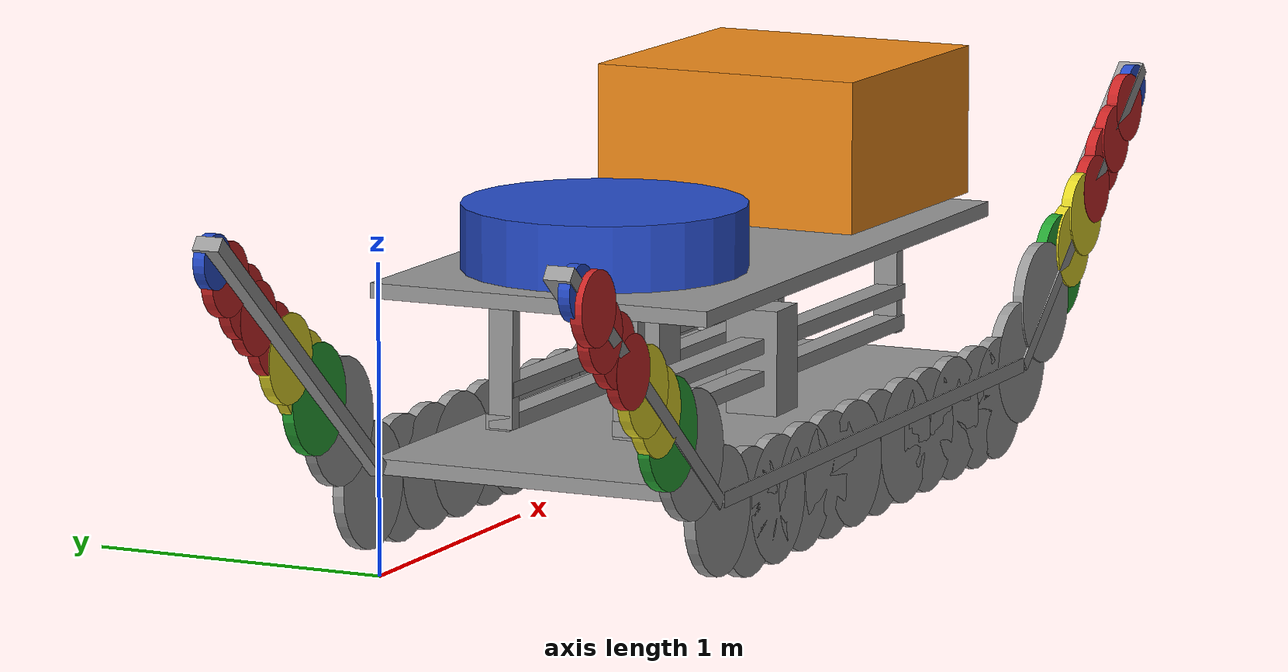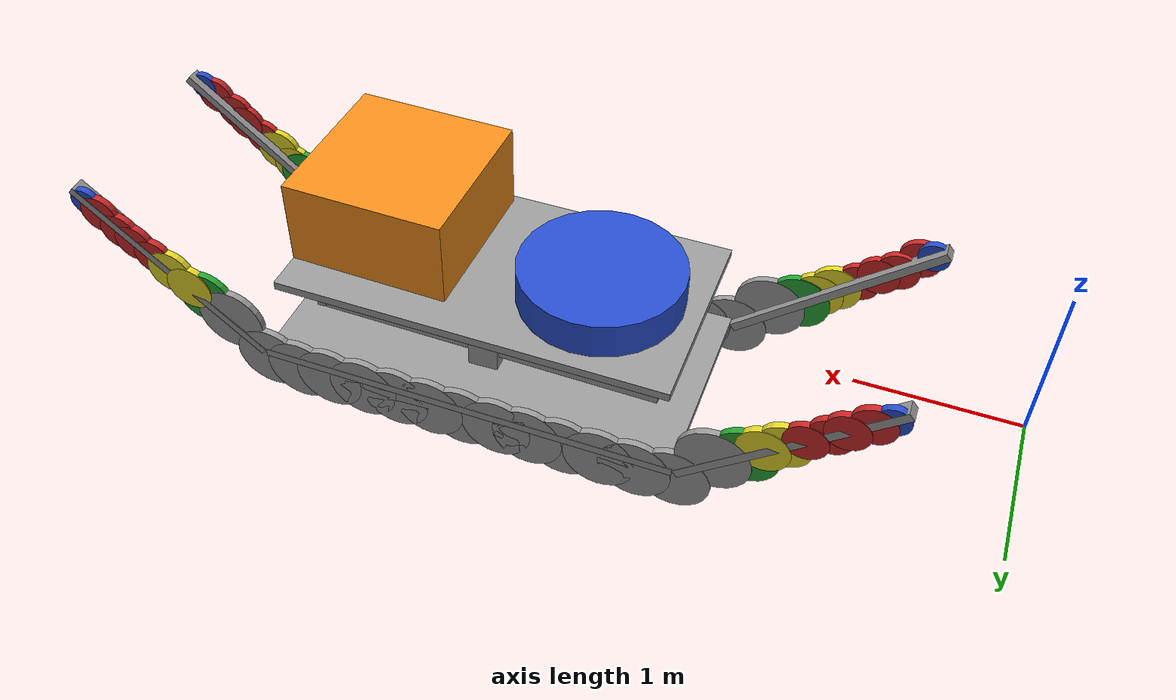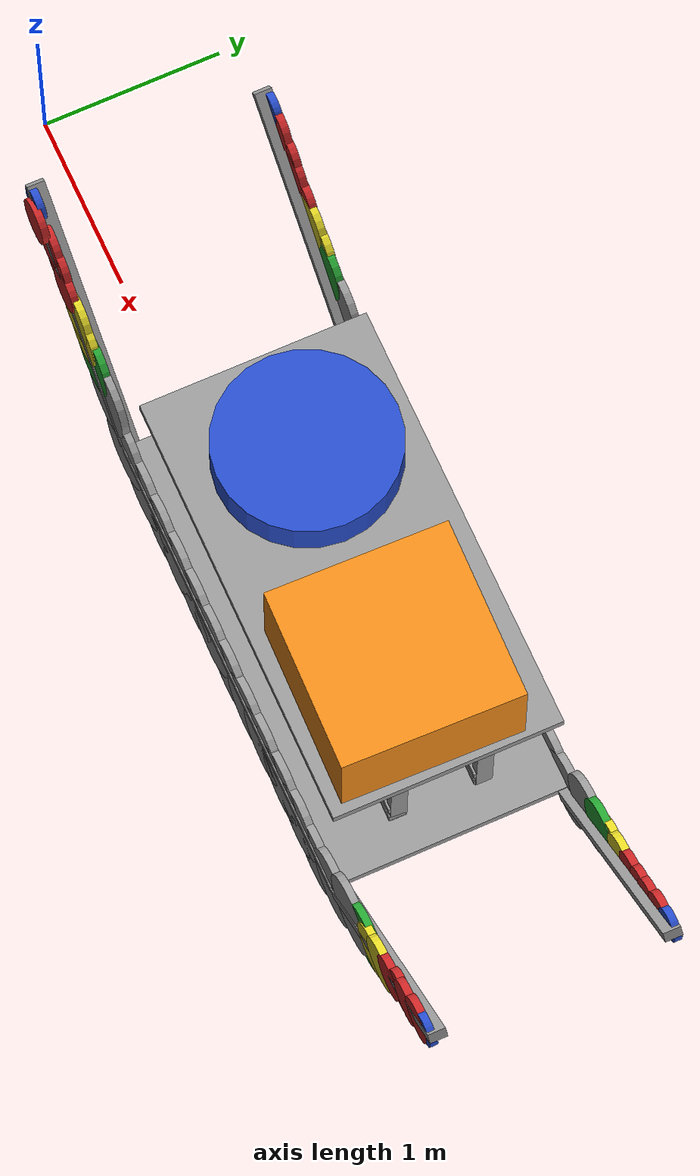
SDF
<?xml version='1.0'?>
<sdf version='1.7'>
  <model name='Mo1G2L'>
    <link name='link_0'>
      <inertial>
        <mass>0.19312</mass>
        <inertia>
          <ixx>0.0301905</ixx>
          <ixy>0</ixy>
          <ixz>0</ixz>
          <iyy>0.111634</iyy>
          <iyz>0</iyz>
          <izz>0.141732</izz>
        </inertia>
        <pose>0 0 0 0 -0 0</pose>
      </inertial>
      <pose>3.14435 0.32869 -0.076023 0 -0 0</pose>
      <self_collide>0</self_collide>
      <enable_wind>0</enable_wind>
      <kinematic>0</kinematic>
      <visual name='visual'>
        <pose>0 0 0 0 -0 0</pose>
        <geometry>
          <box>
            <size>2.63321 1.36861 0.053545</size>
          </box>
        </geometry>
        <material>
          <lighting>1</lighting>
          <script>
            <uri>file://media/materials/scripts/gazebo.material</uri>
            <name>Gazebo/Grey</name>
          </script>
          <shader type='pixel'/>
          <emissive>0 0 0 1</emissive>
        </material>
        <transparency>0</transparency>
        <cast_shadows>1</cast_shadows>
      </visual>
      <collision name='collision'>
        <laser_retro>0</laser_retro>
        <max_contacts>10</max_contacts>
        <pose>0 0 0 0 -0 0</pose>
        <geometry>
          <box>
            <size>2.63321 1.36861 0.053545</size>
          </box>
        </geometry>
        <surface>
          <friction>
            <ode>
              <mu>1</mu>
              <mu2>1</mu2>
              <fdir1>0 0 0</fdir1>
              <slip1>0</slip1>
              <slip2>0</slip2>
            </ode>
            <torsional>
              <coefficient>1</coefficient>
              <patch_radius>0</patch_radius>
              <surface_radius>0</surface_radius>
              <use_patch_radius>1</use_patch_radius>
              <ode>
                <slip>0</slip>
              </ode>
            </torsional>
          </friction>
          <bounce>
            <restitution_coefficient>0</restitution_coefficient>
            <threshold>1e+06</threshold>
          </bounce>
          <contact>
            <collide_without_contact>0</collide_without_contact>
            <collide_without_contact_bitmask>1</collide_without_contact_bitmask>
            <collide_bitmask>1</collide_bitmask>
            <ode>
              <soft_cfm>0</soft_cfm>
              <soft_erp>0.2</soft_erp>
              <kp>1e+13</kp>
              <kd>1</kd>
              <max_vel>0.01</max_vel>
              <min_depth>0</min_depth>
            </ode>
            <bullet>
              <split_impulse>1</split_impulse>
              <split_impulse_penetration_threshold>-0.01</split_impulse_penetration_threshold>
              <soft_cfm>0</soft_cfm>
              <soft_erp>0.2</soft_erp>
              <kp>1e+13</kp>
              <kd>1</kd>
            </bullet>
          </contact>
        </surface>
      </collision>
    </link>
    <link name='link_0_0'>
      <inertial>
        <mass>0.0151839</mass>
        <inertia>
          <ixx>0.000267673</ixx>
          <ixy>0</ixy>
          <ixz>0</ixz>
          <iyy>0.000265516</iyy>
          <iyz>0</iyz>
          <izz>9.20275e-05</izz>
        </inertia>
        <pose>0 0 0 0 -0 0</pose>
      </inertial>
      <pose>3.14553 0.56063 0.117444 -2e-06 -2e-06 0.031243</pose>
      <self_collide>0</self_collide>
      <enable_wind>0</enable_wind>
      <kinematic>0</kinematic>
      <visual name='visual'>
        <pose>0 0 0 0 -0 0</pose>
        <geometry>
          <box>
            <size>0.188449 0.192918 0.417526</size>
          </box>
        </geometry>
        <material>
          <lighting>1</lighting>
          <script>
            <uri>file://media/materials/scripts/gazebo.material</uri>
            <name>Gazebo/Grey</name>
          </script>
          <shader type='pixel'/>
          <emissive>0 0 0 1</emissive>
        </material>
        <transparency>0</transparency>
        <cast_shadows>1</cast_shadows>
      </visual>
      <collision name='collision'>
        <laser_retro>0</laser_retro>
        <max_contacts>10</max_contacts>
        <pose>0 0 0 0 -0 0</pose>
        <geometry>
          <box>
            <size>0.188449 0.192918 0.417526</size>
          </box>
        </geometry>
        <surface>
          <friction>
            <ode>
              <mu>1</mu>
              <mu2>1</mu2>
              <fdir1>0 0 0</fdir1>
              <slip1>0</slip1>
              <slip2>0</slip2>
            </ode>
            <torsional>
              <coefficient>1</coefficient>
              <patch_radius>0</patch_radius>
              <surface_radius>0</surface_radius>
              <use_patch_radius>1</use_patch_radius>
              <ode>
                <slip>0</slip>
              </ode>
            </torsional>
          </friction>
          <bounce>
            <restitution_coefficient>0</restitution_coefficient>
            <threshold>1e+06</threshold>
          </bounce>
          <contact>
            <collide_without_contact>0</collide_without_contact>
            <collide_without_contact_bitmask>1</collide_without_contact_bitmask>
            <collide_bitmask>1</collide_bitmask>
            <ode>
              <soft_cfm>0</soft_cfm>
              <soft_erp>0.2</soft_erp>
              <kp>1e+13</kp>
              <kd>1</kd>
              <max_vel>0.01</max_vel>
              <min_depth>0</min_depth>
            </ode>
            <bullet>
              <split_impulse>1</split_impulse>
              <split_impulse_penetration_threshold>-0.01</split_impulse_penetration_threshold>
              <soft_cfm>0</soft_cfm>
              <soft_erp>0.2</soft_erp>
              <kp>1e+13</kp>
              <kd>1</kd>
            </bullet>
          </contact>
        </surface>
      </collision>
    </link>
    <link name='link_0_0_clone_0'>
      <inertial>
        <mass>0.0151839</mass>
        <inertia>
          <ixx>0.000267673</ixx>
          <ixy>0</ixy>
          <ixz>0</ixz>
          <iyy>0.000265516</iyy>
          <iyz>0</iyz>
          <izz>9.20275e-05</izz>
        </inertia>
        <pose>0 0 0 0 -0 0</pose>
      </inertial>
      <pose>3.16601 0.113622 0.117452 -4e-06 -4e-06 0.028329</pose>
      <self_collide>0</self_collide>
      <enable_wind>0</enable_wind>
      <kinematic>0</kinematic>
      <visual name='visual_0'>
        <pose>0 0 0 0 -0 0</pose>
        <geometry>
          <box>
            <size>0.188449 0.192918 0.417526</size>
          </box>
        </geometry>
        <material>
          <lighting>1</lighting>
          <script>
            <uri>file://media/materials/scripts/gazebo.material</uri>
            <name>Gazebo/Grey</name>
          </script>
          <shader type='pixel'/>
          <emissive>0 0 0 1</emissive>
        </material>
        <transparency>0</transparency>
        <cast_shadows>1</cast_shadows>
      </visual>
      <collision name='collision'>
        <laser_retro>0</laser_retro>
        <max_contacts>10</max_contacts>
        <pose>0 0 0 0 -0 0</pose>
        <geometry>
          <box>
            <size>0.188449 0.192918 0.417526</size>
          </box>
        </geometry>
        <surface>
          <friction>
            <ode>
              <mu>1</mu>
              <mu2>1</mu2>
              <fdir1>0 0 0</fdir1>
              <slip1>0</slip1>
              <slip2>0</slip2>
            </ode>
            <torsional>
              <coefficient>1</coefficient>
              <patch_radius>0</patch_radius>
              <surface_radius>0</surface_radius>
              <use_patch_radius>1</use_patch_radius>
              <ode>
                <slip>0</slip>
              </ode>
            </torsional>
          </friction>
          <bounce>
            <restitution_coefficient>0</restitution_coefficient>
            <threshold>1e+06</threshold>
          </bounce>
          <contact>
            <collide_without_contact>0</collide_without_contact>
            <collide_without_contact_bitmask>1</collide_without_contact_bitmask>
            <collide_bitmask>1</collide_bitmask>
            <ode>
              <soft_cfm>0</soft_cfm>
              <soft_erp>0.2</soft_erp>
              <kp>1e+13</kp>
              <kd>1</kd>
              <max_vel>0.01</max_vel>
              <min_depth>0</min_depth>
            </ode>
            <bullet>
              <split_impulse>1</split_impulse>
              <split_impulse_penetration_threshold>-0.01</split_impulse_penetration_threshold>
              <soft_cfm>0</soft_cfm>
              <soft_erp>0.2</soft_erp>
              <kp>1e+13</kp>
              <kd>1</kd>
            </bullet>
          </contact>
        </surface>
      </collision>
    </link>
    <link name='link_0_1'>
      <inertial>
        <mass>0.54127</mass>
        <inertia>
          <ixx>0.0583206</ixx>
          <ixy>0</ixy>
          <ixz>0</ixz>
          <iyy>0.0583206</iyy>
          <iyz>0</iyz>
          <izz>0.0902117</izz>
        </inertia>
        <pose>0 0 0 0 -0 0</pose>
      </inertial>
      <pose>3.78289 0.304157 0.854491 -0 -0 -0.023819</pose>
      <gravity>1</gravity>
      <self_collide>0</self_collide>
      <kinematic>0</kinematic>
      <enable_wind>0</enable_wind>
      <visual name='visual'>
        <pose>0 0 0 0 -0 0</pose>
        <geometry>
          <box>
            <size>1 1 0.54127</size>
          </box>
        </geometry>
        <material>
          <lighting>1</lighting>
          <script>
            <uri>file://media/materials/scripts/gazebo.material</uri>
            <name>Gazebo/Orange</name>
          </script>
          <shader type='pixel'>
            <normal_map>__default__</normal_map>
          </shader>
          <ambient>1 0.509 0.047 1</ambient>
          <diffuse>1 0.509 0.047 1</diffuse>
          <specular>0.5 0.5 0.5 1</specular>
          <emissive>0 0 0 1</emissive>
        </material>
        <transparency>0</transparency>
        <cast_shadows>1</cast_shadows>
      </visual>
      <collision name='collision'>
        <laser_retro>0</laser_retro>
        <max_contacts>10</max_contacts>
        <pose>0 0 0 0 -0 0</pose>
        <geometry>
          <box>
            <size>1 1 0.54127</size>
          </box>
        </geometry>
        <surface>
          <friction>
            <ode>
              <mu>1</mu>
              <mu2>1</mu2>
              <fdir1>0 0 0</fdir1>
              <slip1>0</slip1>
              <slip2>0</slip2>
            </ode>
            <torsional>
              <coefficient>1</coefficient>
              <patch_radius>0</patch_radius>
              <surface_radius>0</surface_radius>
              <use_patch_radius>1</use_patch_radius>
              <ode>
                <slip>0</slip>
              </ode>
            </torsional>
          </friction>
          <bounce>
            <restitution_coefficient>0</restitution_coefficient>
            <threshold>1e+06</threshold>
          </bounce>
          <contact>
            <collide_without_contact>0</collide_without_contact>
            <collide_without_contact_bitmask>1</collide_without_contact_bitmask>
            <collide_bitmask>1</collide_bitmask>
            <ode>
              <soft_cfm>0</soft_cfm>
              <soft_erp>0.2</soft_erp>
              <kp>1e+13</kp>
              <kd>1</kd>
              <max_vel>0.01</max_vel>
              <min_depth>0</min_depth>
            </ode>
            <bullet>
              <split_impulse>1</split_impulse>
              <split_impulse_penetration_threshold>-0.01</split_impulse_penetration_threshold>
              <soft_cfm>0</soft_cfm>
              <soft_erp>0.2</soft_erp>
              <kp>1e+13</kp>
              <kd>1</kd>
            </bullet>
          </contact>
        </surface>
      </collision>
    </link>
    <link name='link_0_clone'>
      <inertial>
        <mass>0.165494</mass>
        <inertia>
          <ixx>0.0222125</ixx>
          <ixy>0</ixy>
          <ixz>0</ixz>
          <iyy>0.0818522</iyy>
          <iyz>0</iyz>
          <izz>0.103986</izz>
        </inertia>
        <pose>0 0 0 0 -0 0</pose>
      </inertial>
      <pose>3.09825 0.365907 0.522794 -2e-06 -2e-06 -0.002914</pose>
      <self_collide>0</self_collide>
      <enable_wind>0</enable_wind>
      <kinematic>0</kinematic>
      <visual name='visual'>
        <pose>0 0 0 0 -0 0</pose>
        <geometry>
          <box>
            <size>2.43562 1.26798 0.053545</size>
          </box>
        </geometry>
        <material>
          <lighting>1</lighting>
          <script>
            <uri>file://media/materials/scripts/gazebo.material</uri>
            <name>Gazebo/Grey</name>
          </script>
          <shader type='pixel'/>
          <emissive>0 0 0 1</emissive>
        </material>
        <transparency>0</transparency>
        <cast_shadows>1</cast_shadows>
      </visual>
      <collision name='collision'>
        <laser_retro>0</laser_retro>
        <max_contacts>10</max_contacts>
        <pose>0 0 0 0 -0 0</pose>
        <geometry>
          <box>
            <size>2.43562 1.26798 0.053545</size>
          </box>
        </geometry>
        <surface>
          <friction>
            <ode>
              <mu>1</mu>
              <mu2>1</mu2>
              <fdir1>0 0 0</fdir1>
              <slip1>0</slip1>
              <slip2>0</slip2>
            </ode>
            <torsional>
              <coefficient>1</coefficient>
              <patch_radius>0</patch_radius>
              <surface_radius>0</surface_radius>
              <use_patch_radius>1</use_patch_radius>
              <ode>
                <slip>0</slip>
              </ode>
            </torsional>
          </friction>
          <bounce>
            <restitution_coefficient>0</restitution_coefficient>
            <threshold>1e+06</threshold>
          </bounce>
          <contact>
            <collide_without_contact>0</collide_without_contact>
            <collide_without_contact_bitmask>1</collide_without_contact_bitmask>
            <collide_bitmask>1</collide_bitmask>
            <ode>
              <soft_cfm>0</soft_cfm>
              <soft_erp>0.2</soft_erp>
              <kp>1e+13</kp>
              <kd>1</kd>
              <max_vel>0.01</max_vel>
              <min_depth>0</min_depth>
            </ode>
            <bullet>
              <split_impulse>1</split_impulse>
              <split_impulse_penetration_threshold>-0.01</split_impulse_penetration_threshold>
              <soft_cfm>0</soft_cfm>
              <soft_erp>0.2</soft_erp>
              <kp>1e+13</kp>
              <kd>1</kd>
            </bullet>
          </contact>
        </surface>
      </collision>
    </link>
    <link name='link_0_clone_clone_1_clone'>
      <inertial>
        <mass>0.00779275</mass>
        <inertia>
          <ixx>7.93964e-06</ixx>
          <ixy>0</ixy>
          <ixz>0</ixz>
          <iyy>0.00146981</iyy>
          <iyz>0</iyz>
          <izz>0.00147403</izz>
        </inertia>
        <pose>0 0 0 0 -0 0</pose>
      </inertial>
      <pose>5.062 -0.307248 0.391113 0 -0.680705 0</pose>
      <self_collide>0</self_collide>
      <enable_wind>0</enable_wind>
      <kinematic>0</kinematic>
      <visual name='visual'>
        <pose>0 0 0 0 -0 0</pose>
        <geometry>
          <box>
            <size>1.50349 0.096743 0.053545</size>
          </box>
        </geometry>
        <material>
          <lighting>1</lighting>
          <script>
            <uri>file://media/materials/scripts/gazebo.material</uri>
            <name>Gazebo/Grey</name>
          </script>
          <shader type='pixel'/>
          <emissive>0 0 0 1</emissive>
        </material>
        <transparency>0</transparency>
        <cast_shadows>1</cast_shadows>
      </visual>
      <collision name='collision'>
        <laser_retro>0</laser_retro>
        <max_contacts>10</max_contacts>
        <pose>0 0 0 0 -0 0</pose>
        <geometry>
          <box>
            <size>1.50349 0.096743 0.053545</size>
          </box>
        </geometry>
        <surface>
          <friction>
            <ode>
              <mu>1</mu>
              <mu2>1</mu2>
              <fdir1>0 0 0</fdir1>
              <slip1>0</slip1>
              <slip2>0</slip2>
            </ode>
            <torsional>
              <coefficient>1</coefficient>
              <patch_radius>0</patch_radius>
              <surface_radius>0</surface_radius>
              <use_patch_radius>1</use_patch_radius>
              <ode>
                <slip>0</slip>
              </ode>
            </torsional>
          </friction>
          <bounce>
            <restitution_coefficient>0</restitution_coefficient>
            <threshold>1e+06</threshold>
          </bounce>
          <contact>
            <collide_without_contact>0</collide_without_contact>
            <collide_without_contact_bitmask>1</collide_without_contact_bitmask>
            <collide_bitmask>1</collide_bitmask>
            <ode>
              <soft_cfm>0</soft_cfm>
              <soft_erp>0.2</soft_erp>
              <kp>1e+13</kp>
              <kd>1</kd>
              <max_vel>0.01</max_vel>
              <min_depth>0</min_depth>
            </ode>
            <bullet>
              <split_impulse>1</split_impulse>
              <split_impulse_penetration_threshold>-0.01</split_impulse_penetration_threshold>
              <soft_cfm>0</soft_cfm>
              <soft_erp>0.2</soft_erp>
              <kp>1e+13</kp>
              <kd>1</kd>
            </bullet>
          </contact>
        </surface>
      </collision>
    </link>
    <link name='link_0_clone_clone_1_clone_clone'>
      <inertial>
        <mass>0.00779275</mass>
        <inertia>
          <ixx>7.93964e-06</ixx>
          <ixy>0</ixy>
          <ixz>0</ixz>
          <iyy>0.00146981</iyy>
          <iyz>0</iyz>
          <izz>0.00147403</izz>
        </inertia>
        <pose>0 0 0 0 -0 0</pose>
      </inertial>
      <pose>5.062 0.964628 0.391113 0 -0.680705 0</pose>
      <self_collide>0</self_collide>
      <enable_wind>0</enable_wind>
      <kinematic>0</kinematic>
      <visual name='visual'>
        <pose>0 0 0 0 -0 0</pose>
        <geometry>
          <box>
            <size>1.50349 0.096743 0.053545</size>
          </box>
        </geometry>
        <material>
          <lighting>1</lighting>
          <script>
            <uri>file://media/materials/scripts/gazebo.material</uri>
            <name>Gazebo/Grey</name>
          </script>
          <shader type='pixel'/>
          <emissive>0 0 0 1</emissive>
        </material>
        <transparency>0</transparency>
        <cast_shadows>1</cast_shadows>
      </visual>
      <collision name='collision'>
        <laser_retro>0</laser_retro>
        <max_contacts>10</max_contacts>
        <pose>0 0 0 0 -0 0</pose>
        <geometry>
          <box>
            <size>1.50349 0.096743 0.053545</size>
          </box>
        </geometry>
        <surface>
          <friction>
            <ode>
              <mu>1</mu>
              <mu2>1</mu2>
              <fdir1>0 0 0</fdir1>
              <slip1>0</slip1>
              <slip2>0</slip2>
            </ode>
            <torsional>
              <coefficient>1</coefficient>
              <patch_radius>0</patch_radius>
              <surface_radius>0</surface_radius>
              <use_patch_radius>1</use_patch_radius>
              <ode>
                <slip>0</slip>
              </ode>
            </torsional>
          </friction>
          <bounce>
            <restitution_coefficient>0</restitution_coefficient>
            <threshold>1e+06</threshold>
          </bounce>
          <contact>
            <collide_without_contact>0</collide_without_contact>
            <collide_without_contact_bitmask>1</collide_without_contact_bitmask>
            <collide_bitmask>1</collide_bitmask>
            <ode>
              <soft_cfm>0</soft_cfm>
              <soft_erp>0.2</soft_erp>
              <kp>1e+13</kp>
              <kd>1</kd>
              <max_vel>0.01</max_vel>
              <min_depth>0</min_depth>
            </ode>
            <bullet>
              <split_impulse>1</split_impulse>
              <split_impulse_penetration_threshold>-0.01</split_impulse_penetration_threshold>
              <soft_cfm>0</soft_cfm>
              <soft_erp>0.2</soft_erp>
              <kp>1e+13</kp>
              <kd>1</kd>
            </bullet>
          </contact>
        </surface>
      </collision>
    </link>
    <link name='link_0_clone_clone_1_clone_clone_clone'>
      <inertial>
        <mass>0.00779275</mass>
        <inertia>
          <ixx>7.93964e-06</ixx>
          <ixy>0</ixy>
          <ixz>0</ixz>
          <iyy>0.00146981</iyy>
          <iyz>0</iyz>
          <izz>0.00147403</izz>
        </inertia>
        <pose>0 0 0 0 -0 0</pose>
      </inertial>
      <pose>1.23399 -0.307246 0.400114 3.14159 -0.69668 3.14159</pose>
      <self_collide>0</self_collide>
      <enable_wind>0</enable_wind>
      <kinematic>0</kinematic>
      <visual name='visual'>
        <pose>0 0 0 0 -0 0</pose>
        <geometry>
          <box>
            <size>1.50349 0.096743 0.053545</size>
          </box>
        </geometry>
        <material>
          <lighting>1</lighting>
          <script>
            <uri>file://media/materials/scripts/gazebo.material</uri>
            <name>Gazebo/Grey</name>
          </script>
          <shader type='pixel'/>
          <emissive>0 0 0 1</emissive>
        </material>
        <transparency>0</transparency>
        <cast_shadows>1</cast_shadows>
      </visual>
      <collision name='collision'>
        <laser_retro>0</laser_retro>
        <max_contacts>10</max_contacts>
        <pose>0 0 0 0 -0 0</pose>
        <geometry>
          <box>
            <size>1.50349 0.096743 0.053545</size>
          </box>
        </geometry>
        <surface>
          <friction>
            <ode>
              <mu>1</mu>
              <mu2>1</mu2>
              <fdir1>0 0 0</fdir1>
              <slip1>0</slip1>
              <slip2>0</slip2>
            </ode>
            <torsional>
              <coefficient>1</coefficient>
              <patch_radius>0</patch_radius>
              <surface_radius>0</surface_radius>
              <use_patch_radius>1</use_patch_radius>
              <ode>
                <slip>0</slip>
              </ode>
            </torsional>
          </friction>
          <bounce>
            <restitution_coefficient>0</restitution_coefficient>
            <threshold>1e+06</threshold>
          </bounce>
          <contact>
            <collide_without_contact>0</collide_without_contact>
            <collide_without_contact_bitmask>1</collide_without_contact_bitmask>
            <collide_bitmask>1</collide_bitmask>
            <ode>
              <soft_cfm>0</soft_cfm>
              <soft_erp>0.2</soft_erp>
              <kp>1e+13</kp>
              <kd>1</kd>
              <max_vel>0.01</max_vel>
              <min_depth>0</min_depth>
            </ode>
            <bullet>
              <split_impulse>1</split_impulse>
              <split_impulse_penetration_threshold>-0.01</split_impulse_penetration_threshold>
              <soft_cfm>0</soft_cfm>
              <soft_erp>0.2</soft_erp>
              <kp>1e+13</kp>
              <kd>1</kd>
            </bullet>
          </contact>
        </surface>
      </collision>
    </link>
    <link name='link_0_clone_clone_1_clone_clone_clone_clone'>
      <inertial>
        <mass>0.00779275</mass>
        <inertia>
          <ixx>7.93964e-06</ixx>
          <ixy>0</ixy>
          <ixz>0</ixz>
          <iyy>0.00146981</iyy>
          <iyz>0</iyz>
          <izz>0.00147403</izz>
        </inertia>
        <pose>0 0 0 0 -0 0</pose>
      </inertial>
      <pose>1.23399 0.964627 0.400114 3.14159 -0.69668 3.14159</pose>
      <self_collide>0</self_collide>
      <enable_wind>0</enable_wind>
      <kinematic>0</kinematic>
      <visual name='visual'>
        <pose>0 0 0 0 -0 0</pose>
        <geometry>
          <box>
            <size>1.50349 0.096743 0.053545</size>
          </box>
        </geometry>
        <material>
          <lighting>1</lighting>
          <script>
            <uri>file://media/materials/scripts/gazebo.material</uri>
            <name>Gazebo/Grey</name>
          </script>
          <shader type='pixel'/>
          <emissive>0 0 0 1</emissive>
        </material>
        <transparency>0</transparency>
        <cast_shadows>1</cast_shadows>
      </visual>
      <collision name='collision'>
        <laser_retro>0</laser_retro>
        <max_contacts>10</max_contacts>
        <pose>0 0 0 0 -0 0</pose>
        <geometry>
          <box>
            <size>1.50349 0.096743 0.053545</size>
          </box>
        </geometry>
        <surface>
          <friction>
            <ode>
              <mu>1</mu>
              <mu2>1</mu2>
              <fdir1>0 0 0</fdir1>
              <slip1>0</slip1>
              <slip2>0</slip2>
            </ode>
            <torsional>
              <coefficient>1</coefficient>
              <patch_radius>0</patch_radius>
              <surface_radius>0</surface_radius>
              <use_patch_radius>1</use_patch_radius>
              <ode>
                <slip>0</slip>
              </ode>
            </torsional>
          </friction>
          <bounce>
            <restitution_coefficient>0</restitution_coefficient>
            <threshold>1e+06</threshold>
          </bounce>
          <contact>
            <collide_without_contact>0</collide_without_contact>
            <collide_without_contact_bitmask>1</collide_without_contact_bitmask>
            <collide_bitmask>1</collide_bitmask>
            <ode>
              <soft_cfm>0</soft_cfm>
              <soft_erp>0.2</soft_erp>
              <kp>1e+13</kp>
              <kd>1</kd>
              <max_vel>0.01</max_vel>
              <min_depth>0</min_depth>
            </ode>
            <bullet>
              <split_impulse>1</split_impulse>
              <split_impulse_penetration_threshold>-0.01</split_impulse_penetration_threshold>
              <soft_cfm>0</soft_cfm>
              <soft_erp>0.2</soft_erp>
              <kp>1e+13</kp>
              <kd>1</kd>
            </bullet>
          </contact>
        </surface>
      </collision>
    </link>
    <link name='link_0_clone_clone_clone'>
      <inertial>
        <mass>0.0109918</mass>
        <inertia>
          <ixx>1.02493e-05</ixx>
          <ixy>0</ixy>
          <ixz>0</ixz>
          <iyy>0.00463363</iyy>
          <iyz>0</iyz>
          <izz>0.00463863</izz>
        </inertia>
        <pose>0 0 0 0 -0 0</pose>
      </inertial>
      <pose>3.16613 0.573909 0.185264 -6e-06 -6e-06 -0.008742</pose>
      <self_collide>0</self_collide>
      <enable_wind>0</enable_wind>
      <kinematic>0</kinematic>
      <visual name='visual'>
        <pose>0 0 0 0 -0 0</pose>
        <geometry>
          <box>
            <size>2.2485 0.091227 0.053545</size>
          </box>
        </geometry>
        <material>
          <lighting>1</lighting>
          <script>
            <uri>file://media/materials/scripts/gazebo.material</uri>
            <name>Gazebo/Grey</name>
          </script>
          <shader type='pixel'/>
          <emissive>0 0 0 1</emissive>
        </material>
        <transparency>0</transparency>
        <cast_shadows>1</cast_shadows>
      </visual>
      <collision name='collision'>
        <laser_retro>0</laser_retro>
        <max_contacts>10</max_contacts>
        <pose>0 0 0 0 -0 0</pose>
        <geometry>
          <box>
            <size>2.2485 0.091227 0.053545</size>
          </box>
        </geometry>
        <surface>
          <friction>
            <ode>
              <mu>1</mu>
              <mu2>1</mu2>
              <fdir1>0 0 0</fdir1>
              <slip1>0</slip1>
              <slip2>0</slip2>
            </ode>
            <torsional>
              <coefficient>1</coefficient>
              <patch_radius>0</patch_radius>
              <surface_radius>0</surface_radius>
              <use_patch_radius>1</use_patch_radius>
              <ode>
                <slip>0</slip>
              </ode>
            </torsional>
          </friction>
          <bounce>
            <restitution_coefficient>0</restitution_coefficient>
            <threshold>1e+06</threshold>
          </bounce>
          <contact>
            <collide_without_contact>0</collide_without_contact>
            <collide_without_contact_bitmask>1</collide_without_contact_bitmask>
            <collide_bitmask>1</collide_bitmask>
            <ode>
              <soft_cfm>0</soft_cfm>
              <soft_erp>0.2</soft_erp>
              <kp>1e+13</kp>
              <kd>1</kd>
              <max_vel>0.01</max_vel>
              <min_depth>0</min_depth>
            </ode>
            <bullet>
              <split_impulse>1</split_impulse>
              <split_impulse_penetration_threshold>-0.01</split_impulse_penetration_threshold>
              <soft_cfm>0</soft_cfm>
              <soft_erp>0.2</soft_erp>
              <kp>1e+13</kp>
              <kd>1</kd>
            </bullet>
          </contact>
        </surface>
      </collision>
    </link>
    <link name='link_0_clone_clone_clone_clone'>
      <inertial>
        <mass>0.0109918</mass>
        <inertia>
          <ixx>1.02493e-05</ixx>
          <ixy>0</ixy>
          <ixz>0</ixz>
          <iyy>0.00463363</iyy>
          <iyz>0</iyz>
          <izz>0.00463863</izz>
        </inertia>
        <pose>0 0 0 0 -0 0</pose>
      </inertial>
      <pose>3.15984 0.582526 0.068745 -8e-06 -8e-06 -0.011656</pose>
      <self_collide>0</self_collide>
      <enable_wind>0</enable_wind>
      <kinematic>0</kinematic>
      <visual name='visual'>
        <pose>0 0 0 0 -0 0</pose>
        <geometry>
          <box>
            <size>2.2485 0.091227 0.053545</size>
          </box>
        </geometry>
        <material>
          <lighting>1</lighting>
          <script>
            <uri>file://media/materials/scripts/gazebo.material</uri>
            <name>Gazebo/Grey</name>
          </script>
          <shader type='pixel'/>
          <emissive>0 0 0 1</emissive>
        </material>
        <transparency>0</transparency>
        <cast_shadows>1</cast_shadows>
      </visual>
      <collision name='collision'>
        <laser_retro>0</laser_retro>
        <max_contacts>10</max_contacts>
        <pose>0 0 0 0 -0 0</pose>
        <geometry>
          <box>
            <size>2.2485 0.091227 0.053545</size>
          </box>
        </geometry>
        <surface>
          <friction>
            <ode>
              <mu>1</mu>
              <mu2>1</mu2>
              <fdir1>0 0 0</fdir1>
              <slip1>0</slip1>
              <slip2>0</slip2>
            </ode>
            <torsional>
              <coefficient>1</coefficient>
              <patch_radius>0</patch_radius>
              <surface_radius>0</surface_radius>
              <use_patch_radius>1</use_patch_radius>
              <ode>
                <slip>0</slip>
              </ode>
            </torsional>
          </friction>
          <bounce>
            <restitution_coefficient>0</restitution_coefficient>
            <threshold>1e+06</threshold>
          </bounce>
          <contact>
            <collide_without_contact>0</collide_without_contact>
            <collide_without_contact_bitmask>1</collide_without_contact_bitmask>
            <collide_bitmask>1</collide_bitmask>
            <ode>
              <soft_cfm>0</soft_cfm>
              <soft_erp>0.2</soft_erp>
              <kp>1e+13</kp>
              <kd>1</kd>
              <max_vel>0.01</max_vel>
              <min_depth>0</min_depth>
            </ode>
            <bullet>
              <split_impulse>1</split_impulse>
              <split_impulse_penetration_threshold>-0.01</split_impulse_penetration_threshold>
              <soft_cfm>0</soft_cfm>
              <soft_erp>0.2</soft_erp>
              <kp>1e+13</kp>
              <kd>1</kd>
            </bullet>
          </contact>
        </surface>
      </collision>
    </link>
    <link name='link_0_clone_clone_clone_clone_0'>
      <inertial>
        <mass>0.0109918</mass>
        <inertia>
          <ixx>1.02493e-05</ixx>
          <ixy>0</ixy>
          <ixz>0</ixz>
          <iyy>0.00463363</iyy>
          <iyz>0</iyz>
          <izz>0.00463863</izz>
        </inertia>
        <pose>0 0 0 0 -0 0</pose>
      </inertial>
      <pose>3.16584 0.106751 0.084032 -8e-06 -8e-06 -0.011656</pose>
      <self_collide>0</self_collide>
      <enable_wind>0</enable_wind>
      <kinematic>0</kinematic>
      <visual name='visual'>
        <pose>0 0 0 0 -0 0</pose>
        <geometry>
          <box>
            <size>2.2485 0.091227 0.053545</size>
          </box>
        </geometry>
        <material>
          <lighting>1</lighting>
          <script>
            <uri>file://media/materials/scripts/gazebo.material</uri>
            <name>Gazebo/Grey</name>
          </script>
          <shader type='pixel'/>
          <emissive>0 0 0 1</emissive>
        </material>
        <transparency>0</transparency>
        <cast_shadows>1</cast_shadows>
      </visual>
      <collision name='collision'>
        <laser_retro>0</laser_retro>
        <max_contacts>10</max_contacts>
        <pose>0 0 0 0 -0 0</pose>
        <geometry>
          <box>
            <size>2.2485 0.091227 0.053545</size>
          </box>
        </geometry>
        <surface>
          <friction>
            <ode>
              <mu>1</mu>
              <mu2>1</mu2>
              <fdir1>0 0 0</fdir1>
              <slip1>0</slip1>
              <slip2>0</slip2>
            </ode>
            <torsional>
              <coefficient>1</coefficient>
              <patch_radius>0</patch_radius>
              <surface_radius>0</surface_radius>
              <use_patch_radius>1</use_patch_radius>
              <ode>
                <slip>0</slip>
              </ode>
            </torsional>
          </friction>
          <bounce>
            <restitution_coefficient>0</restitution_coefficient>
            <threshold>1e+06</threshold>
          </bounce>
          <contact>
            <collide_without_contact>0</collide_without_contact>
            <collide_without_contact_bitmask>1</collide_without_contact_bitmask>
            <collide_bitmask>1</collide_bitmask>
            <ode>
              <soft_cfm>0</soft_cfm>
              <soft_erp>0.2</soft_erp>
              <kp>1e+13</kp>
              <kd>1</kd>
              <max_vel>0.01</max_vel>
              <min_depth>0</min_depth>
            </ode>
            <bullet>
              <split_impulse>1</split_impulse>
              <split_impulse_penetration_threshold>-0.01</split_impulse_penetration_threshold>
              <soft_cfm>0</soft_cfm>
              <soft_erp>0.2</soft_erp>
              <kp>1e+13</kp>
              <kd>1</kd>
            </bullet>
          </contact>
        </surface>
      </collision>
    </link>
    <link name='link_0_clone_clone_clone_clone_0_clone'>
      <inertial>
        <mass>0.0109918</mass>
        <inertia>
          <ixx>1.02493e-05</ixx>
          <ixy>0</ixy>
          <ixz>0</ixz>
          <iyy>0.00463363</iyy>
          <iyz>0</iyz>
          <izz>0.00463863</izz>
        </inertia>
        <pose>0 0 0 0 -0 0</pose>
      </inertial>
      <pose>3.16561 0.106538 0.199042 -1e-05 -1e-05 -0.01457</pose>
      <self_collide>0</self_collide>
      <enable_wind>0</enable_wind>
      <kinematic>0</kinematic>
      <visual name='visual'>
        <pose>0 0 0 0 -0 0</pose>
        <geometry>
          <box>
            <size>2.2485 0.091227 0.053545</size>
          </box>
        </geometry>
        <material>
          <lighting>1</lighting>
          <script>
            <uri>file://media/materials/scripts/gazebo.material</uri>
            <name>Gazebo/Grey</name>
          </script>
          <shader type='pixel'/>
          <emissive>0 0 0 1</emissive>
        </material>
        <transparency>0</transparency>
        <cast_shadows>1</cast_shadows>
      </visual>
      <collision name='collision'>
        <laser_retro>0</laser_retro>
        <max_contacts>10</max_contacts>
        <pose>0 0 0 0 -0 0</pose>
        <geometry>
          <box>
            <size>2.2485 0.091227 0.053545</size>
          </box>
        </geometry>
        <surface>
          <friction>
            <ode>
              <mu>1</mu>
              <mu2>1</mu2>
              <fdir1>0 0 0</fdir1>
              <slip1>0</slip1>
              <slip2>0</slip2>
            </ode>
            <torsional>
              <coefficient>1</coefficient>
              <patch_radius>0</patch_radius>
              <surface_radius>0</surface_radius>
              <use_patch_radius>1</use_patch_radius>
              <ode>
                <slip>0</slip>
              </ode>
            </torsional>
          </friction>
          <bounce>
            <restitution_coefficient>0</restitution_coefficient>
            <threshold>1e+06</threshold>
          </bounce>
          <contact>
            <collide_without_contact>0</collide_without_contact>
            <collide_without_contact_bitmask>1</collide_without_contact_bitmask>
            <collide_bitmask>1</collide_bitmask>
            <ode>
              <soft_cfm>0</soft_cfm>
              <soft_erp>0.2</soft_erp>
              <kp>1e+13</kp>
              <kd>1</kd>
              <max_vel>0.01</max_vel>
              <min_depth>0</min_depth>
            </ode>
            <bullet>
              <split_impulse>1</split_impulse>
              <split_impulse_penetration_threshold>-0.01</split_impulse_penetration_threshold>
              <soft_cfm>0</soft_cfm>
              <soft_erp>0.2</soft_erp>
              <kp>1e+13</kp>
              <kd>1</kd>
            </bullet>
          </contact>
        </surface>
      </collision>
    </link>
    <link name='link_0_clone_clone_clone_clone_1'>
      <inertial>
        <mass>0.00235857</mass>
        <inertia>
          <ixx>2.19926e-06</ixx>
          <ixy>0</ixy>
          <ixz>0</ixz>
          <iyy>4.63161e-05</iyy>
          <iyz>0</iyz>
          <izz>4.73883e-05</izz>
        </inertia>
        <pose>0 0 0 0 -0 0</pose>
      </inertial>
      <pose>2.0724 0.116461 0.288666 -0.000557 -1.55567 -0.0111</pose>
      <self_collide>0</self_collide>
      <enable_wind>0</enable_wind>
      <kinematic>0</kinematic>
      <visual name='visual'>
        <pose>0 0 0 0 -0 0</pose>
        <geometry>
          <box>
            <size>0.482474 0.091227 0.053545</size>
          </box>
        </geometry>
        <material>
          <lighting>1</lighting>
          <script>
            <uri>file://media/materials/scripts/gazebo.material</uri>
            <name>Gazebo/Grey</name>
          </script>
          <shader type='pixel'/>
          <emissive>0 0 0 1</emissive>
        </material>
        <transparency>0</transparency>
        <cast_shadows>1</cast_shadows>
      </visual>
      <collision name='collision'>
        <laser_retro>0</laser_retro>
        <max_contacts>10</max_contacts>
        <pose>0 0 0 0 -0 0</pose>
        <geometry>
          <box>
            <size>0.482474 0.091227 0.053545</size>
          </box>
        </geometry>
        <surface>
          <friction>
            <ode>
              <mu>1</mu>
              <mu2>1</mu2>
              <fdir1>0 0 0</fdir1>
              <slip1>0</slip1>
              <slip2>0</slip2>
            </ode>
            <torsional>
              <coefficient>1</coefficient>
              <patch_radius>0</patch_radius>
              <surface_radius>0</surface_radius>
              <use_patch_radius>1</use_patch_radius>
              <ode>
                <slip>0</slip>
              </ode>
            </torsional>
          </friction>
          <bounce>
            <restitution_coefficient>0</restitution_coefficient>
            <threshold>1e+06</threshold>
          </bounce>
          <contact>
            <collide_without_contact>0</collide_without_contact>
            <collide_without_contact_bitmask>1</collide_without_contact_bitmask>
            <collide_bitmask>1</collide_bitmask>
            <ode>
              <soft_cfm>0</soft_cfm>
              <soft_erp>0.2</soft_erp>
              <kp>1e+13</kp>
              <kd>1</kd>
              <max_vel>0.01</max_vel>
              <min_depth>0</min_depth>
            </ode>
            <bullet>
              <split_impulse>1</split_impulse>
              <split_impulse_penetration_threshold>-0.01</split_impulse_penetration_threshold>
              <soft_cfm>0</soft_cfm>
              <soft_erp>0.2</soft_erp>
              <kp>1e+13</kp>
              <kd>1</kd>
            </bullet>
          </contact>
        </surface>
      </collision>
    </link>
    <link name='link_0_clone_clone_clone_clone_1_clone'>
      <inertial>
        <mass>0.00235857</mass>
        <inertia>
          <ixx>2.19926e-06</ixx>
          <ixy>0</ixy>
          <ixz>0</ixz>
          <iyy>4.63161e-05</iyy>
          <iyz>0</iyz>
          <izz>4.73883e-05</izz>
        </inertia>
        <pose>0 0 0 0 -0 0</pose>
      </inertial>
      <pose>2.06546 0.584874 0.288509 -0.000697 -1.55565 -0.013874</pose>
      <self_collide>0</self_collide>
      <enable_wind>0</enable_wind>
      <kinematic>0</kinematic>
      <visual name='visual'>
        <pose>0 0 0 0 -0 0</pose>
        <geometry>
          <box>
            <size>0.482474 0.091227 0.053545</size>
          </box>
        </geometry>
        <material>
          <lighting>1</lighting>
          <script>
            <uri>file://media/materials/scripts/gazebo.material</uri>
            <name>Gazebo/Grey</name>
          </script>
          <shader type='pixel'/>
          <emissive>0 0 0 1</emissive>
        </material>
        <transparency>0</transparency>
        <cast_shadows>1</cast_shadows>
      </visual>
      <collision name='collision'>
        <laser_retro>0</laser_retro>
        <max_contacts>10</max_contacts>
        <pose>0 0 0 0 -0 0</pose>
        <geometry>
          <box>
            <size>0.482474 0.091227 0.053545</size>
          </box>
        </geometry>
        <surface>
          <friction>
            <ode>
              <mu>1</mu>
              <mu2>1</mu2>
              <fdir1>0 0 0</fdir1>
              <slip1>0</slip1>
              <slip2>0</slip2>
            </ode>
            <torsional>
              <coefficient>1</coefficient>
              <patch_radius>0</patch_radius>
              <surface_radius>0</surface_radius>
              <use_patch_radius>1</use_patch_radius>
              <ode>
                <slip>0</slip>
              </ode>
            </torsional>
          </friction>
          <bounce>
            <restitution_coefficient>0</restitution_coefficient>
            <threshold>1e+06</threshold>
          </bounce>
          <contact>
            <collide_without_contact>0</collide_without_contact>
            <collide_without_contact_bitmask>1</collide_without_contact_bitmask>
            <collide_bitmask>1</collide_bitmask>
            <ode>
              <soft_cfm>0</soft_cfm>
              <soft_erp>0.2</soft_erp>
              <kp>1e+13</kp>
              <kd>1</kd>
              <max_vel>0.01</max_vel>
              <min_depth>0</min_depth>
            </ode>
            <bullet>
              <split_impulse>1</split_impulse>
              <split_impulse_penetration_threshold>-0.01</split_impulse_penetration_threshold>
              <soft_cfm>0</soft_cfm>
              <soft_erp>0.2</soft_erp>
              <kp>1e+13</kp>
              <kd>1</kd>
            </bullet>
          </contact>
        </surface>
      </collision>
    </link>
    <link name='link_0_clone_clone_clone_clone_1_clone_0'>
      <inertial>
        <mass>0.00235857</mass>
        <inertia>
          <ixx>2.19926e-06</ixx>
          <ixy>0</ixy>
          <ixz>0</ixz>
          <iyy>4.63161e-05</iyy>
          <iyz>0</iyz>
          <izz>4.73883e-05</izz>
        </inertia>
        <pose>0 0 0 0 -0 0</pose>
      </inertial>
      <pose>4.26894 0.577153 0.288675 -0.000701 -1.55567 -0.01387</pose>
      <self_collide>0</self_collide>
      <enable_wind>0</enable_wind>
      <kinematic>0</kinematic>
      <visual name='visual'>
        <pose>0 0 0 0 -0 0</pose>
        <geometry>
          <box>
            <size>0.482474 0.091227 0.053545</size>
          </box>
        </geometry>
        <material>
          <lighting>1</lighting>
          <script>
            <uri>file://media/materials/scripts/gazebo.material</uri>
            <name>Gazebo/Grey</name>
          </script>
          <shader type='pixel'/>
          <emissive>0 0 0 1</emissive>
        </material>
        <transparency>0</transparency>
        <cast_shadows>1</cast_shadows>
      </visual>
      <collision name='collision'>
        <laser_retro>0</laser_retro>
        <max_contacts>10</max_contacts>
        <pose>0 0 0 0 -0 0</pose>
        <geometry>
          <box>
            <size>0.482474 0.091227 0.053545</size>
          </box>
        </geometry>
        <surface>
          <friction>
            <ode>
              <mu>1</mu>
              <mu2>1</mu2>
              <fdir1>0 0 0</fdir1>
              <slip1>0</slip1>
              <slip2>0</slip2>
            </ode>
            <torsional>
              <coefficient>1</coefficient>
              <patch_radius>0</patch_radius>
              <surface_radius>0</surface_radius>
              <use_patch_radius>1</use_patch_radius>
              <ode>
                <slip>0</slip>
              </ode>
            </torsional>
          </friction>
          <bounce>
            <restitution_coefficient>0</restitution_coefficient>
            <threshold>1e+06</threshold>
          </bounce>
          <contact>
            <collide_without_contact>0</collide_without_contact>
            <collide_without_contact_bitmask>1</collide_without_contact_bitmask>
            <collide_bitmask>1</collide_bitmask>
            <ode>
              <soft_cfm>0</soft_cfm>
              <soft_erp>0.2</soft_erp>
              <kp>1e+13</kp>
              <kd>1</kd>
              <max_vel>0.01</max_vel>
              <min_depth>0</min_depth>
            </ode>
            <bullet>
              <split_impulse>1</split_impulse>
              <split_impulse_penetration_threshold>-0.01</split_impulse_penetration_threshold>
              <soft_cfm>0</soft_cfm>
              <soft_erp>0.2</soft_erp>
              <kp>1e+13</kp>
              <kd>1</kd>
            </bullet>
          </contact>
        </surface>
      </collision>
    </link>
    <link name='link_0_clone_clone_clone_clone_1_clone_1'>
      <inertial>
        <mass>0.00235857</mass>
        <inertia>
          <ixx>2.19926e-06</ixx>
          <ixy>0</ixy>
          <ixz>0</ixz>
          <iyy>4.63161e-05</iyy>
          <iyz>0</iyz>
          <izz>4.73883e-05</izz>
        </inertia>
        <pose>0 0 0 0 -0 0</pose>
      </inertial>
      <pose>4.26626 0.102346 0.288676 -0.000701 -1.55567 -0.01387</pose>
      <self_collide>0</self_collide>
      <enable_wind>0</enable_wind>
      <kinematic>0</kinematic>
      <visual name='visual'>
        <pose>0 0 0 0 -0 0</pose>
        <geometry>
          <box>
            <size>0.482474 0.091227 0.053545</size>
          </box>
        </geometry>
        <material>
          <lighting>1</lighting>
          <script>
            <uri>file://media/materials/scripts/gazebo.material</uri>
            <name>Gazebo/Grey</name>
          </script>
          <shader type='pixel'/>
          <emissive>0 0 0 1</emissive>
        </material>
        <transparency>0</transparency>
        <cast_shadows>1</cast_shadows>
      </visual>
      <collision name='collision'>
        <laser_retro>0</laser_retro>
        <max_contacts>10</max_contacts>
        <pose>0 0 0 0 -0 0</pose>
        <geometry>
          <box>
            <size>0.482474 0.091227 0.053545</size>
          </box>
        </geometry>
        <surface>
          <friction>
            <ode>
              <mu>1</mu>
              <mu2>1</mu2>
              <fdir1>0 0 0</fdir1>
              <slip1>0</slip1>
              <slip2>0</slip2>
            </ode>
            <torsional>
              <coefficient>1</coefficient>
              <patch_radius>0</patch_radius>
              <surface_radius>0</surface_radius>
              <use_patch_radius>1</use_patch_radius>
              <ode>
                <slip>0</slip>
              </ode>
            </torsional>
          </friction>
          <bounce>
            <restitution_coefficient>0</restitution_coefficient>
            <threshold>1e+06</threshold>
          </bounce>
          <contact>
            <collide_without_contact>0</collide_without_contact>
            <collide_without_contact_bitmask>1</collide_without_contact_bitmask>
            <collide_bitmask>1</collide_bitmask>
            <ode>
              <soft_cfm>0</soft_cfm>
              <soft_erp>0.2</soft_erp>
              <kp>1e+13</kp>
              <kd>1</kd>
              <max_vel>0.01</max_vel>
              <min_depth>0</min_depth>
            </ode>
            <bullet>
              <split_impulse>1</split_impulse>
              <split_impulse_penetration_threshold>-0.01</split_impulse_penetration_threshold>
              <soft_cfm>0</soft_cfm>
              <soft_erp>0.2</soft_erp>
              <kp>1e+13</kp>
              <kd>1</kd>
            </bullet>
          </contact>
        </surface>
      </collision>
    </link>
    <link name='link_1'>
      <inertial>
        <mass>0.230961</mass>
        <inertia>
          <ixx>0.0154617</ixx>
          <ixy>0</ixy>
          <ixz>0</ixz>
          <iyy>0.0154617</iyy>
          <iyz>0</iyz>
          <izz>0.0288702</izz>
        </inertia>
        <pose>0 0 0 0 -0 0</pose>
      </inertial>
      <pose>2.48515 0.403092 0.66473 -0 -0 -0.023819</pose>
      <gravity>1</gravity>
      <self_collide>0</self_collide>
      <kinematic>0</kinematic>
      <enable_wind>0</enable_wind>
      <visual name='visual'>
        <pose>0 0 0 0 -0 0</pose>
        <geometry>
          <cylinder>
            <radius>0.5</radius>
            <length>0.23096</length>
          </cylinder>
        </geometry>
        <material>
          <lighting>1</lighting>
          <script>
            <uri>file://media/materials/scripts/gazebo.material</uri>
            <name>Gazebo/Blue</name>
          </script>
          <shader type='pixel'>
            <normal_map>__default__</normal_map>
          </shader>
          <emissive>0 0 0 1</emissive>
          <ambient>0 0 1 1</ambient>
          <diffuse>0 0 1 1</diffuse>
          <specular>0.1 0.1 0.1 1</specular>
        </material>
        <transparency>0</transparency>
        <cast_shadows>1</cast_shadows>
      </visual>
      <collision name='collision'>
        <laser_retro>0</laser_retro>
        <max_contacts>10</max_contacts>
        <pose>0 0 0 0 -0 0</pose>
        <geometry>
          <cylinder>
            <radius>0.5</radius>
            <length>0.23096</length>
          </cylinder>
        </geometry>
        <surface>
          <friction>
            <ode>
              <mu>1</mu>
              <mu2>1</mu2>
              <fdir1>0 0 0</fdir1>
              <slip1>0</slip1>
              <slip2>0</slip2>
            </ode>
            <torsional>
              <coefficient>1</coefficient>
              <patch_radius>0</patch_radius>
              <surface_radius>0</surface_radius>
              <use_patch_radius>1</use_patch_radius>
              <ode>
                <slip>0</slip>
              </ode>
            </torsional>
          </friction>
          <bounce>
            <restitution_coefficient>0</restitution_coefficient>
            <threshold>1e+06</threshold>
          </bounce>
          <contact>
            <collide_without_contact>0</collide_without_contact>
            <collide_without_contact_bitmask>1</collide_without_contact_bitmask>
            <collide_bitmask>1</collide_bitmask>
            <ode>
              <soft_cfm>0</soft_cfm>
              <soft_erp>0.2</soft_erp>
              <kp>1e+13</kp>
              <kd>1</kd>
              <max_vel>0.01</max_vel>
              <min_depth>0</min_depth>
            </ode>
            <bullet>
              <split_impulse>1</split_impulse>
              <split_impulse_penetration_threshold>-0.01</split_impulse_penetration_threshold>
              <soft_cfm>0</soft_cfm>
              <soft_erp>0.2</soft_erp>
              <kp>1e+13</kp>
              <kd>1</kd>
            </bullet>
          </contact>
        </surface>
      </collision>
    </link>
    <link name='link_2'>
      <inertial>
        <mass>0.00828207</mass>
        <inertia>
          <ixx>0.000104025</ixx>
          <ixy>0</ixy>
          <ixz>0</ixz>
          <iyy>0.000104025</iyy>
          <iyz>0</iyz>
          <izz>0.000205651</izz>
        </inertia>
        <pose>0 0 0 0 -0 0</pose>
      </inertial>
      <pose>3.14434 -0.32969 -0.15929 -1.59361 0 0</pose>
      <self_collide>0</self_collide>
      <enable_wind>0</enable_wind>
      <kinematic>0</kinematic>
      <visual name='visual'>
        <pose>0 0 0 0 -0 0</pose>
        <geometry>
          <cylinder>
            <radius>0.222849</radius>
            <length>0.0417007</length>
          </cylinder>
        </geometry>
        <material>
          <lighting>1</lighting>
          <script>
            <uri>file://media/materials/scripts/gazebo.material</uri>
            <name>Gazebo/Grey</name>
          </script>
          <shader type='pixel'/>
          <emissive>0 0 0 1</emissive>
        </material>
        <transparency>0</transparency>
        <cast_shadows>1</cast_shadows>
      </visual>
      <collision name='collision'>
        <laser_retro>0</laser_retro>
        <max_contacts>10</max_contacts>
        <pose>0 0 0 0 -0 0</pose>
        <geometry>
          <cylinder>
            <radius>0.222849</radius>
            <length>0.041701</length>
          </cylinder>
        </geometry>
        <surface>
          <friction>
            <ode>
              <mu>1</mu>
              <mu2>1</mu2>
              <fdir1>0 0 0</fdir1>
              <slip1>0</slip1>
              <slip2>0</slip2>
            </ode>
            <torsional>
              <coefficient>1</coefficient>
              <patch_radius>0</patch_radius>
              <surface_radius>0</surface_radius>
              <use_patch_radius>1</use_patch_radius>
              <ode>
                <slip>0</slip>
              </ode>
            </torsional>
          </friction>
          <bounce>
            <restitution_coefficient>0</restitution_coefficient>
            <threshold>1e+06</threshold>
          </bounce>
          <contact>
            <collide_without_contact>0</collide_without_contact>
            <collide_without_contact_bitmask>1</collide_without_contact_bitmask>
            <collide_bitmask>1</collide_bitmask>
            <ode>
              <soft_cfm>0</soft_cfm>
              <soft_erp>0.2</soft_erp>
              <kp>1e+13</kp>
              <kd>1</kd>
              <max_vel>0.01</max_vel>
              <min_depth>0</min_depth>
            </ode>
            <bullet>
              <split_impulse>1</split_impulse>
              <split_impulse_penetration_threshold>-0.01</split_impulse_penetration_threshold>
              <soft_cfm>0</soft_cfm>
              <soft_erp>0.2</soft_erp>
              <kp>1e+13</kp>
              <kd>1</kd>
            </bullet>
          </contact>
        </surface>
      </collision>
    </link>
    <link name='link_2_clone'>
      <inertial>
        <mass>0.00828207</mass>
        <inertia>
          <ixx>0.000104025</ixx>
          <ixy>0</ixy>
          <ixz>0</ixz>
          <iyy>0.000104025</iyy>
          <iyz>0</iyz>
          <izz>0.000205651</izz>
        </inertia>
        <pose>0 0 0 0 -0 0</pose>
      </inertial>
      <pose>3.82131 -0.329691 -0.15929 -1.59361 0 0</pose>
      <self_collide>0</self_collide>
      <enable_wind>0</enable_wind>
      <kinematic>0</kinematic>
      <visual name='visual'>
        <pose>0 0 0 0 -0 0</pose>
        <geometry>
          <cylinder>
            <radius>0.222849</radius>
            <length>0.0417007</length>
          </cylinder>
        </geometry>
        <material>
          <lighting>1</lighting>
          <script>
            <uri>file://media/materials/scripts/gazebo.material</uri>
            <name>Gazebo/Grey</name>
          </script>
          <shader type='pixel'/>
          <emissive>0 0 0 1</emissive>
        </material>
        <transparency>0</transparency>
        <cast_shadows>1</cast_shadows>
      </visual>
      <collision name='collision'>
        <laser_retro>0</laser_retro>
        <max_contacts>10</max_contacts>
        <pose>0 0 0 0 -0 0</pose>
        <geometry>
          <cylinder>
            <radius>0.222849</radius>
            <length>0.041701</length>
          </cylinder>
        </geometry>
        <surface>
          <friction>
            <ode>
              <mu>1</mu>
              <mu2>1</mu2>
              <fdir1>0 0 0</fdir1>
              <slip1>0</slip1>
              <slip2>0</slip2>
            </ode>
            <torsional>
              <coefficient>1</coefficient>
              <patch_radius>0</patch_radius>
              <surface_radius>0</surface_radius>
              <use_patch_radius>1</use_patch_radius>
              <ode>
                <slip>0</slip>
              </ode>
            </torsional>
          </friction>
          <bounce>
            <restitution_coefficient>0</restitution_coefficient>
            <threshold>1e+06</threshold>
          </bounce>
          <contact>
            <collide_without_contact>0</collide_without_contact>
            <collide_without_contact_bitmask>1</collide_without_contact_bitmask>
            <collide_bitmask>1</collide_bitmask>
            <ode>
              <soft_cfm>0</soft_cfm>
              <soft_erp>0.2</soft_erp>
              <kp>1e+13</kp>
              <kd>1</kd>
              <max_vel>0.01</max_vel>
              <min_depth>0</min_depth>
            </ode>
            <bullet>
              <split_impulse>1</split_impulse>
              <split_impulse_penetration_threshold>-0.01</split_impulse_penetration_threshold>
              <soft_cfm>0</soft_cfm>
              <soft_erp>0.2</soft_erp>
              <kp>1e+13</kp>
              <kd>1</kd>
            </bullet>
          </contact>
        </surface>
      </collision>
    </link>
    <link name='link_2_clone_0'>
      <inertial>
        <mass>0.00828207</mass>
        <inertia>
          <ixx>0.000104025</ixx>
          <ixy>0</ixy>
          <ixz>0</ixz>
          <iyy>0.000104025</iyy>
          <iyz>0</iyz>
          <izz>0.000205651</izz>
        </inertia>
        <pose>0 0 0 0 -0 0</pose>
      </inertial>
      <pose>4.6838 0.987071 0.12047 -1.59361 0 0</pose>
      <self_collide>0</self_collide>
      <enable_wind>0</enable_wind>
      <kinematic>0</kinematic>
      <visual name='visual'>
        <pose>0 0 0 0 -0 0</pose>
        <geometry>
          <cylinder>
            <radius>0.222849</radius>
            <length>0.0417007</length>
          </cylinder>
        </geometry>
        <material>
          <lighting>1</lighting>
          <script>
            <uri>file://media/materials/scripts/gazebo.material</uri>
            <name>Gazebo/Grey</name>
          </script>
          <shader type='pixel'/>
          <emissive>0 0 0 1</emissive>
        </material>
        <transparency>0</transparency>
        <cast_shadows>1</cast_shadows>
      </visual>
      <collision name='collision'>
        <laser_retro>0</laser_retro>
        <max_contacts>10</max_contacts>
        <pose>0 0 0 0 -0 0</pose>
        <geometry>
          <cylinder>
            <radius>0.222849</radius>
            <length>0.041701</length>
          </cylinder>
        </geometry>
        <surface>
          <friction>
            <ode>
              <mu>1</mu>
              <mu2>1</mu2>
              <fdir1>0 0 0</fdir1>
              <slip1>0</slip1>
              <slip2>0</slip2>
            </ode>
            <torsional>
              <coefficient>1</coefficient>
              <patch_radius>0</patch_radius>
              <surface_radius>0</surface_radius>
              <use_patch_radius>1</use_patch_radius>
              <ode>
                <slip>0</slip>
              </ode>
            </torsional>
          </friction>
          <bounce>
            <restitution_coefficient>0</restitution_coefficient>
            <threshold>1e+06</threshold>
          </bounce>
          <contact>
            <collide_without_contact>0</collide_without_contact>
            <collide_without_contact_bitmask>1</collide_without_contact_bitmask>
            <collide_bitmask>1</collide_bitmask>
            <ode>
              <soft_cfm>0</soft_cfm>
              <soft_erp>0.2</soft_erp>
              <kp>1e+13</kp>
              <kd>1</kd>
              <max_vel>0.01</max_vel>
              <min_depth>0</min_depth>
            </ode>
            <bullet>
              <split_impulse>1</split_impulse>
              <split_impulse_penetration_threshold>-0.01</split_impulse_penetration_threshold>
              <soft_cfm>0</soft_cfm>
              <soft_erp>0.2</soft_erp>
              <kp>1e+13</kp>
              <kd>1</kd>
            </bullet>
          </contact>
        </surface>
      </collision>
    </link>
    <link name='link_2_clone_1'>
      <inertial>
        <mass>0.00828207</mass>
        <inertia>
          <ixx>0.000104025</ixx>
          <ixy>0</ixy>
          <ixz>0</ixz>
          <iyy>0.000104025</iyy>
          <iyz>0</iyz>
          <izz>0.000205651</izz>
        </inertia>
        <pose>0 0 0 0 -0 0</pose>
      </inertial>
      <pose>4.0392 -0.329691 -0.15929 -1.59361 0 0</pose>
      <self_collide>0</self_collide>
      <enable_wind>0</enable_wind>
      <kinematic>0</kinematic>
      <visual name='visual'>
        <pose>0 0 0 0 -0 0</pose>
        <geometry>
          <cylinder>
            <radius>0.222849</radius>
            <length>0.0417007</length>
          </cylinder>
        </geometry>
        <material>
          <lighting>1</lighting>
          <script>
            <uri>file://media/materials/scripts/gazebo.material</uri>
            <name>Gazebo/Grey</name>
          </script>
          <shader type='pixel'/>
          <emissive>0 0 0 1</emissive>
        </material>
        <transparency>0</transparency>
        <cast_shadows>1</cast_shadows>
      </visual>
      <collision name='collision'>
        <laser_retro>0</laser_retro>
        <max_contacts>10</max_contacts>
        <pose>0 0 0 0 -0 0</pose>
        <geometry>
          <cylinder>
            <radius>0.222849</radius>
            <length>0.041701</length>
          </cylinder>
        </geometry>
        <surface>
          <friction>
            <ode>
              <mu>1</mu>
              <mu2>1</mu2>
              <fdir1>0 0 0</fdir1>
              <slip1>0</slip1>
              <slip2>0</slip2>
            </ode>
            <torsional>
              <coefficient>1</coefficient>
              <patch_radius>0</patch_radius>
              <surface_radius>0</surface_radius>
              <use_patch_radius>1</use_patch_radius>
              <ode>
                <slip>0</slip>
              </ode>
            </torsional>
          </friction>
          <bounce>
            <restitution_coefficient>0</restitution_coefficient>
            <threshold>1e+06</threshold>
          </bounce>
          <contact>
            <collide_without_contact>0</collide_without_contact>
            <collide_without_contact_bitmask>1</collide_without_contact_bitmask>
            <collide_bitmask>1</collide_bitmask>
            <ode>
              <soft_cfm>0</soft_cfm>
              <soft_erp>0.2</soft_erp>
              <kp>1e+13</kp>
              <kd>1</kd>
              <max_vel>0.01</max_vel>
              <min_depth>0</min_depth>
            </ode>
            <bullet>
              <split_impulse>1</split_impulse>
              <split_impulse_penetration_threshold>-0.01</split_impulse_penetration_threshold>
              <soft_cfm>0</soft_cfm>
              <soft_erp>0.2</soft_erp>
              <kp>1e+13</kp>
              <kd>1</kd>
            </bullet>
          </contact>
        </surface>
      </collision>
    </link>
    <link name='link_2_clone_11'>
      <inertial>
        <mass>0.00828207</mass>
        <inertia>
          <ixx>0.000104025</ixx>
          <ixy>0</ixy>
          <ixz>0</ixz>
          <iyy>0.000104025</iyy>
          <iyz>0</iyz>
          <izz>0.000205651</izz>
        </inertia>
        <pose>0 0 0 0 -0 0</pose>
      </inertial>
      <pose>3.58155 0.987072 -0.15929 -1.59361 0 0</pose>
      <self_collide>0</self_collide>
      <enable_wind>0</enable_wind>
      <kinematic>0</kinematic>
      <visual name='visual'>
        <pose>0 0 0 0 -0 0</pose>
        <geometry>
          <cylinder>
            <radius>0.222849</radius>
            <length>0.0417007</length>
          </cylinder>
        </geometry>
        <material>
          <lighting>1</lighting>
          <script>
            <uri>file://media/materials/scripts/gazebo.material</uri>
            <name>Gazebo/Grey</name>
          </script>
          <shader type='pixel'/>
          <emissive>0 0 0 1</emissive>
        </material>
        <transparency>0</transparency>
        <cast_shadows>1</cast_shadows>
      </visual>
      <collision name='collision'>
        <laser_retro>0</laser_retro>
        <max_contacts>10</max_contacts>
        <pose>0 0 0 0 -0 0</pose>
        <geometry>
          <cylinder>
            <radius>0.222849</radius>
            <length>0.041701</length>
          </cylinder>
        </geometry>
        <surface>
          <friction>
            <ode>
              <mu>1</mu>
              <mu2>1</mu2>
              <fdir1>0 0 0</fdir1>
              <slip1>0</slip1>
              <slip2>0</slip2>
            </ode>
            <torsional>
              <coefficient>1</coefficient>
              <patch_radius>0</patch_radius>
              <surface_radius>0</surface_radius>
              <use_patch_radius>1</use_patch_radius>
              <ode>
                <slip>0</slip>
              </ode>
            </torsional>
          </friction>
          <bounce>
            <restitution_coefficient>0</restitution_coefficient>
            <threshold>1e+06</threshold>
          </bounce>
          <contact>
            <collide_without_contact>0</collide_without_contact>
            <collide_without_contact_bitmask>1</collide_without_contact_bitmask>
            <collide_bitmask>1</collide_bitmask>
            <ode>
              <soft_cfm>0</soft_cfm>
              <soft_erp>0.2</soft_erp>
              <kp>1e+13</kp>
              <kd>1</kd>
              <max_vel>0.01</max_vel>
              <min_depth>0</min_depth>
            </ode>
            <bullet>
              <split_impulse>1</split_impulse>
              <split_impulse_penetration_threshold>-0.01</split_impulse_penetration_threshold>
              <soft_cfm>0</soft_cfm>
              <soft_erp>0.2</soft_erp>
              <kp>1e+13</kp>
              <kd>1</kd>
            </bullet>
          </contact>
        </surface>
      </collision>
    </link>
    <link name='link_2_clone_12'>
      <inertial>
        <mass>0.00828207</mass>
        <inertia>
          <ixx>0.000104025</ixx>
          <ixy>0</ixy>
          <ixz>0</ixz>
          <iyy>0.000104025</iyy>
          <iyz>0</iyz>
          <izz>0.000205651</izz>
        </inertia>
        <pose>0 0 0 0 -0 0</pose>
      </inertial>
      <pose>2.2689 0.987072 -0.15929 -1.59361 0 0</pose>
      <self_collide>0</self_collide>
      <enable_wind>0</enable_wind>
      <kinematic>0</kinematic>
      <visual name='visual'>
        <pose>0 0 0 0 -0 0</pose>
        <geometry>
          <cylinder>
            <radius>0.222849</radius>
            <length>0.0417007</length>
          </cylinder>
        </geometry>
        <material>
          <lighting>1</lighting>
          <script>
            <uri>file://media/materials/scripts/gazebo.material</uri>
            <name>Gazebo/Grey</name>
          </script>
          <shader type='pixel'/>
          <emissive>0 0 0 1</emissive>
        </material>
        <transparency>0</transparency>
        <cast_shadows>1</cast_shadows>
      </visual>
      <collision name='collision'>
        <laser_retro>0</laser_retro>
        <max_contacts>10</max_contacts>
        <pose>0 0 0 0 -0 0</pose>
        <geometry>
          <cylinder>
            <radius>0.222849</radius>
            <length>0.041701</length>
          </cylinder>
        </geometry>
        <surface>
          <friction>
            <ode>
              <mu>1</mu>
              <mu2>1</mu2>
              <fdir1>0 0 0</fdir1>
              <slip1>0</slip1>
              <slip2>0</slip2>
            </ode>
            <torsional>
              <coefficient>1</coefficient>
              <patch_radius>0</patch_radius>
              <surface_radius>0</surface_radius>
              <use_patch_radius>1</use_patch_radius>
              <ode>
                <slip>0</slip>
              </ode>
            </torsional>
          </friction>
          <bounce>
            <restitution_coefficient>0</restitution_coefficient>
            <threshold>1e+06</threshold>
          </bounce>
          <contact>
            <collide_without_contact>0</collide_without_contact>
            <collide_without_contact_bitmask>1</collide_without_contact_bitmask>
            <collide_bitmask>1</collide_bitmask>
            <ode>
              <soft_cfm>0</soft_cfm>
              <soft_erp>0.2</soft_erp>
              <kp>1e+13</kp>
              <kd>1</kd>
              <max_vel>0.01</max_vel>
              <min_depth>0</min_depth>
            </ode>
            <bullet>
              <split_impulse>1</split_impulse>
              <split_impulse_penetration_threshold>-0.01</split_impulse_penetration_threshold>
              <soft_cfm>0</soft_cfm>
              <soft_erp>0.2</soft_erp>
              <kp>1e+13</kp>
              <kd>1</kd>
            </bullet>
          </contact>
        </surface>
      </collision>
    </link>
    <link name='link_2_clone_14'>
      <inertial>
        <mass>0.00828207</mass>
        <inertia>
          <ixx>0.000104025</ixx>
          <ixy>0</ixy>
          <ixz>0</ixz>
          <iyy>0.000104025</iyy>
          <iyz>0</iyz>
          <izz>0.000205651</izz>
        </inertia>
        <pose>0 0 0 0 -0 0</pose>
      </inertial>
      <pose>4.4584 -0.327596 -0.066801 -1.59361 0 0</pose>
      <self_collide>0</self_collide>
      <enable_wind>0</enable_wind>
      <kinematic>0</kinematic>
      <visual name='visual'>
        <pose>0 0 0 0 -0 0</pose>
        <geometry>
          <cylinder>
            <radius>0.222849</radius>
            <length>0.0417007</length>
          </cylinder>
        </geometry>
        <material>
          <lighting>1</lighting>
          <script>
            <uri>file://media/materials/scripts/gazebo.material</uri>
            <name>Gazebo/Grey</name>
          </script>
          <shader type='pixel'/>
          <emissive>0 0 0 1</emissive>
        </material>
        <transparency>0</transparency>
        <cast_shadows>1</cast_shadows>
      </visual>
      <collision name='collision'>
        <laser_retro>0</laser_retro>
        <max_contacts>10</max_contacts>
        <pose>0 0 0 0 -0 0</pose>
        <geometry>
          <cylinder>
            <radius>0.222849</radius>
            <length>0.041701</length>
          </cylinder>
        </geometry>
        <surface>
          <friction>
            <ode>
              <mu>1</mu>
              <mu2>1</mu2>
              <fdir1>0 0 0</fdir1>
              <slip1>0</slip1>
              <slip2>0</slip2>
            </ode>
            <torsional>
              <coefficient>1</coefficient>
              <patch_radius>0</patch_radius>
              <surface_radius>0</surface_radius>
              <use_patch_radius>1</use_patch_radius>
              <ode>
                <slip>0</slip>
              </ode>
            </torsional>
          </friction>
          <bounce>
            <restitution_coefficient>0</restitution_coefficient>
            <threshold>1e+06</threshold>
          </bounce>
          <contact>
            <collide_without_contact>0</collide_without_contact>
            <collide_without_contact_bitmask>1</collide_without_contact_bitmask>
            <collide_bitmask>1</collide_bitmask>
            <ode>
              <soft_cfm>0</soft_cfm>
              <soft_erp>0.2</soft_erp>
              <kp>1e+13</kp>
              <kd>1</kd>
              <max_vel>0.01</max_vel>
              <min_depth>0</min_depth>
            </ode>
            <bullet>
              <split_impulse>1</split_impulse>
              <split_impulse_penetration_threshold>-0.01</split_impulse_penetration_threshold>
              <soft_cfm>0</soft_cfm>
              <soft_erp>0.2</soft_erp>
              <kp>1e+13</kp>
              <kd>1</kd>
            </bullet>
          </contact>
        </surface>
      </collision>
    </link>
    <link name='link_2_clone_15'>
      <inertial>
        <mass>0.00828207</mass>
        <inertia>
          <ixx>0.000104025</ixx>
          <ixy>0</ixy>
          <ixz>0</ixz>
          <iyy>0.000104025</iyy>
          <iyz>0</iyz>
          <izz>0.000205651</izz>
        </inertia>
        <pose>0 0 0 0 -0 0</pose>
      </inertial>
      <pose>2.50397 -0.329691 -0.15929 -1.59361 0 0</pose>
      <self_collide>0</self_collide>
      <enable_wind>0</enable_wind>
      <kinematic>0</kinematic>
      <visual name='visual'>
        <pose>0 0 0 0 -0 0</pose>
        <geometry>
          <cylinder>
            <radius>0.222849</radius>
            <length>0.0417007</length>
          </cylinder>
        </geometry>
        <material>
          <lighting>1</lighting>
          <script>
            <uri>file://media/materials/scripts/gazebo.material</uri>
            <name>Gazebo/Grey</name>
          </script>
          <shader type='pixel'/>
          <emissive>0 0 0 1</emissive>
        </material>
        <transparency>0</transparency>
        <cast_shadows>1</cast_shadows>
      </visual>
      <collision name='collision'>
        <laser_retro>0</laser_retro>
        <max_contacts>10</max_contacts>
        <pose>0 0 0 0 -0 0</pose>
        <geometry>
          <cylinder>
            <radius>0.222849</radius>
            <length>0.041701</length>
          </cylinder>
        </geometry>
        <surface>
          <friction>
            <ode>
              <mu>1</mu>
              <mu2>1</mu2>
              <fdir1>0 0 0</fdir1>
              <slip1>0</slip1>
              <slip2>0</slip2>
            </ode>
            <torsional>
              <coefficient>1</coefficient>
              <patch_radius>0</patch_radius>
              <surface_radius>0</surface_radius>
              <use_patch_radius>1</use_patch_radius>
              <ode>
                <slip>0</slip>
              </ode>
            </torsional>
          </friction>
          <bounce>
            <restitution_coefficient>0</restitution_coefficient>
            <threshold>1e+06</threshold>
          </bounce>
          <contact>
            <collide_without_contact>0</collide_without_contact>
            <collide_without_contact_bitmask>1</collide_without_contact_bitmask>
            <collide_bitmask>1</collide_bitmask>
            <ode>
              <soft_cfm>0</soft_cfm>
              <soft_erp>0.2</soft_erp>
              <kp>1e+13</kp>
              <kd>1</kd>
              <max_vel>0.01</max_vel>
              <min_depth>0</min_depth>
            </ode>
            <bullet>
              <split_impulse>1</split_impulse>
              <split_impulse_penetration_threshold>-0.01</split_impulse_penetration_threshold>
              <soft_cfm>0</soft_cfm>
              <soft_erp>0.2</soft_erp>
              <kp>1e+13</kp>
              <kd>1</kd>
            </bullet>
          </contact>
        </surface>
      </collision>
    </link>
    <link name='link_2_clone_16'>
      <inertial>
        <mass>0.00828207</mass>
        <inertia>
          <ixx>0.000104025</ixx>
          <ixy>0</ixy>
          <ixz>0</ixz>
          <iyy>0.000104025</iyy>
          <iyz>0</iyz>
          <izz>0.000205651</izz>
        </inertia>
        <pose>0 0 0 0 -0 0</pose>
      </inertial>
      <pose>4.44674 0.987819 -0.124416 -1.59361 0 0</pose>
      <self_collide>0</self_collide>
      <enable_wind>0</enable_wind>
      <kinematic>0</kinematic>
      <visual name='visual'>
        <pose>0 0 0 0 -0 0</pose>
        <geometry>
          <cylinder>
            <radius>0.222849</radius>
            <length>0.0417007</length>
          </cylinder>
        </geometry>
        <material>
          <lighting>1</lighting>
          <script>
            <uri>file://media/materials/scripts/gazebo.material</uri>
            <name>Gazebo/Grey</name>
          </script>
          <shader type='pixel'/>
          <emissive>0 0 0 1</emissive>
        </material>
        <transparency>0</transparency>
        <cast_shadows>1</cast_shadows>
      </visual>
      <collision name='collision'>
        <laser_retro>0</laser_retro>
        <max_contacts>10</max_contacts>
        <pose>0 0 0 0 -0 0</pose>
        <geometry>
          <cylinder>
            <radius>0.222849</radius>
            <length>0.041701</length>
          </cylinder>
        </geometry>
        <surface>
          <friction>
            <ode>
              <mu>1</mu>
              <mu2>1</mu2>
              <fdir1>0 0 0</fdir1>
              <slip1>0</slip1>
              <slip2>0</slip2>
            </ode>
            <torsional>
              <coefficient>1</coefficient>
              <patch_radius>0</patch_radius>
              <surface_radius>0</surface_radius>
              <use_patch_radius>1</use_patch_radius>
              <ode>
                <slip>0</slip>
              </ode>
            </torsional>
          </friction>
          <bounce>
            <restitution_coefficient>0</restitution_coefficient>
            <threshold>1e+06</threshold>
          </bounce>
          <contact>
            <collide_without_contact>0</collide_without_contact>
            <collide_without_contact_bitmask>1</collide_without_contact_bitmask>
            <collide_bitmask>1</collide_bitmask>
            <ode>
              <soft_cfm>0</soft_cfm>
              <soft_erp>0.2</soft_erp>
              <kp>1e+13</kp>
              <kd>1</kd>
              <max_vel>0.01</max_vel>
              <min_depth>0</min_depth>
            </ode>
            <bullet>
              <split_impulse>1</split_impulse>
              <split_impulse_penetration_threshold>-0.01</split_impulse_penetration_threshold>
              <soft_cfm>0</soft_cfm>
              <soft_erp>0.2</soft_erp>
              <kp>1e+13</kp>
              <kd>1</kd>
            </bullet>
          </contact>
        </surface>
      </collision>
    </link>
    <link name='link_2_clone_16_clone'>
      <inertial>
        <mass>0.00828207</mass>
        <inertia>
          <ixx>0.000104025</ixx>
          <ixy>0</ixy>
          <ixz>0</ixz>
          <iyy>0.000104025</iyy>
          <iyz>0</iyz>
          <izz>0.000205651</izz>
        </inertia>
        <pose>0 0 0 0 -0 0</pose>
      </inertial>
      <pose>3.80551 0.987072 -0.15929 -1.59361 0 0</pose>
      <self_collide>0</self_collide>
      <enable_wind>0</enable_wind>
      <kinematic>0</kinematic>
      <visual name='visual'>
        <pose>0 0 0 0 -0 0</pose>
        <geometry>
          <cylinder>
            <radius>0.222849</radius>
            <length>0.0417007</length>
          </cylinder>
        </geometry>
        <material>
          <lighting>1</lighting>
          <script>
            <uri>file://media/materials/scripts/gazebo.material</uri>
            <name>Gazebo/Grey</name>
          </script>
          <shader type='pixel'/>
          <emissive>0 0 0 1</emissive>
        </material>
        <transparency>0</transparency>
        <cast_shadows>1</cast_shadows>
      </visual>
      <collision name='collision'>
        <laser_retro>0</laser_retro>
        <max_contacts>10</max_contacts>
        <pose>0 0 0 0 -0 0</pose>
        <geometry>
          <cylinder>
            <radius>0.222849</radius>
            <length>0.041701</length>
          </cylinder>
        </geometry>
        <surface>
          <friction>
            <ode>
              <mu>1</mu>
              <mu2>1</mu2>
              <fdir1>0 0 0</fdir1>
              <slip1>0</slip1>
              <slip2>0</slip2>
            </ode>
            <torsional>
              <coefficient>1</coefficient>
              <patch_radius>0</patch_radius>
              <surface_radius>0</surface_radius>
              <use_patch_radius>1</use_patch_radius>
              <ode>
                <slip>0</slip>
              </ode>
            </torsional>
          </friction>
          <bounce>
            <restitution_coefficient>0</restitution_coefficient>
            <threshold>1e+06</threshold>
          </bounce>
          <contact>
            <collide_without_contact>0</collide_without_contact>
            <collide_without_contact_bitmask>1</collide_without_contact_bitmask>
            <collide_bitmask>1</collide_bitmask>
            <ode>
              <soft_cfm>0</soft_cfm>
              <soft_erp>0.2</soft_erp>
              <kp>1e+13</kp>
              <kd>1</kd>
              <max_vel>0.01</max_vel>
              <min_depth>0</min_depth>
            </ode>
            <bullet>
              <split_impulse>1</split_impulse>
              <split_impulse_penetration_threshold>-0.01</split_impulse_penetration_threshold>
              <soft_cfm>0</soft_cfm>
              <soft_erp>0.2</soft_erp>
              <kp>1e+13</kp>
              <kd>1</kd>
            </bullet>
          </contact>
        </surface>
      </collision>
    </link>
    <link name='link_2_clone_16_clone_0'>
      <inertial>
        <mass>0.00828207</mass>
        <inertia>
          <ixx>0.000104025</ixx>
          <ixy>0</ixy>
          <ixz>0</ixz>
          <iyy>0.000104025</iyy>
          <iyz>0</iyz>
          <izz>0.000205651</izz>
        </inertia>
        <pose>0 0 0 0 -0 0</pose>
      </inertial>
      <pose>4.03409 0.987072 -0.15929 -1.59361 0 0</pose>
      <self_collide>0</self_collide>
      <enable_wind>0</enable_wind>
      <kinematic>0</kinematic>
      <visual name='visual'>
        <pose>0 0 0 0 -0 0</pose>
        <geometry>
          <cylinder>
            <radius>0.222849</radius>
            <length>0.0417007</length>
          </cylinder>
        </geometry>
        <material>
          <lighting>1</lighting>
          <script>
            <uri>file://media/materials/scripts/gazebo.material</uri>
            <name>Gazebo/Grey</name>
          </script>
          <shader type='pixel'/>
          <emissive>0 0 0 1</emissive>
        </material>
        <transparency>0</transparency>
        <cast_shadows>1</cast_shadows>
      </visual>
      <collision name='collision'>
        <laser_retro>0</laser_retro>
        <max_contacts>10</max_contacts>
        <pose>0 0 0 0 -0 0</pose>
        <geometry>
          <cylinder>
            <radius>0.222849</radius>
            <length>0.041701</length>
          </cylinder>
        </geometry>
        <surface>
          <friction>
            <ode>
              <mu>1</mu>
              <mu2>1</mu2>
              <fdir1>0 0 0</fdir1>
              <slip1>0</slip1>
              <slip2>0</slip2>
            </ode>
            <torsional>
              <coefficient>1</coefficient>
              <patch_radius>0</patch_radius>
              <surface_radius>0</surface_radius>
              <use_patch_radius>1</use_patch_radius>
              <ode>
                <slip>0</slip>
              </ode>
            </torsional>
          </friction>
          <bounce>
            <restitution_coefficient>0</restitution_coefficient>
            <threshold>1e+06</threshold>
          </bounce>
          <contact>
            <collide_without_contact>0</collide_without_contact>
            <collide_without_contact_bitmask>1</collide_without_contact_bitmask>
            <collide_bitmask>1</collide_bitmask>
            <ode>
              <soft_cfm>0</soft_cfm>
              <soft_erp>0.2</soft_erp>
              <kp>1e+13</kp>
              <kd>1</kd>
              <max_vel>0.01</max_vel>
              <min_depth>0</min_depth>
            </ode>
            <bullet>
              <split_impulse>1</split_impulse>
              <split_impulse_penetration_threshold>-0.01</split_impulse_penetration_threshold>
              <soft_cfm>0</soft_cfm>
              <soft_erp>0.2</soft_erp>
              <kp>1e+13</kp>
              <kd>1</kd>
            </bullet>
          </contact>
        </surface>
      </collision>
    </link>
    <link name='link_2_clone_16_clone_1'>
      <inertial>
        <mass>0.00828207</mass>
        <inertia>
          <ixx>0.000104025</ixx>
          <ixy>0</ixy>
          <ixz>0</ixz>
          <iyy>0.000104025</iyy>
          <iyz>0</iyz>
          <izz>0.000205651</izz>
        </inertia>
        <pose>0 0 0 0 -0 0</pose>
      </inertial>
      <pose>3.35332 0.987072 -0.15929 -1.59361 0 0</pose>
      <self_collide>0</self_collide>
      <enable_wind>0</enable_wind>
      <kinematic>0</kinematic>
      <visual name='visual'>
        <pose>0 0 0 0 -0 0</pose>
        <geometry>
          <cylinder>
            <radius>0.222849</radius>
            <length>0.0417007</length>
          </cylinder>
        </geometry>
        <material>
          <lighting>1</lighting>
          <script>
            <uri>file://media/materials/scripts/gazebo.material</uri>
            <name>Gazebo/Grey</name>
          </script>
          <shader type='pixel'/>
          <emissive>0 0 0 1</emissive>
        </material>
        <transparency>0</transparency>
        <cast_shadows>1</cast_shadows>
      </visual>
      <collision name='collision'>
        <laser_retro>0</laser_retro>
        <max_contacts>10</max_contacts>
        <pose>0 0 0 0 -0 0</pose>
        <geometry>
          <cylinder>
            <radius>0.222849</radius>
            <length>0.041701</length>
          </cylinder>
        </geometry>
        <surface>
          <friction>
            <ode>
              <mu>1</mu>
              <mu2>1</mu2>
              <fdir1>0 0 0</fdir1>
              <slip1>0</slip1>
              <slip2>0</slip2>
            </ode>
            <torsional>
              <coefficient>1</coefficient>
              <patch_radius>0</patch_radius>
              <surface_radius>0</surface_radius>
              <use_patch_radius>1</use_patch_radius>
              <ode>
                <slip>0</slip>
              </ode>
            </torsional>
          </friction>
          <bounce>
            <restitution_coefficient>0</restitution_coefficient>
            <threshold>1e+06</threshold>
          </bounce>
          <contact>
            <collide_without_contact>0</collide_without_contact>
            <collide_without_contact_bitmask>1</collide_without_contact_bitmask>
            <collide_bitmask>1</collide_bitmask>
            <ode>
              <soft_cfm>0</soft_cfm>
              <soft_erp>0.2</soft_erp>
              <kp>1e+13</kp>
              <kd>1</kd>
              <max_vel>0.01</max_vel>
              <min_depth>0</min_depth>
            </ode>
            <bullet>
              <split_impulse>1</split_impulse>
              <split_impulse_penetration_threshold>-0.01</split_impulse_penetration_threshold>
              <soft_cfm>0</soft_cfm>
              <soft_erp>0.2</soft_erp>
              <kp>1e+13</kp>
              <kd>1</kd>
            </bullet>
          </contact>
        </surface>
      </collision>
    </link>
    <link name='link_2_clone_16_clone_2'>
      <inertial>
        <mass>0.00828207</mass>
        <inertia>
          <ixx>0.000104025</ixx>
          <ixy>0</ixy>
          <ixz>0</ixz>
          <iyy>0.000104025</iyy>
          <iyz>0</iyz>
          <izz>0.000205651</izz>
        </inertia>
        <pose>0 0 0 0 -0 0</pose>
      </inertial>
      <pose>2.91777 0.987072 -0.15929 -1.59361 0 0</pose>
      <self_collide>0</self_collide>
      <enable_wind>0</enable_wind>
      <kinematic>0</kinematic>
      <visual name='visual'>
        <pose>0 0 0 0 -0 0</pose>
        <geometry>
          <cylinder>
            <radius>0.222849</radius>
            <length>0.0417007</length>
          </cylinder>
        </geometry>
        <material>
          <lighting>1</lighting>
          <script>
            <uri>file://media/materials/scripts/gazebo.material</uri>
            <name>Gazebo/Grey</name>
          </script>
          <shader type='pixel'/>
          <emissive>0 0 0 1</emissive>
        </material>
        <transparency>0</transparency>
        <cast_shadows>1</cast_shadows>
      </visual>
      <collision name='collision'>
        <laser_retro>0</laser_retro>
        <max_contacts>10</max_contacts>
        <pose>0 0 0 0 -0 0</pose>
        <geometry>
          <cylinder>
            <radius>0.222849</radius>
            <length>0.041701</length>
          </cylinder>
        </geometry>
        <surface>
          <friction>
            <ode>
              <mu>1</mu>
              <mu2>1</mu2>
              <fdir1>0 0 0</fdir1>
              <slip1>0</slip1>
              <slip2>0</slip2>
            </ode>
            <torsional>
              <coefficient>1</coefficient>
              <patch_radius>0</patch_radius>
              <surface_radius>0</surface_radius>
              <use_patch_radius>1</use_patch_radius>
              <ode>
                <slip>0</slip>
              </ode>
            </torsional>
          </friction>
          <bounce>
            <restitution_coefficient>0</restitution_coefficient>
            <threshold>1e+06</threshold>
          </bounce>
          <contact>
            <collide_without_contact>0</collide_without_contact>
            <collide_without_contact_bitmask>1</collide_without_contact_bitmask>
            <collide_bitmask>1</collide_bitmask>
            <ode>
              <soft_cfm>0</soft_cfm>
              <soft_erp>0.2</soft_erp>
              <kp>1e+13</kp>
              <kd>1</kd>
              <max_vel>0.01</max_vel>
              <min_depth>0</min_depth>
            </ode>
            <bullet>
              <split_impulse>1</split_impulse>
              <split_impulse_penetration_threshold>-0.01</split_impulse_penetration_threshold>
              <soft_cfm>0</soft_cfm>
              <soft_erp>0.2</soft_erp>
              <kp>1e+13</kp>
              <kd>1</kd>
            </bullet>
          </contact>
        </surface>
      </collision>
    </link>
    <link name='link_2_clone_16_clone_3'>
      <inertial>
        <mass>0.00828207</mass>
        <inertia>
          <ixx>0.000104025</ixx>
          <ixy>0</ixy>
          <ixz>0</ixz>
          <iyy>0.000104025</iyy>
          <iyz>0</iyz>
          <izz>0.000205651</izz>
        </inertia>
        <pose>0 0 0 0 -0 0</pose>
      </inertial>
      <pose>2.71678 0.987072 -0.15929 -1.59361 0 0</pose>
      <self_collide>0</self_collide>
      <enable_wind>0</enable_wind>
      <kinematic>0</kinematic>
      <visual name='visual'>
        <pose>0 0 0 0 -0 0</pose>
        <geometry>
          <cylinder>
            <radius>0.222849</radius>
            <length>0.0417007</length>
          </cylinder>
        </geometry>
        <material>
          <lighting>1</lighting>
          <script>
            <uri>file://media/materials/scripts/gazebo.material</uri>
            <name>Gazebo/Grey</name>
          </script>
          <shader type='pixel'/>
          <emissive>0 0 0 1</emissive>
        </material>
        <transparency>0</transparency>
        <cast_shadows>1</cast_shadows>
      </visual>
      <collision name='collision'>
        <laser_retro>0</laser_retro>
        <max_contacts>10</max_contacts>
        <pose>0 0 0 0 -0 0</pose>
        <geometry>
          <cylinder>
            <radius>0.222849</radius>
            <length>0.041701</length>
          </cylinder>
        </geometry>
        <surface>
          <friction>
            <ode>
              <mu>1</mu>
              <mu2>1</mu2>
              <fdir1>0 0 0</fdir1>
              <slip1>0</slip1>
              <slip2>0</slip2>
            </ode>
            <torsional>
              <coefficient>1</coefficient>
              <patch_radius>0</patch_radius>
              <surface_radius>0</surface_radius>
              <use_patch_radius>1</use_patch_radius>
              <ode>
                <slip>0</slip>
              </ode>
            </torsional>
          </friction>
          <bounce>
            <restitution_coefficient>0</restitution_coefficient>
            <threshold>1e+06</threshold>
          </bounce>
          <contact>
            <collide_without_contact>0</collide_without_contact>
            <collide_without_contact_bitmask>1</collide_without_contact_bitmask>
            <collide_bitmask>1</collide_bitmask>
            <ode>
              <soft_cfm>0</soft_cfm>
              <soft_erp>0.2</soft_erp>
              <kp>1e+13</kp>
              <kd>1</kd>
              <max_vel>0.01</max_vel>
              <min_depth>0</min_depth>
            </ode>
            <bullet>
              <split_impulse>1</split_impulse>
              <split_impulse_penetration_threshold>-0.01</split_impulse_penetration_threshold>
              <soft_cfm>0</soft_cfm>
              <soft_erp>0.2</soft_erp>
              <kp>1e+13</kp>
              <kd>1</kd>
            </bullet>
          </contact>
        </surface>
      </collision>
    </link>
    <link name='link_2_clone_17'>
      <inertial>
        <mass>0.00828207</mass>
        <inertia>
          <ixx>0.000104025</ixx>
          <ixy>0</ixy>
          <ixz>0</ixz>
          <iyy>0.000104025</iyy>
          <iyz>0</iyz>
          <izz>0.000205651</izz>
        </inertia>
        <pose>0 0 0 0 -0 0</pose>
      </inertial>
      <pose>2.4988 0.987071 -0.15929 -1.59361 0 0</pose>
      <self_collide>0</self_collide>
      <enable_wind>0</enable_wind>
      <kinematic>0</kinematic>
      <visual name='visual'>
        <pose>0 0 0 0 -0 0</pose>
        <geometry>
          <cylinder>
            <radius>0.222849</radius>
            <length>0.0417007</length>
          </cylinder>
        </geometry>
        <material>
          <lighting>1</lighting>
          <script>
            <uri>file://media/materials/scripts/gazebo.material</uri>
            <name>Gazebo/Grey</name>
          </script>
          <shader type='pixel'/>
          <emissive>0 0 0 1</emissive>
        </material>
        <transparency>0</transparency>
        <cast_shadows>1</cast_shadows>
      </visual>
      <collision name='collision'>
        <laser_retro>0</laser_retro>
        <max_contacts>10</max_contacts>
        <pose>0 0 0 0 -0 0</pose>
        <geometry>
          <cylinder>
            <radius>0.222849</radius>
            <length>0.041701</length>
          </cylinder>
        </geometry>
        <surface>
          <friction>
            <ode>
              <mu>1</mu>
              <mu2>1</mu2>
              <fdir1>0 0 0</fdir1>
              <slip1>0</slip1>
              <slip2>0</slip2>
            </ode>
            <torsional>
              <coefficient>1</coefficient>
              <patch_radius>0</patch_radius>
              <surface_radius>0</surface_radius>
              <use_patch_radius>1</use_patch_radius>
              <ode>
                <slip>0</slip>
              </ode>
            </torsional>
          </friction>
          <bounce>
            <restitution_coefficient>0</restitution_coefficient>
            <threshold>1e+06</threshold>
          </bounce>
          <contact>
            <collide_without_contact>0</collide_without_contact>
            <collide_without_contact_bitmask>1</collide_without_contact_bitmask>
            <collide_bitmask>1</collide_bitmask>
            <ode>
              <soft_cfm>0</soft_cfm>
              <soft_erp>0.2</soft_erp>
              <kp>1e+13</kp>
              <kd>1</kd>
              <max_vel>0.01</max_vel>
              <min_depth>0</min_depth>
            </ode>
            <bullet>
              <split_impulse>1</split_impulse>
              <split_impulse_penetration_threshold>-0.01</split_impulse_penetration_threshold>
              <soft_cfm>0</soft_cfm>
              <soft_erp>0.2</soft_erp>
              <kp>1e+13</kp>
              <kd>1</kd>
            </bullet>
          </contact>
        </surface>
      </collision>
    </link>
    <link name='link_2_clone_18'>
      <inertial>
        <mass>0.00828207</mass>
        <inertia>
          <ixx>0.000104025</ixx>
          <ixy>0</ixy>
          <ixz>0</ixz>
          <iyy>0.000104025</iyy>
          <iyz>0</iyz>
          <izz>0.000205651</izz>
        </inertia>
        <pose>0 0 0 0 -0 0</pose>
      </inertial>
      <pose>1.82252 -0.330085 -0.112219 -1.59361 0 0</pose>
      <self_collide>0</self_collide>
      <enable_wind>0</enable_wind>
      <kinematic>0</kinematic>
      <visual name='visual'>
        <pose>0 0 0 0 -0 0</pose>
        <geometry>
          <cylinder>
            <radius>0.222849</radius>
            <length>0.0417007</length>
          </cylinder>
        </geometry>
        <material>
          <lighting>1</lighting>
          <script>
            <uri>file://media/materials/scripts/gazebo.material</uri>
            <name>Gazebo/Grey</name>
          </script>
          <shader type='pixel'/>
          <emissive>0 0 0 1</emissive>
        </material>
        <transparency>0</transparency>
        <cast_shadows>1</cast_shadows>
      </visual>
      <collision name='collision'>
        <laser_retro>0</laser_retro>
        <max_contacts>10</max_contacts>
        <pose>0 0 0 0 -0 0</pose>
        <geometry>
          <cylinder>
            <radius>0.222849</radius>
            <length>0.041701</length>
          </cylinder>
        </geometry>
        <surface>
          <friction>
            <ode>
              <mu>1</mu>
              <mu2>1</mu2>
              <fdir1>0 0 0</fdir1>
              <slip1>0</slip1>
              <slip2>0</slip2>
            </ode>
            <torsional>
              <coefficient>1</coefficient>
              <patch_radius>0</patch_radius>
              <surface_radius>0</surface_radius>
              <use_patch_radius>1</use_patch_radius>
              <ode>
                <slip>0</slip>
              </ode>
            </torsional>
          </friction>
          <bounce>
            <restitution_coefficient>0</restitution_coefficient>
            <threshold>1e+06</threshold>
          </bounce>
          <contact>
            <collide_without_contact>0</collide_without_contact>
            <collide_without_contact_bitmask>1</collide_without_contact_bitmask>
            <collide_bitmask>1</collide_bitmask>
            <ode>
              <soft_cfm>0</soft_cfm>
              <soft_erp>0.2</soft_erp>
              <kp>1e+13</kp>
              <kd>1</kd>
              <max_vel>0.01</max_vel>
              <min_depth>0</min_depth>
            </ode>
            <bullet>
              <split_impulse>1</split_impulse>
              <split_impulse_penetration_threshold>-0.01</split_impulse_penetration_threshold>
              <soft_cfm>0</soft_cfm>
              <soft_erp>0.2</soft_erp>
              <kp>1e+13</kp>
              <kd>1</kd>
            </bullet>
          </contact>
        </surface>
      </collision>
    </link>
    <link name='link_2_clone_18_clone_2'>
      <inertial>
        <mass>0.00828207</mass>
        <inertia>
          <ixx>0.000104025</ixx>
          <ixy>0</ixy>
          <ixz>0</ixz>
          <iyy>0.000104025</iyy>
          <iyz>0</iyz>
          <izz>0.000205651</izz>
        </inertia>
        <pose>0 0 0 0 -0 0</pose>
      </inertial>
      <pose>1.8183 0.983911 -0.140557 -1.59361 0 0</pose>
      <self_collide>0</self_collide>
      <enable_wind>0</enable_wind>
      <kinematic>0</kinematic>
      <visual name='visual'>
        <pose>0 0 0 0 -0 0</pose>
        <geometry>
          <cylinder>
            <radius>0.222849</radius>
            <length>0.0417007</length>
          </cylinder>
        </geometry>
        <material>
          <lighting>1</lighting>
          <script>
            <uri>file://media/materials/scripts/gazebo.material</uri>
            <name>Gazebo/Grey</name>
          </script>
          <shader type='pixel'/>
          <emissive>0 0 0 1</emissive>
        </material>
        <transparency>0</transparency>
        <cast_shadows>1</cast_shadows>
      </visual>
      <collision name='collision'>
        <laser_retro>0</laser_retro>
        <max_contacts>10</max_contacts>
        <pose>0 0 0 0 -0 0</pose>
        <geometry>
          <cylinder>
            <radius>0.222849</radius>
            <length>0.041701</length>
          </cylinder>
        </geometry>
        <surface>
          <friction>
            <ode>
              <mu>1</mu>
              <mu2>1</mu2>
              <fdir1>0 0 0</fdir1>
              <slip1>0</slip1>
              <slip2>0</slip2>
            </ode>
            <torsional>
              <coefficient>1</coefficient>
              <patch_radius>0</patch_radius>
              <surface_radius>0</surface_radius>
              <use_patch_radius>1</use_patch_radius>
              <ode>
                <slip>0</slip>
              </ode>
            </torsional>
          </friction>
          <bounce>
            <restitution_coefficient>0</restitution_coefficient>
            <threshold>1e+06</threshold>
          </bounce>
          <contact>
            <collide_without_contact>0</collide_without_contact>
            <collide_without_contact_bitmask>1</collide_without_contact_bitmask>
            <collide_bitmask>1</collide_bitmask>
            <ode>
              <soft_cfm>0</soft_cfm>
              <soft_erp>0.2</soft_erp>
              <kp>1e+13</kp>
              <kd>1</kd>
              <max_vel>0.01</max_vel>
              <min_depth>0</min_depth>
            </ode>
            <bullet>
              <split_impulse>1</split_impulse>
              <split_impulse_penetration_threshold>-0.01</split_impulse_penetration_threshold>
              <soft_cfm>0</soft_cfm>
              <soft_erp>0.2</soft_erp>
              <kp>1e+13</kp>
              <kd>1</kd>
            </bullet>
          </contact>
        </surface>
      </collision>
    </link>
    <link name='link_2_clone_19'>
      <inertial>
        <mass>0.00828207</mass>
        <inertia>
          <ixx>0.000104025</ixx>
          <ixy>0</ixy>
          <ixz>0</ixz>
          <iyy>0.000104025</iyy>
          <iyz>0</iyz>
          <izz>0.000205651</izz>
        </inertia>
        <pose>0 0 0 0 -0 0</pose>
      </inertial>
      <pose>4.2381 -0.329691 -0.15929 -1.59361 0 0</pose>
      <self_collide>0</self_collide>
      <enable_wind>0</enable_wind>
      <kinematic>0</kinematic>
      <visual name='visual'>
        <pose>0 0 0 0 -0 0</pose>
        <geometry>
          <cylinder>
            <radius>0.222849</radius>
            <length>0.0417007</length>
          </cylinder>
        </geometry>
        <material>
          <lighting>1</lighting>
          <script>
            <uri>file://media/materials/scripts/gazebo.material</uri>
            <name>Gazebo/Grey</name>
          </script>
          <shader type='pixel'/>
          <emissive>0 0 0 1</emissive>
        </material>
        <transparency>0</transparency>
        <cast_shadows>1</cast_shadows>
      </visual>
      <collision name='collision'>
        <laser_retro>0</laser_retro>
        <max_contacts>10</max_contacts>
        <pose>0 0 0 0 -0 0</pose>
        <geometry>
          <cylinder>
            <radius>0.222849</radius>
            <length>0.041701</length>
          </cylinder>
        </geometry>
        <surface>
          <friction>
            <ode>
              <mu>1</mu>
              <mu2>1</mu2>
              <fdir1>0 0 0</fdir1>
              <slip1>0</slip1>
              <slip2>0</slip2>
            </ode>
            <torsional>
              <coefficient>1</coefficient>
              <patch_radius>0</patch_radius>
              <surface_radius>0</surface_radius>
              <use_patch_radius>1</use_patch_radius>
              <ode>
                <slip>0</slip>
              </ode>
            </torsional>
          </friction>
          <bounce>
            <restitution_coefficient>0</restitution_coefficient>
            <threshold>1e+06</threshold>
          </bounce>
          <contact>
            <collide_without_contact>0</collide_without_contact>
            <collide_without_contact_bitmask>1</collide_without_contact_bitmask>
            <collide_bitmask>1</collide_bitmask>
            <ode>
              <soft_cfm>0</soft_cfm>
              <soft_erp>0.2</soft_erp>
              <kp>1e+13</kp>
              <kd>1</kd>
              <max_vel>0.01</max_vel>
              <min_depth>0</min_depth>
            </ode>
            <bullet>
              <split_impulse>1</split_impulse>
              <split_impulse_penetration_threshold>-0.01</split_impulse_penetration_threshold>
              <soft_cfm>0</soft_cfm>
              <soft_erp>0.2</soft_erp>
              <kp>1e+13</kp>
              <kd>1</kd>
            </bullet>
          </contact>
        </surface>
      </collision>
    </link>
    <link name='link_2_clone_2'>
      <inertial>
        <mass>0.00828207</mass>
        <inertia>
          <ixx>0.000104025</ixx>
          <ixy>0</ixy>
          <ixz>0</ixz>
          <iyy>0.000104025</iyy>
          <iyz>0</iyz>
          <izz>0.000205651</izz>
        </inertia>
        <pose>0 0 0 0 -0 0</pose>
      </inertial>
      <pose>2.2772 -0.329691 -0.15929 -1.59361 0 0</pose>
      <self_collide>0</self_collide>
      <enable_wind>0</enable_wind>
      <kinematic>0</kinematic>
      <visual name='visual'>
        <pose>0 0 0 0 -0 0</pose>
        <geometry>
          <cylinder>
            <radius>0.222849</radius>
            <length>0.0417007</length>
          </cylinder>
        </geometry>
        <material>
          <lighting>1</lighting>
          <script>
            <uri>file://media/materials/scripts/gazebo.material</uri>
            <name>Gazebo/Grey</name>
          </script>
          <shader type='pixel'/>
          <emissive>0 0 0 1</emissive>
        </material>
        <transparency>0</transparency>
        <cast_shadows>1</cast_shadows>
      </visual>
      <collision name='collision'>
        <laser_retro>0</laser_retro>
        <max_contacts>10</max_contacts>
        <pose>0 0 0 0 -0 0</pose>
        <geometry>
          <cylinder>
            <radius>0.222849</radius>
            <length>0.041701</length>
          </cylinder>
        </geometry>
        <surface>
          <friction>
            <ode>
              <mu>1</mu>
              <mu2>1</mu2>
              <fdir1>0 0 0</fdir1>
              <slip1>0</slip1>
              <slip2>0</slip2>
            </ode>
            <torsional>
              <coefficient>1</coefficient>
              <patch_radius>0</patch_radius>
              <surface_radius>0</surface_radius>
              <use_patch_radius>1</use_patch_radius>
              <ode>
                <slip>0</slip>
              </ode>
            </torsional>
          </friction>
          <bounce>
            <restitution_coefficient>0</restitution_coefficient>
            <threshold>1e+06</threshold>
          </bounce>
          <contact>
            <collide_without_contact>0</collide_without_contact>
            <collide_without_contact_bitmask>1</collide_without_contact_bitmask>
            <collide_bitmask>1</collide_bitmask>
            <ode>
              <soft_cfm>0</soft_cfm>
              <soft_erp>0.2</soft_erp>
              <kp>1e+13</kp>
              <kd>1</kd>
              <max_vel>0.01</max_vel>
              <min_depth>0</min_depth>
            </ode>
            <bullet>
              <split_impulse>1</split_impulse>
              <split_impulse_penetration_threshold>-0.01</split_impulse_penetration_threshold>
              <soft_cfm>0</soft_cfm>
              <soft_erp>0.2</soft_erp>
              <kp>1e+13</kp>
              <kd>1</kd>
            </bullet>
          </contact>
        </surface>
      </collision>
    </link>
    <link name='link_2_clone_20'>
      <inertial>
        <mass>0.00828207</mass>
        <inertia>
          <ixx>0.000104025</ixx>
          <ixy>0</ixy>
          <ixz>0</ixz>
          <iyy>0.000104025</iyy>
          <iyz>0</iyz>
          <izz>0.000205651</izz>
        </inertia>
        <pose>0 0 0 0 -0 0</pose>
      </inertial>
      <pose>1.60489 -0.329691 0.12047 -1.59361 0 0</pose>
      <self_collide>0</self_collide>
      <enable_wind>0</enable_wind>
      <kinematic>0</kinematic>
      <visual name='visual'>
        <pose>0 0 0 0 -0 0</pose>
        <geometry>
          <cylinder>
            <radius>0.222849</radius>
            <length>0.0417007</length>
          </cylinder>
        </geometry>
        <material>
          <lighting>1</lighting>
          <script>
            <uri>file://media/materials/scripts/gazebo.material</uri>
            <name>Gazebo/Grey</name>
          </script>
          <shader type='pixel'/>
          <emissive>0 0 0 1</emissive>
        </material>
        <transparency>0</transparency>
        <cast_shadows>1</cast_shadows>
      </visual>
      <collision name='collision'>
        <laser_retro>0</laser_retro>
        <max_contacts>10</max_contacts>
        <pose>0 0 0 0 -0 0</pose>
        <geometry>
          <cylinder>
            <radius>0.222849</radius>
            <length>0.041701</length>
          </cylinder>
        </geometry>
        <surface>
          <friction>
            <ode>
              <mu>1</mu>
              <mu2>1</mu2>
              <fdir1>0 0 0</fdir1>
              <slip1>0</slip1>
              <slip2>0</slip2>
            </ode>
            <torsional>
              <coefficient>1</coefficient>
              <patch_radius>0</patch_radius>
              <surface_radius>0</surface_radius>
              <use_patch_radius>1</use_patch_radius>
              <ode>
                <slip>0</slip>
              </ode>
            </torsional>
          </friction>
          <bounce>
            <restitution_coefficient>0</restitution_coefficient>
            <threshold>1e+06</threshold>
          </bounce>
          <contact>
            <collide_without_contact>0</collide_without_contact>
            <collide_without_contact_bitmask>1</collide_without_contact_bitmask>
            <collide_bitmask>1</collide_bitmask>
            <ode>
              <soft_cfm>0</soft_cfm>
              <soft_erp>0.2</soft_erp>
              <kp>1e+13</kp>
              <kd>1</kd>
              <max_vel>0.01</max_vel>
              <min_depth>0</min_depth>
            </ode>
            <bullet>
              <split_impulse>1</split_impulse>
              <split_impulse_penetration_threshold>-0.01</split_impulse_penetration_threshold>
              <soft_cfm>0</soft_cfm>
              <soft_erp>0.2</soft_erp>
              <kp>1e+13</kp>
              <kd>1</kd>
            </bullet>
          </contact>
        </surface>
      </collision>
    </link>
    <link name='link_2_clone_21'>
      <inertial>
        <mass>0.00828207</mass>
        <inertia>
          <ixx>0.000104025</ixx>
          <ixy>0</ixy>
          <ixz>0</ixz>
          <iyy>0.000104025</iyy>
          <iyz>0</iyz>
          <izz>0.000205651</izz>
        </inertia>
        <pose>0 0 0 0 -0 0</pose>
      </inertial>
      <pose>1.60489 0.987071 0.120471 -1.59361 0 0</pose>
      <self_collide>0</self_collide>
      <enable_wind>0</enable_wind>
      <kinematic>0</kinematic>
      <visual name='visual'>
        <pose>0 0 0 0 -0 0</pose>
        <geometry>
          <cylinder>
            <radius>0.222849</radius>
            <length>0.0417007</length>
          </cylinder>
        </geometry>
        <material>
          <lighting>1</lighting>
          <script>
            <uri>file://media/materials/scripts/gazebo.material</uri>
            <name>Gazebo/Grey</name>
          </script>
          <shader type='pixel'/>
          <emissive>0 0 0 1</emissive>
        </material>
        <transparency>0</transparency>
        <cast_shadows>1</cast_shadows>
      </visual>
      <collision name='collision'>
        <laser_retro>0</laser_retro>
        <max_contacts>10</max_contacts>
        <pose>0 0 0 0 -0 0</pose>
        <geometry>
          <cylinder>
            <radius>0.222849</radius>
            <length>0.041701</length>
          </cylinder>
        </geometry>
        <surface>
          <friction>
            <ode>
              <mu>1</mu>
              <mu2>1</mu2>
              <fdir1>0 0 0</fdir1>
              <slip1>0</slip1>
              <slip2>0</slip2>
            </ode>
            <torsional>
              <coefficient>1</coefficient>
              <patch_radius>0</patch_radius>
              <surface_radius>0</surface_radius>
              <use_patch_radius>1</use_patch_radius>
              <ode>
                <slip>0</slip>
              </ode>
            </torsional>
          </friction>
          <bounce>
            <restitution_coefficient>0</restitution_coefficient>
            <threshold>1e+06</threshold>
          </bounce>
          <contact>
            <collide_without_contact>0</collide_without_contact>
            <collide_without_contact_bitmask>1</collide_without_contact_bitmask>
            <collide_bitmask>1</collide_bitmask>
            <ode>
              <soft_cfm>0</soft_cfm>
              <soft_erp>0.2</soft_erp>
              <kp>1e+13</kp>
              <kd>1</kd>
              <max_vel>0.01</max_vel>
              <min_depth>0</min_depth>
            </ode>
            <bullet>
              <split_impulse>1</split_impulse>
              <split_impulse_penetration_threshold>-0.01</split_impulse_penetration_threshold>
              <soft_cfm>0</soft_cfm>
              <soft_erp>0.2</soft_erp>
              <kp>1e+13</kp>
              <kd>1</kd>
            </bullet>
          </contact>
        </surface>
      </collision>
    </link>
    <link name='link_2_clone_22'>
      <inertial>
        <mass>0.00828207</mass>
        <inertia>
          <ixx>0.000104025</ixx>
          <ixy>0</ixy>
          <ixz>0</ixz>
          <iyy>0.000104025</iyy>
          <iyz>0</iyz>
          <izz>0.000205651</izz>
        </inertia>
        <pose>0 0 0 0 -0 0</pose>
      </inertial>
      <pose>4.6838 -0.329691 0.120471 -1.59361 0 0</pose>
      <self_collide>0</self_collide>
      <enable_wind>0</enable_wind>
      <kinematic>0</kinematic>
      <visual name='visual'>
        <pose>0 0 0 0 -0 0</pose>
        <geometry>
          <cylinder>
            <radius>0.222849</radius>
            <length>0.0417007</length>
          </cylinder>
        </geometry>
        <material>
          <lighting>1</lighting>
          <script>
            <uri>file://media/materials/scripts/gazebo.material</uri>
            <name>Gazebo/Grey</name>
          </script>
          <shader type='pixel'/>
          <emissive>0 0 0 1</emissive>
        </material>
        <transparency>0</transparency>
        <cast_shadows>1</cast_shadows>
      </visual>
      <collision name='collision'>
        <laser_retro>0</laser_retro>
        <max_contacts>10</max_contacts>
        <pose>0 0 0 0 -0 0</pose>
        <geometry>
          <cylinder>
            <radius>0.222849</radius>
            <length>0.041701</length>
          </cylinder>
        </geometry>
        <surface>
          <friction>
            <ode>
              <mu>1</mu>
              <mu2>1</mu2>
              <fdir1>0 0 0</fdir1>
              <slip1>0</slip1>
              <slip2>0</slip2>
            </ode>
            <torsional>
              <coefficient>1</coefficient>
              <patch_radius>0</patch_radius>
              <surface_radius>0</surface_radius>
              <use_patch_radius>1</use_patch_radius>
              <ode>
                <slip>0</slip>
              </ode>
            </torsional>
          </friction>
          <bounce>
            <restitution_coefficient>0</restitution_coefficient>
            <threshold>1e+06</threshold>
          </bounce>
          <contact>
            <collide_without_contact>0</collide_without_contact>
            <collide_without_contact_bitmask>1</collide_without_contact_bitmask>
            <collide_bitmask>1</collide_bitmask>
            <ode>
              <soft_cfm>0</soft_cfm>
              <soft_erp>0.2</soft_erp>
              <kp>1e+13</kp>
              <kd>1</kd>
              <max_vel>0.01</max_vel>
              <min_depth>0</min_depth>
            </ode>
            <bullet>
              <split_impulse>1</split_impulse>
              <split_impulse_penetration_threshold>-0.01</split_impulse_penetration_threshold>
              <soft_cfm>0</soft_cfm>
              <soft_erp>0.2</soft_erp>
              <kp>1e+13</kp>
              <kd>1</kd>
            </bullet>
          </contact>
        </surface>
      </collision>
    </link>
    <link name='link_2_clone_23'>
      <inertial>
        <mass>0.00828207</mass>
        <inertia>
          <ixx>0.000104025</ixx>
          <ixy>0</ixy>
          <ixz>0</ixz>
          <iyy>0.000104025</iyy>
          <iyz>0</iyz>
          <izz>0.000205651</izz>
        </inertia>
        <pose>0 0 0 0 -0 0</pose>
      </inertial>
      <pose>3.14435 0.987071 -0.15929 -1.59361 0 0</pose>
      <self_collide>0</self_collide>
      <enable_wind>0</enable_wind>
      <kinematic>0</kinematic>
      <visual name='visual'>
        <pose>0 0 0 0 -0 0</pose>
        <geometry>
          <cylinder>
            <radius>0.222849</radius>
            <length>0.0417007</length>
          </cylinder>
        </geometry>
        <material>
          <lighting>1</lighting>
          <script>
            <uri>file://media/materials/scripts/gazebo.material</uri>
            <name>Gazebo/Grey</name>
          </script>
          <shader type='pixel'/>
          <emissive>0 0 0 1</emissive>
        </material>
        <transparency>0</transparency>
        <cast_shadows>1</cast_shadows>
      </visual>
      <collision name='collision'>
        <laser_retro>0</laser_retro>
        <max_contacts>10</max_contacts>
        <pose>0 0 0 0 -0 0</pose>
        <geometry>
          <cylinder>
            <radius>0.222849</radius>
            <length>0.041701</length>
          </cylinder>
        </geometry>
        <surface>
          <friction>
            <ode>
              <mu>1</mu>
              <mu2>1</mu2>
              <fdir1>0 0 0</fdir1>
              <slip1>0</slip1>
              <slip2>0</slip2>
            </ode>
            <torsional>
              <coefficient>1</coefficient>
              <patch_radius>0</patch_radius>
              <surface_radius>0</surface_radius>
              <use_patch_radius>1</use_patch_radius>
              <ode>
                <slip>0</slip>
              </ode>
            </torsional>
          </friction>
          <bounce>
            <restitution_coefficient>0</restitution_coefficient>
            <threshold>1e+06</threshold>
          </bounce>
          <contact>
            <collide_without_contact>0</collide_without_contact>
            <collide_without_contact_bitmask>1</collide_without_contact_bitmask>
            <collide_bitmask>1</collide_bitmask>
            <ode>
              <soft_cfm>0</soft_cfm>
              <soft_erp>0.2</soft_erp>
              <kp>1e+13</kp>
              <kd>1</kd>
              <max_vel>0.01</max_vel>
              <min_depth>0</min_depth>
            </ode>
            <bullet>
              <split_impulse>1</split_impulse>
              <split_impulse_penetration_threshold>-0.01</split_impulse_penetration_threshold>
              <soft_cfm>0</soft_cfm>
              <soft_erp>0.2</soft_erp>
              <kp>1e+13</kp>
              <kd>1</kd>
            </bullet>
          </contact>
        </surface>
      </collision>
    </link>
    <link name='link_2_clone_3'>
      <inertial>
        <mass>0.00828207</mass>
        <inertia>
          <ixx>0.000104025</ixx>
          <ixy>0</ixy>
          <ixz>0</ixz>
          <iyy>0.000104025</iyy>
          <iyz>0</iyz>
          <izz>0.000205651</izz>
        </inertia>
        <pose>0 0 0 0 -0 0</pose>
      </inertial>
      <pose>3.37752 -0.329691 -0.15929 -1.59361 0 0</pose>
      <self_collide>0</self_collide>
      <enable_wind>0</enable_wind>
      <kinematic>0</kinematic>
      <visual name='visual'>
        <pose>0 0 0 0 -0 0</pose>
        <geometry>
          <cylinder>
            <radius>0.222849</radius>
            <length>0.0417007</length>
          </cylinder>
        </geometry>
        <material>
          <lighting>1</lighting>
          <script>
            <uri>file://media/materials/scripts/gazebo.material</uri>
            <name>Gazebo/Grey</name>
          </script>
          <shader type='pixel'/>
          <emissive>0 0 0 1</emissive>
        </material>
        <transparency>0</transparency>
        <cast_shadows>1</cast_shadows>
      </visual>
      <collision name='collision'>
        <laser_retro>0</laser_retro>
        <max_contacts>10</max_contacts>
        <pose>0 0 0 0 -0 0</pose>
        <geometry>
          <cylinder>
            <radius>0.222849</radius>
            <length>0.041701</length>
          </cylinder>
        </geometry>
        <surface>
          <friction>
            <ode>
              <mu>1</mu>
              <mu2>1</mu2>
              <fdir1>0 0 0</fdir1>
              <slip1>0</slip1>
              <slip2>0</slip2>
            </ode>
            <torsional>
              <coefficient>1</coefficient>
              <patch_radius>0</patch_radius>
              <surface_radius>0</surface_radius>
              <use_patch_radius>1</use_patch_radius>
              <ode>
                <slip>0</slip>
              </ode>
            </torsional>
          </friction>
          <bounce>
            <restitution_coefficient>0</restitution_coefficient>
            <threshold>1e+06</threshold>
          </bounce>
          <contact>
            <collide_without_contact>0</collide_without_contact>
            <collide_without_contact_bitmask>1</collide_without_contact_bitmask>
            <collide_bitmask>1</collide_bitmask>
            <ode>
              <soft_cfm>0</soft_cfm>
              <soft_erp>0.2</soft_erp>
              <kp>1e+13</kp>
              <kd>1</kd>
              <max_vel>0.01</max_vel>
              <min_depth>0</min_depth>
            </ode>
            <bullet>
              <split_impulse>1</split_impulse>
              <split_impulse_penetration_threshold>-0.01</split_impulse_penetration_threshold>
              <soft_cfm>0</soft_cfm>
              <soft_erp>0.2</soft_erp>
              <kp>1e+13</kp>
              <kd>1</kd>
            </bullet>
          </contact>
        </surface>
      </collision>
    </link>
    <link name='link_2_clone_4'>
      <inertial>
        <mass>0.00828207</mass>
        <inertia>
          <ixx>0.000104025</ixx>
          <ixy>0</ixy>
          <ixz>0</ixz>
          <iyy>0.000104025</iyy>
          <iyz>0</iyz>
          <izz>0.000205651</izz>
        </inertia>
        <pose>0 0 0 0 -0 0</pose>
      </inertial>
      <pose>2.72542 -0.329691 -0.15929 -1.59361 0 0</pose>
      <self_collide>0</self_collide>
      <enable_wind>0</enable_wind>
      <kinematic>0</kinematic>
      <visual name='visual'>
        <pose>0 0 0 0 -0 0</pose>
        <geometry>
          <cylinder>
            <radius>0.222849</radius>
            <length>0.0417007</length>
          </cylinder>
        </geometry>
        <material>
          <lighting>1</lighting>
          <script>
            <uri>file://media/materials/scripts/gazebo.material</uri>
            <name>Gazebo/Grey</name>
          </script>
          <shader type='pixel'/>
          <emissive>0 0 0 1</emissive>
        </material>
        <transparency>0</transparency>
        <cast_shadows>1</cast_shadows>
      </visual>
      <collision name='collision'>
        <laser_retro>0</laser_retro>
        <max_contacts>10</max_contacts>
        <pose>0 0 0 0 -0 0</pose>
        <geometry>
          <cylinder>
            <radius>0.222849</radius>
            <length>0.041701</length>
          </cylinder>
        </geometry>
        <surface>
          <friction>
            <ode>
              <mu>1</mu>
              <mu2>1</mu2>
              <fdir1>0 0 0</fdir1>
              <slip1>0</slip1>
              <slip2>0</slip2>
            </ode>
            <torsional>
              <coefficient>1</coefficient>
              <patch_radius>0</patch_radius>
              <surface_radius>0</surface_radius>
              <use_patch_radius>1</use_patch_radius>
              <ode>
                <slip>0</slip>
              </ode>
            </torsional>
          </friction>
          <bounce>
            <restitution_coefficient>0</restitution_coefficient>
            <threshold>1e+06</threshold>
          </bounce>
          <contact>
            <collide_without_contact>0</collide_without_contact>
            <collide_without_contact_bitmask>1</collide_without_contact_bitmask>
            <collide_bitmask>1</collide_bitmask>
            <ode>
              <soft_cfm>0</soft_cfm>
              <soft_erp>0.2</soft_erp>
              <kp>1e+13</kp>
              <kd>1</kd>
              <max_vel>0.01</max_vel>
              <min_depth>0</min_depth>
            </ode>
            <bullet>
              <split_impulse>1</split_impulse>
              <split_impulse_penetration_threshold>-0.01</split_impulse_penetration_threshold>
              <soft_cfm>0</soft_cfm>
              <soft_erp>0.2</soft_erp>
              <kp>1e+13</kp>
              <kd>1</kd>
            </bullet>
          </contact>
        </surface>
      </collision>
    </link>
    <link name='link_2_clone_4_clone_clone'>
      <inertial>
        <mass>0.0062239</mass>
        <inertia>
          <ixx>5.898e-05</ixx>
          <ixy>0</ixy>
          <ixz>0</ixz>
          <iyy>5.898e-05</iyy>
          <iyz>0</iyz>
          <izz>0.00011616</izz>
        </inertia>
        <pose>0 0 0 0 -0 0</pose>
      </inertial>
      <pose>4.85825 -0.326914 0.228705 -1.59361 0 0</pose>
      <gravity>1</gravity>
      <self_collide>0</self_collide>
      <kinematic>0</kinematic>
      <enable_wind>0</enable_wind>
      <visual name='visual'>
        <pose>0 0 0 0 -0 0</pose>
        <geometry>
          <cylinder>
            <radius>0.193202</radius>
            <length>0.0417007</length>
          </cylinder>
        </geometry>
        <material>
          <lighting>1</lighting>
          <script>
            <uri>file://media/materials/scripts/gazebo.material</uri>
            <name>Gazebo/Green</name>
          </script>
          <shader type='pixel'>
            <normal_map>__default__</normal_map>
          </shader>
          <ambient>0 1 0 1</ambient>
          <diffuse>0 1 0 1</diffuse>
          <specular>0.1 0.1 0.1 1</specular>
          <emissive>0 0 0 1</emissive>
        </material>
        <transparency>0</transparency>
        <cast_shadows>1</cast_shadows>
      </visual>
      <collision name='collision'>
        <laser_retro>0</laser_retro>
        <max_contacts>10</max_contacts>
        <pose>0 0 0 0 -0 0</pose>
        <geometry>
          <cylinder>
            <radius>0.193202</radius>
            <length>0.041701</length>
          </cylinder>
        </geometry>
        <surface>
          <friction>
            <ode>
              <mu>1</mu>
              <mu2>1</mu2>
              <fdir1>0 0 0</fdir1>
              <slip1>0</slip1>
              <slip2>0</slip2>
            </ode>
            <torsional>
              <coefficient>1</coefficient>
              <patch_radius>0</patch_radius>
              <surface_radius>0</surface_radius>
              <use_patch_radius>1</use_patch_radius>
              <ode>
                <slip>0</slip>
              </ode>
            </torsional>
          </friction>
          <bounce>
            <restitution_coefficient>0</restitution_coefficient>
            <threshold>1e+06</threshold>
          </bounce>
          <contact>
            <collide_without_contact>0</collide_without_contact>
            <collide_without_contact_bitmask>1</collide_without_contact_bitmask>
            <collide_bitmask>1</collide_bitmask>
            <ode>
              <soft_cfm>0</soft_cfm>
              <soft_erp>0.2</soft_erp>
              <kp>1e+13</kp>
              <kd>1</kd>
              <max_vel>0.01</max_vel>
              <min_depth>0</min_depth>
            </ode>
            <bullet>
              <split_impulse>1</split_impulse>
              <split_impulse_penetration_threshold>-0.01</split_impulse_penetration_threshold>
              <soft_cfm>0</soft_cfm>
              <soft_erp>0.2</soft_erp>
              <kp>1e+13</kp>
              <kd>1</kd>
            </bullet>
          </contact>
        </surface>
      </collision>
    </link>
    <link name='link_2_clone_4_clone_clone_0'>
      <inertial>
        <mass>0.00402096</mass>
        <inertia>
          <ixx>2.483e-05</ixx>
          <ixy>0</ixy>
          <ixz>0</ixz>
          <iyy>2.483e-05</iyy>
          <iyz>0</iyz>
          <izz>4.85e-05</izz>
        </inertia>
        <pose>0 0 0 0 -0 0</pose>
      </inertial>
      <pose>5.062 -0.336639 0.391784 -1.59361 0 0</pose>
      <gravity>1</gravity>
      <self_collide>0</self_collide>
      <kinematic>0</kinematic>
      <enable_wind>0</enable_wind>
      <visual name='visual'>
        <pose>0 0 0 0 -0 0</pose>
        <geometry>
          <cylinder>
            <radius>0.155315</radius>
            <length>0.0417007</length>
          </cylinder>
        </geometry>
        <material>
          <lighting>1</lighting>
          <script>
            <uri>file://media/materials/scripts/gazebo.material</uri>
            <name>Gazebo/Yellow</name>
          </script>
          <shader type='pixel'>
            <normal_map>__default__</normal_map>
          </shader>
          <ambient>0 1 0 1</ambient>
          <diffuse>0 1 0 1</diffuse>
          <specular>0.1 0.1 0.1 1</specular>
          <emissive>0 0 0 1</emissive>
        </material>
        <transparency>0</transparency>
        <cast_shadows>1</cast_shadows>
      </visual>
      <collision name='collision'>
        <laser_retro>0</laser_retro>
        <max_contacts>10</max_contacts>
        <pose>0 0 0 0 -0 0</pose>
        <geometry>
          <cylinder>
            <radius>0.155315</radius>
            <length>0.041701</length>
          </cylinder>
        </geometry>
        <surface>
          <friction>
            <ode>
              <mu>1</mu>
              <mu2>1</mu2>
              <fdir1>0 0 0</fdir1>
              <slip1>0</slip1>
              <slip2>0</slip2>
            </ode>
            <torsional>
              <coefficient>1</coefficient>
              <patch_radius>0</patch_radius>
              <surface_radius>0</surface_radius>
              <use_patch_radius>1</use_patch_radius>
              <ode>
                <slip>0</slip>
              </ode>
            </torsional>
          </friction>
          <bounce>
            <restitution_coefficient>0</restitution_coefficient>
            <threshold>1e+06</threshold>
          </bounce>
          <contact>
            <collide_without_contact>0</collide_without_contact>
            <collide_without_contact_bitmask>1</collide_without_contact_bitmask>
            <collide_bitmask>1</collide_bitmask>
            <ode>
              <soft_cfm>0</soft_cfm>
              <soft_erp>0.2</soft_erp>
              <kp>1e+13</kp>
              <kd>1</kd>
              <max_vel>0.01</max_vel>
              <min_depth>0</min_depth>
            </ode>
            <bullet>
              <split_impulse>1</split_impulse>
              <split_impulse_penetration_threshold>-0.01</split_impulse_penetration_threshold>
              <soft_cfm>0</soft_cfm>
              <soft_erp>0.2</soft_erp>
              <kp>1e+13</kp>
              <kd>1</kd>
            </bullet>
          </contact>
        </surface>
      </collision>
    </link>
    <link name='link_2_clone_4_clone_clone_0_clone'>
      <inertial>
        <mass>0.00402096</mass>
        <inertia>
          <ixx>2.483e-05</ixx>
          <ixy>0</ixy>
          <ixz>0</ixz>
          <iyy>2.483e-05</iyy>
          <iyz>0</iyz>
          <izz>4.85e-05</izz>
        </inertia>
        <pose>0 0 0 0 -0 0</pose>
      </inertial>
      <pose>5.062 0.988612 0.391113 -1.59361 0 0</pose>
      <gravity>1</gravity>
      <self_collide>0</self_collide>
      <kinematic>0</kinematic>
      <enable_wind>0</enable_wind>
      <visual name='visual'>
        <pose>0 0 0 0 -0 0</pose>
        <geometry>
          <cylinder>
            <radius>0.155315</radius>
            <length>0.0417007</length>
          </cylinder>
        </geometry>
        <material>
          <lighting>1</lighting>
          <script>
            <uri>file://media/materials/scripts/gazebo.material</uri>
            <name>Gazebo/Yellow</name>
          </script>
          <shader type='pixel'>
            <normal_map>__default__</normal_map>
          </shader>
          <ambient>0 1 0 1</ambient>
          <diffuse>0 1 0 1</diffuse>
          <specular>0.1 0.1 0.1 1</specular>
          <emissive>0 0 0 1</emissive>
        </material>
        <transparency>0</transparency>
        <cast_shadows>1</cast_shadows>
      </visual>
      <collision name='collision'>
        <laser_retro>0</laser_retro>
        <max_contacts>10</max_contacts>
        <pose>0 0 0 0 -0 0</pose>
        <geometry>
          <cylinder>
            <radius>0.155315</radius>
            <length>0.041701</length>
          </cylinder>
        </geometry>
        <surface>
          <friction>
            <ode>
              <mu>1</mu>
              <mu2>1</mu2>
              <fdir1>0 0 0</fdir1>
              <slip1>0</slip1>
              <slip2>0</slip2>
            </ode>
            <torsional>
              <coefficient>1</coefficient>
              <patch_radius>0</patch_radius>
              <surface_radius>0</surface_radius>
              <use_patch_radius>1</use_patch_radius>
              <ode>
                <slip>0</slip>
              </ode>
            </torsional>
          </friction>
          <bounce>
            <restitution_coefficient>0</restitution_coefficient>
            <threshold>1e+06</threshold>
          </bounce>
          <contact>
            <collide_without_contact>0</collide_without_contact>
            <collide_without_contact_bitmask>1</collide_without_contact_bitmask>
            <collide_bitmask>1</collide_bitmask>
            <ode>
              <soft_cfm>0</soft_cfm>
              <soft_erp>0.2</soft_erp>
              <kp>1e+13</kp>
              <kd>1</kd>
              <max_vel>0.01</max_vel>
              <min_depth>0</min_depth>
            </ode>
            <bullet>
              <split_impulse>1</split_impulse>
              <split_impulse_penetration_threshold>-0.01</split_impulse_penetration_threshold>
              <soft_cfm>0</soft_cfm>
              <soft_erp>0.2</soft_erp>
              <kp>1e+13</kp>
              <kd>1</kd>
            </bullet>
          </contact>
        </surface>
      </collision>
    </link>
    <link name='link_2_clone_4_clone_clone_0_clone_0_clone_0'>
      <inertial>
        <mass>0.00147087</mass>
        <inertia>
          <ixx>3.46007e-06</ixx>
          <ixy>0</ixy>
          <ixz>0</ixz>
          <iyy>3.46007e-06</iyy>
          <iyz>0</iyz>
          <izz>6.49386e-06</izz>
        </inertia>
        <pose>0 0 0 0 -0 0</pose>
      </inertial>
      <pose>0.734214 0.990011 0.808604 -1.59361 0 0</pose>
      <gravity>1</gravity>
      <self_collide>0</self_collide>
      <kinematic>0</kinematic>
      <enable_wind>0</enable_wind>
      <visual name='visual'>
        <pose>0 0 0 0 -0 0</pose>
        <geometry>
          <cylinder>
            <radius>0.0939679</radius>
            <length>0.0417007</length>
          </cylinder>
        </geometry>
        <material>
          <lighting>1</lighting>
          <script>
            <uri>file://media/materials/scripts/gazebo.material</uri>
            <name>Gazebo/Blue</name>
          </script>
          <shader type='pixel'>
            <normal_map>__default__</normal_map>
          </shader>
          <ambient>0 1 0 1</ambient>
          <diffuse>0 1 0 1</diffuse>
          <specular>0.1 0.1 0.1 1</specular>
          <emissive>0 0 0 1</emissive>
        </material>
        <transparency>0</transparency>
        <cast_shadows>1</cast_shadows>
      </visual>
      <collision name='collision'>
        <laser_retro>0</laser_retro>
        <max_contacts>10</max_contacts>
        <pose>0 0 0 0 -0 0</pose>
        <geometry>
          <cylinder>
            <radius>0.093968</radius>
            <length>0.041701</length>
          </cylinder>
        </geometry>
        <surface>
          <friction>
            <ode>
              <mu>1</mu>
              <mu2>1</mu2>
              <fdir1>0 0 0</fdir1>
              <slip1>0</slip1>
              <slip2>0</slip2>
            </ode>
            <torsional>
              <coefficient>1</coefficient>
              <patch_radius>0</patch_radius>
              <surface_radius>0</surface_radius>
              <use_patch_radius>1</use_patch_radius>
              <ode>
                <slip>0</slip>
              </ode>
            </torsional>
          </friction>
          <bounce>
            <restitution_coefficient>0</restitution_coefficient>
            <threshold>1e+06</threshold>
          </bounce>
          <contact>
            <collide_without_contact>0</collide_without_contact>
            <collide_without_contact_bitmask>1</collide_without_contact_bitmask>
            <collide_bitmask>1</collide_bitmask>
            <ode>
              <soft_cfm>0</soft_cfm>
              <soft_erp>0.2</soft_erp>
              <kp>1e+13</kp>
              <kd>1</kd>
              <max_vel>0.01</max_vel>
              <min_depth>0</min_depth>
            </ode>
            <bullet>
              <split_impulse>1</split_impulse>
              <split_impulse_penetration_threshold>-0.01</split_impulse_penetration_threshold>
              <soft_cfm>0</soft_cfm>
              <soft_erp>0.2</soft_erp>
              <kp>1e+13</kp>
              <kd>1</kd>
            </bullet>
          </contact>
        </surface>
      </collision>
    </link>
    <link name='link_2_clone_4_clone_clone_0_clone_0_clone_0_clone'>
      <inertial>
        <mass>0.00147087</mass>
        <inertia>
          <ixx>3.46007e-06</ixx>
          <ixy>0</ixy>
          <ixz>0</ixz>
          <iyy>3.46007e-06</iyy>
          <iyz>0</iyz>
          <izz>6.49386e-06</izz>
        </inertia>
        <pose>0 0 0 0 -0 0</pose>
      </inertial>
      <pose>0.734214 -0.332631 0.808605 -1.59361 0 0</pose>
      <gravity>1</gravity>
      <self_collide>0</self_collide>
      <kinematic>0</kinematic>
      <enable_wind>0</enable_wind>
      <visual name='visual'>
        <pose>0 0 0 0 -0 0</pose>
        <geometry>
          <cylinder>
            <radius>0.0939679</radius>
            <length>0.0417007</length>
          </cylinder>
        </geometry>
        <material>
          <lighting>1</lighting>
          <script>
            <uri>file://media/materials/scripts/gazebo.material</uri>
            <name>Gazebo/Blue</name>
          </script>
          <shader type='pixel'>
            <normal_map>__default__</normal_map>
          </shader>
          <ambient>0 1 0 1</ambient>
          <diffuse>0 1 0 1</diffuse>
          <specular>0.1 0.1 0.1 1</specular>
          <emissive>0 0 0 1</emissive>
        </material>
        <transparency>0</transparency>
        <cast_shadows>1</cast_shadows>
      </visual>
      <collision name='collision'>
        <laser_retro>0</laser_retro>
        <max_contacts>10</max_contacts>
        <pose>0 0 0 0 -0 0</pose>
        <geometry>
          <cylinder>
            <radius>0.093968</radius>
            <length>0.041701</length>
          </cylinder>
        </geometry>
        <surface>
          <friction>
            <ode>
              <mu>1</mu>
              <mu2>1</mu2>
              <fdir1>0 0 0</fdir1>
              <slip1>0</slip1>
              <slip2>0</slip2>
            </ode>
            <torsional>
              <coefficient>1</coefficient>
              <patch_radius>0</patch_radius>
              <surface_radius>0</surface_radius>
              <use_patch_radius>1</use_patch_radius>
              <ode>
                <slip>0</slip>
              </ode>
            </torsional>
          </friction>
          <bounce>
            <restitution_coefficient>0</restitution_coefficient>
            <threshold>1e+06</threshold>
          </bounce>
          <contact>
            <collide_without_contact>0</collide_without_contact>
            <collide_without_contact_bitmask>1</collide_without_contact_bitmask>
            <collide_bitmask>1</collide_bitmask>
            <ode>
              <soft_cfm>0</soft_cfm>
              <soft_erp>0.2</soft_erp>
              <kp>1e+13</kp>
              <kd>1</kd>
              <max_vel>0.01</max_vel>
              <min_depth>0</min_depth>
            </ode>
            <bullet>
              <split_impulse>1</split_impulse>
              <split_impulse_penetration_threshold>-0.01</split_impulse_penetration_threshold>
              <soft_cfm>0</soft_cfm>
              <soft_erp>0.2</soft_erp>
              <kp>1e+13</kp>
              <kd>1</kd>
            </bullet>
          </contact>
        </surface>
      </collision>
    </link>
    <link name='link_2_clone_4_clone_clone_0_clone_0_clone_0_clone_0'>
      <inertial>
        <mass>0.00147087</mass>
        <inertia>
          <ixx>3.46007e-06</ixx>
          <ixy>0</ixy>
          <ixz>0</ixz>
          <iyy>3.46007e-06</iyy>
          <iyz>0</iyz>
          <izz>6.49386e-06</izz>
        </inertia>
        <pose>0 0 0 0 -0 0</pose>
      </inertial>
      <pose>5.56909 0.990011 0.790604 -1.59361 0 0</pose>
      <gravity>1</gravity>
      <self_collide>0</self_collide>
      <kinematic>0</kinematic>
      <enable_wind>0</enable_wind>
      <visual name='visual'>
        <pose>0 0 0 0 -0 0</pose>
        <geometry>
          <cylinder>
            <radius>0.0939679</radius>
            <length>0.0417007</length>
          </cylinder>
        </geometry>
        <material>
          <lighting>1</lighting>
          <script>
            <uri>file://media/materials/scripts/gazebo.material</uri>
            <name>Gazebo/Blue</name>
          </script>
          <shader type='pixel'>
            <normal_map>__default__</normal_map>
          </shader>
          <ambient>0 1 0 1</ambient>
          <diffuse>0 1 0 1</diffuse>
          <specular>0.1 0.1 0.1 1</specular>
          <emissive>0 0 0 1</emissive>
        </material>
        <transparency>0</transparency>
        <cast_shadows>1</cast_shadows>
      </visual>
      <collision name='collision'>
        <laser_retro>0</laser_retro>
        <max_contacts>10</max_contacts>
        <pose>0 0 0 0 -0 0</pose>
        <geometry>
          <cylinder>
            <radius>0.093968</radius>
            <length>0.041701</length>
          </cylinder>
        </geometry>
        <surface>
          <friction>
            <ode>
              <mu>1</mu>
              <mu2>1</mu2>
              <fdir1>0 0 0</fdir1>
              <slip1>0</slip1>
              <slip2>0</slip2>
            </ode>
            <torsional>
              <coefficient>1</coefficient>
              <patch_radius>0</patch_radius>
              <surface_radius>0</surface_radius>
              <use_patch_radius>1</use_patch_radius>
              <ode>
                <slip>0</slip>
              </ode>
            </torsional>
          </friction>
          <bounce>
            <restitution_coefficient>0</restitution_coefficient>
            <threshold>1e+06</threshold>
          </bounce>
          <contact>
            <collide_without_contact>0</collide_without_contact>
            <collide_without_contact_bitmask>1</collide_without_contact_bitmask>
            <collide_bitmask>1</collide_bitmask>
            <ode>
              <soft_cfm>0</soft_cfm>
              <soft_erp>0.2</soft_erp>
              <kp>1e+13</kp>
              <kd>1</kd>
              <max_vel>0.01</max_vel>
              <min_depth>0</min_depth>
            </ode>
            <bullet>
              <split_impulse>1</split_impulse>
              <split_impulse_penetration_threshold>-0.01</split_impulse_penetration_threshold>
              <soft_cfm>0</soft_cfm>
              <soft_erp>0.2</soft_erp>
              <kp>1e+13</kp>
              <kd>1</kd>
            </bullet>
          </contact>
        </surface>
      </collision>
    </link>
    <link name='link_2_clone_4_clone_clone_0_clone_0_clone_0_clone_1'>
      <inertial>
        <mass>0.00147087</mass>
        <inertia>
          <ixx>3.46007e-06</ixx>
          <ixy>0</ixy>
          <ixz>0</ixz>
          <iyy>3.46007e-06</iyy>
          <iyz>0</iyz>
          <izz>6.49386e-06</izz>
        </inertia>
        <pose>0 0 0 0 -0 0</pose>
      </inertial>
      <pose>5.56909 -0.332631 0.790604 -1.59361 0 0</pose>
      <gravity>1</gravity>
      <self_collide>0</self_collide>
      <kinematic>0</kinematic>
      <enable_wind>0</enable_wind>
      <visual name='visual'>
        <pose>0 0 0 0 -0 0</pose>
        <geometry>
          <cylinder>
            <radius>0.0939679</radius>
            <length>0.0417007</length>
          </cylinder>
        </geometry>
        <material>
          <lighting>1</lighting>
          <script>
            <uri>file://media/materials/scripts/gazebo.material</uri>
            <name>Gazebo/Blue</name>
          </script>
          <shader type='pixel'>
            <normal_map>__default__</normal_map>
          </shader>
          <ambient>0 1 0 1</ambient>
          <diffuse>0 1 0 1</diffuse>
          <specular>0.1 0.1 0.1 1</specular>
          <emissive>0 0 0 1</emissive>
        </material>
        <transparency>0</transparency>
        <cast_shadows>1</cast_shadows>
      </visual>
      <collision name='collision'>
        <laser_retro>0</laser_retro>
        <max_contacts>10</max_contacts>
        <pose>0 0 0 0 -0 0</pose>
        <geometry>
          <cylinder>
            <radius>0.093968</radius>
            <length>0.041701</length>
          </cylinder>
        </geometry>
        <surface>
          <friction>
            <ode>
              <mu>1</mu>
              <mu2>1</mu2>
              <fdir1>0 0 0</fdir1>
              <slip1>0</slip1>
              <slip2>0</slip2>
            </ode>
            <torsional>
              <coefficient>1</coefficient>
              <patch_radius>0</patch_radius>
              <surface_radius>0</surface_radius>
              <use_patch_radius>1</use_patch_radius>
              <ode>
                <slip>0</slip>
              </ode>
            </torsional>
          </friction>
          <bounce>
            <restitution_coefficient>0</restitution_coefficient>
            <threshold>1e+06</threshold>
          </bounce>
          <contact>
            <collide_without_contact>0</collide_without_contact>
            <collide_without_contact_bitmask>1</collide_without_contact_bitmask>
            <collide_bitmask>1</collide_bitmask>
            <ode>
              <soft_cfm>0</soft_cfm>
              <soft_erp>0.2</soft_erp>
              <kp>1e+13</kp>
              <kd>1</kd>
              <max_vel>0.01</max_vel>
              <min_depth>0</min_depth>
            </ode>
            <bullet>
              <split_impulse>1</split_impulse>
              <split_impulse_penetration_threshold>-0.01</split_impulse_penetration_threshold>
              <soft_cfm>0</soft_cfm>
              <soft_erp>0.2</soft_erp>
              <kp>1e+13</kp>
              <kd>1</kd>
            </bullet>
          </contact>
        </surface>
      </collision>
    </link>
    <link name='link_2_clone_4_clone_clone_0_clone_0_clone_clone'>
      <inertial>
        <mass>0.00268612</mass>
        <inertia>
          <ixx>1.12132e-05</ixx>
          <ixy>0</ixy>
          <ixz>0</ixz>
          <iyy>1.12132e-05</iyy>
          <iyz>0</iyz>
          <izz>2.16479e-05</izz>
        </inertia>
        <pose>0 0 0 0 -0 0</pose>
      </inertial>
      <pose>5.16574 -0.335567 0.471464 -1.59361 -3e-06 -0.002915</pose>
      <gravity>1</gravity>
      <self_collide>0</self_collide>
      <kinematic>0</kinematic>
      <enable_wind>0</enable_wind>
      <visual name='visual'>
        <pose>0 0 0 0 -0 0</pose>
        <geometry>
          <cylinder>
            <radius>0.126958</radius>
            <length>0.0417007</length>
          </cylinder>
        </geometry>
        <material>
          <lighting>1</lighting>
          <script>
            <uri>file://media/materials/scripts/gazebo.material</uri>
            <name>Gazebo/Red</name>
          </script>
          <shader type='pixel'>
            <normal_map>__default__</normal_map>
          </shader>
          <ambient>0 1 0 1</ambient>
          <diffuse>0 1 0 1</diffuse>
          <specular>0.1 0.1 0.1 1</specular>
          <emissive>0 0 0 1</emissive>
        </material>
        <transparency>0</transparency>
        <cast_shadows>1</cast_shadows>
      </visual>
      <collision name='collision'>
        <laser_retro>0</laser_retro>
        <max_contacts>10</max_contacts>
        <pose>0 0 0 0 -0 0</pose>
        <geometry>
          <cylinder>
            <radius>0.126958</radius>
            <length>0.041701</length>
          </cylinder>
        </geometry>
        <surface>
          <friction>
            <ode>
              <mu>1</mu>
              <mu2>1</mu2>
              <fdir1>0 0 0</fdir1>
              <slip1>0</slip1>
              <slip2>0</slip2>
            </ode>
            <torsional>
              <coefficient>1</coefficient>
              <patch_radius>0</patch_radius>
              <surface_radius>0</surface_radius>
              <use_patch_radius>1</use_patch_radius>
              <ode>
                <slip>0</slip>
              </ode>
            </torsional>
          </friction>
          <bounce>
            <restitution_coefficient>0</restitution_coefficient>
            <threshold>1e+06</threshold>
          </bounce>
          <contact>
            <collide_without_contact>0</collide_without_contact>
            <collide_without_contact_bitmask>1</collide_without_contact_bitmask>
            <collide_bitmask>1</collide_bitmask>
            <ode>
              <soft_cfm>0</soft_cfm>
              <soft_erp>0.2</soft_erp>
              <kp>1e+13</kp>
              <kd>1</kd>
              <max_vel>0.01</max_vel>
              <min_depth>0</min_depth>
            </ode>
            <bullet>
              <split_impulse>1</split_impulse>
              <split_impulse_penetration_threshold>-0.01</split_impulse_penetration_threshold>
              <soft_cfm>0</soft_cfm>
              <soft_erp>0.2</soft_erp>
              <kp>1e+13</kp>
              <kd>1</kd>
            </bullet>
          </contact>
        </surface>
      </collision>
    </link>
    <link name='link_2_clone_4_clone_clone_0_clone_0_clone_clone_0'>
      <inertial>
        <mass>0.00268612</mass>
        <inertia>
          <ixx>1.12132e-05</ixx>
          <ixy>0</ixy>
          <ixz>0</ixz>
          <iyy>1.12132e-05</iyy>
          <iyz>0</iyz>
          <izz>2.16479e-05</izz>
        </inertia>
        <pose>0 0 0 0 -0 0</pose>
      </inertial>
      <pose>1.13275 0.992601 0.483997 -1.59361 0 0</pose>
      <gravity>1</gravity>
      <self_collide>0</self_collide>
      <kinematic>0</kinematic>
      <enable_wind>0</enable_wind>
      <visual name='visual'>
        <pose>0 0 0 0 -0 0</pose>
        <geometry>
          <cylinder>
            <radius>0.126958</radius>
            <length>0.0417007</length>
          </cylinder>
        </geometry>
        <material>
          <lighting>1</lighting>
          <script>
            <uri>file://media/materials/scripts/gazebo.material</uri>
            <name>Gazebo/Red</name>
          </script>
          <shader type='pixel'>
            <normal_map>__default__</normal_map>
          </shader>
          <ambient>0 1 0 1</ambient>
          <diffuse>0 1 0 1</diffuse>
          <specular>0.1 0.1 0.1 1</specular>
          <emissive>0 0 0 1</emissive>
        </material>
        <transparency>0</transparency>
        <cast_shadows>1</cast_shadows>
      </visual>
      <collision name='collision'>
        <laser_retro>0</laser_retro>
        <max_contacts>10</max_contacts>
        <pose>0 0 0 0 -0 0</pose>
        <geometry>
          <cylinder>
            <radius>0.126958</radius>
            <length>0.041701</length>
          </cylinder>
        </geometry>
        <surface>
          <friction>
            <ode>
              <mu>1</mu>
              <mu2>1</mu2>
              <fdir1>0 0 0</fdir1>
              <slip1>0</slip1>
              <slip2>0</slip2>
            </ode>
            <torsional>
              <coefficient>1</coefficient>
              <patch_radius>0</patch_radius>
              <surface_radius>0</surface_radius>
              <use_patch_radius>1</use_patch_radius>
              <ode>
                <slip>0</slip>
              </ode>
            </torsional>
          </friction>
          <bounce>
            <restitution_coefficient>0</restitution_coefficient>
            <threshold>1e+06</threshold>
          </bounce>
          <contact>
            <collide_without_contact>0</collide_without_contact>
            <collide_without_contact_bitmask>1</collide_without_contact_bitmask>
            <collide_bitmask>1</collide_bitmask>
            <ode>
              <soft_cfm>0</soft_cfm>
              <soft_erp>0.2</soft_erp>
              <kp>1e+13</kp>
              <kd>1</kd>
              <max_vel>0.01</max_vel>
              <min_depth>0</min_depth>
            </ode>
            <bullet>
              <split_impulse>1</split_impulse>
              <split_impulse_penetration_threshold>-0.01</split_impulse_penetration_threshold>
              <soft_cfm>0</soft_cfm>
              <soft_erp>0.2</soft_erp>
              <kp>1e+13</kp>
              <kd>1</kd>
            </bullet>
          </contact>
        </surface>
      </collision>
    </link>
    <link name='link_2_clone_4_clone_clone_0_clone_0_clone_clone_0_clone'>
      <inertial>
        <mass>0.00268612</mass>
        <inertia>
          <ixx>1.12132e-05</ixx>
          <ixy>0</ixy>
          <ixz>0</ixz>
          <iyy>1.12132e-05</iyy>
          <iyz>0</iyz>
          <izz>2.16479e-05</izz>
        </inertia>
        <pose>0 0 0 0 -0 0</pose>
      </inertial>
      <pose>1.01227 0.989809 0.574704 -1.59361 -2e-06 -0.002914</pose>
      <gravity>1</gravity>
      <self_collide>0</self_collide>
      <kinematic>0</kinematic>
      <enable_wind>0</enable_wind>
      <visual name='visual'>
        <pose>0 0 0 0 -0 0</pose>
        <geometry>
          <cylinder>
            <radius>0.126958</radius>
            <length>0.0417007</length>
          </cylinder>
        </geometry>
        <material>
          <lighting>1</lighting>
          <script>
            <uri>file://media/materials/scripts/gazebo.material</uri>
            <name>Gazebo/Red</name>
          </script>
          <shader type='pixel'>
            <normal_map>__default__</normal_map>
          </shader>
          <ambient>0 1 0 1</ambient>
          <diffuse>0 1 0 1</diffuse>
          <specular>0.1 0.1 0.1 1</specular>
          <emissive>0 0 0 1</emissive>
        </material>
        <transparency>0</transparency>
        <cast_shadows>1</cast_shadows>
      </visual>
      <collision name='collision'>
        <laser_retro>0</laser_retro>
        <max_contacts>10</max_contacts>
        <pose>0 0 0 0 -0 0</pose>
        <geometry>
          <cylinder>
            <radius>0.126958</radius>
            <length>0.041701</length>
          </cylinder>
        </geometry>
        <surface>
          <friction>
            <ode>
              <mu>1</mu>
              <mu2>1</mu2>
              <fdir1>0 0 0</fdir1>
              <slip1>0</slip1>
              <slip2>0</slip2>
            </ode>
            <torsional>
              <coefficient>1</coefficient>
              <patch_radius>0</patch_radius>
              <surface_radius>0</surface_radius>
              <use_patch_radius>1</use_patch_radius>
              <ode>
                <slip>0</slip>
              </ode>
            </torsional>
          </friction>
          <bounce>
            <restitution_coefficient>0</restitution_coefficient>
            <threshold>1e+06</threshold>
          </bounce>
          <contact>
            <collide_without_contact>0</collide_without_contact>
            <collide_without_contact_bitmask>1</collide_without_contact_bitmask>
            <collide_bitmask>1</collide_bitmask>
            <ode>
              <soft_cfm>0</soft_cfm>
              <soft_erp>0.2</soft_erp>
              <kp>1e+13</kp>
              <kd>1</kd>
              <max_vel>0.01</max_vel>
              <min_depth>0</min_depth>
            </ode>
            <bullet>
              <split_impulse>1</split_impulse>
              <split_impulse_penetration_threshold>-0.01</split_impulse_penetration_threshold>
              <soft_cfm>0</soft_cfm>
              <soft_erp>0.2</soft_erp>
              <kp>1e+13</kp>
              <kd>1</kd>
            </bullet>
          </contact>
        </surface>
      </collision>
    </link>
    <link name='link_2_clone_4_clone_clone_0_clone_0_clone_clone_0_clone_0'>
      <inertial>
        <mass>0.00268612</mass>
        <inertia>
          <ixx>1.12132e-05</ixx>
          <ixy>0</ixy>
          <ixz>0</ixz>
          <iyy>1.12132e-05</iyy>
          <iyz>0</iyz>
          <izz>2.16479e-05</izz>
        </inertia>
        <pose>0 0 0 0 -0 0</pose>
      </inertial>
      <pose>0.936857 0.992213 0.642466 -1.59361 -2e-06 -0.002914</pose>
      <gravity>1</gravity>
      <self_collide>0</self_collide>
      <kinematic>0</kinematic>
      <enable_wind>0</enable_wind>
      <visual name='visual'>
        <pose>0 0 0 0 -0 0</pose>
        <geometry>
          <cylinder>
            <radius>0.126958</radius>
            <length>0.0417007</length>
          </cylinder>
        </geometry>
        <material>
          <lighting>1</lighting>
          <script>
            <uri>file://media/materials/scripts/gazebo.material</uri>
            <name>Gazebo/Red</name>
          </script>
          <shader type='pixel'>
            <normal_map>__default__</normal_map>
          </shader>
          <ambient>0 1 0 1</ambient>
          <diffuse>0 1 0 1</diffuse>
          <specular>0.1 0.1 0.1 1</specular>
          <emissive>0 0 0 1</emissive>
        </material>
        <transparency>0</transparency>
        <cast_shadows>1</cast_shadows>
      </visual>
      <collision name='collision'>
        <laser_retro>0</laser_retro>
        <max_contacts>10</max_contacts>
        <pose>0 0 0 0 -0 0</pose>
        <geometry>
          <cylinder>
            <radius>0.126958</radius>
            <length>0.041701</length>
          </cylinder>
        </geometry>
        <surface>
          <friction>
            <ode>
              <mu>1</mu>
              <mu2>1</mu2>
              <fdir1>0 0 0</fdir1>
              <slip1>0</slip1>
              <slip2>0</slip2>
            </ode>
            <torsional>
              <coefficient>1</coefficient>
              <patch_radius>0</patch_radius>
              <surface_radius>0</surface_radius>
              <use_patch_radius>1</use_patch_radius>
              <ode>
                <slip>0</slip>
              </ode>
            </torsional>
          </friction>
          <bounce>
            <restitution_coefficient>0</restitution_coefficient>
            <threshold>1e+06</threshold>
          </bounce>
          <contact>
            <collide_without_contact>0</collide_without_contact>
            <collide_without_contact_bitmask>1</collide_without_contact_bitmask>
            <collide_bitmask>1</collide_bitmask>
            <ode>
              <soft_cfm>0</soft_cfm>
              <soft_erp>0.2</soft_erp>
              <kp>1e+13</kp>
              <kd>1</kd>
              <max_vel>0.01</max_vel>
              <min_depth>0</min_depth>
            </ode>
            <bullet>
              <split_impulse>1</split_impulse>
              <split_impulse_penetration_threshold>-0.01</split_impulse_penetration_threshold>
              <soft_cfm>0</soft_cfm>
              <soft_erp>0.2</soft_erp>
              <kp>1e+13</kp>
              <kd>1</kd>
            </bullet>
          </contact>
        </surface>
      </collision>
    </link>
    <link name='link_2_clone_4_clone_clone_0_clone_0_clone_clone_0_clone_1'>
      <inertial>
        <mass>0.00268612</mass>
        <inertia>
          <ixx>1.12132e-05</ixx>
          <ixy>0</ixy>
          <ixz>0</ixz>
          <iyy>1.12132e-05</iyy>
          <iyz>0</iyz>
          <izz>2.16479e-05</izz>
        </inertia>
        <pose>0 0 0 0 -0 0</pose>
      </inertial>
      <pose>0.819231 0.989118 0.737309 -1.59361 -3e-06 -0.002914</pose>
      <gravity>1</gravity>
      <self_collide>0</self_collide>
      <kinematic>0</kinematic>
      <enable_wind>0</enable_wind>
      <visual name='visual'>
        <pose>0 0 0 0 -0 0</pose>
        <geometry>
          <cylinder>
            <radius>0.126958</radius>
            <length>0.0417007</length>
          </cylinder>
        </geometry>
        <material>
          <lighting>1</lighting>
          <script>
            <uri>file://media/materials/scripts/gazebo.material</uri>
            <name>Gazebo/Red</name>
          </script>
          <shader type='pixel'>
            <normal_map>__default__</normal_map>
          </shader>
          <ambient>0 1 0 1</ambient>
          <diffuse>0 1 0 1</diffuse>
          <specular>0.1 0.1 0.1 1</specular>
          <emissive>0 0 0 1</emissive>
        </material>
        <transparency>0</transparency>
        <cast_shadows>1</cast_shadows>
      </visual>
      <collision name='collision'>
        <laser_retro>0</laser_retro>
        <max_contacts>10</max_contacts>
        <pose>0 0 0 0 -0 0</pose>
        <geometry>
          <cylinder>
            <radius>0.126958</radius>
            <length>0.041701</length>
          </cylinder>
        </geometry>
        <surface>
          <friction>
            <ode>
              <mu>1</mu>
              <mu2>1</mu2>
              <fdir1>0 0 0</fdir1>
              <slip1>0</slip1>
              <slip2>0</slip2>
            </ode>
            <torsional>
              <coefficient>1</coefficient>
              <patch_radius>0</patch_radius>
              <surface_radius>0</surface_radius>
              <use_patch_radius>1</use_patch_radius>
              <ode>
                <slip>0</slip>
              </ode>
            </torsional>
          </friction>
          <bounce>
            <restitution_coefficient>0</restitution_coefficient>
            <threshold>1e+06</threshold>
          </bounce>
          <contact>
            <collide_without_contact>0</collide_without_contact>
            <collide_without_contact_bitmask>1</collide_without_contact_bitmask>
            <collide_bitmask>1</collide_bitmask>
            <ode>
              <soft_cfm>0</soft_cfm>
              <soft_erp>0.2</soft_erp>
              <kp>1e+13</kp>
              <kd>1</kd>
              <max_vel>0.01</max_vel>
              <min_depth>0</min_depth>
            </ode>
            <bullet>
              <split_impulse>1</split_impulse>
              <split_impulse_penetration_threshold>-0.01</split_impulse_penetration_threshold>
              <soft_cfm>0</soft_cfm>
              <soft_erp>0.2</soft_erp>
              <kp>1e+13</kp>
              <kd>1</kd>
            </bullet>
          </contact>
        </surface>
      </collision>
    </link>
    <link name='link_2_clone_4_clone_clone_0_clone_0_clone_clone_1'>
      <inertial>
        <mass>0.00268612</mass>
        <inertia>
          <ixx>1.12132e-05</ixx>
          <ixy>0</ixy>
          <ixz>0</ixz>
          <iyy>1.12132e-05</iyy>
          <iyz>0</iyz>
          <izz>2.16479e-05</izz>
        </inertia>
        <pose>0 0 0 0 -0 0</pose>
      </inertial>
      <pose>5.16666 0.988848 0.477238 -1.59361 -2e-06 -0.002914</pose>
      <gravity>1</gravity>
      <self_collide>0</self_collide>
      <kinematic>0</kinematic>
      <enable_wind>0</enable_wind>
      <visual name='visual'>
        <pose>0 0 0 0 -0 0</pose>
        <geometry>
          <cylinder>
            <radius>0.126958</radius>
            <length>0.0417007</length>
          </cylinder>
        </geometry>
        <material>
          <lighting>1</lighting>
          <script>
            <uri>file://media/materials/scripts/gazebo.material</uri>
            <name>Gazebo/Red</name>
          </script>
          <shader type='pixel'>
            <normal_map>__default__</normal_map>
          </shader>
          <ambient>0 1 0 1</ambient>
          <diffuse>0 1 0 1</diffuse>
          <specular>0.1 0.1 0.1 1</specular>
          <emissive>0 0 0 1</emissive>
        </material>
        <transparency>0</transparency>
        <cast_shadows>1</cast_shadows>
      </visual>
      <collision name='collision'>
        <laser_retro>0</laser_retro>
        <max_contacts>10</max_contacts>
        <pose>0 0 0 0 -0 0</pose>
        <geometry>
          <cylinder>
            <radius>0.126958</radius>
            <length>0.041701</length>
          </cylinder>
        </geometry>
        <surface>
          <friction>
            <ode>
              <mu>1</mu>
              <mu2>1</mu2>
              <fdir1>0 0 0</fdir1>
              <slip1>0</slip1>
              <slip2>0</slip2>
            </ode>
            <torsional>
              <coefficient>1</coefficient>
              <patch_radius>0</patch_radius>
              <surface_radius>0</surface_radius>
              <use_patch_radius>1</use_patch_radius>
              <ode>
                <slip>0</slip>
              </ode>
            </torsional>
          </friction>
          <bounce>
            <restitution_coefficient>0</restitution_coefficient>
            <threshold>1e+06</threshold>
          </bounce>
          <contact>
            <collide_without_contact>0</collide_without_contact>
            <collide_without_contact_bitmask>1</collide_without_contact_bitmask>
            <collide_bitmask>1</collide_bitmask>
            <ode>
              <soft_cfm>0</soft_cfm>
              <soft_erp>0.2</soft_erp>
              <kp>1e+13</kp>
              <kd>1</kd>
              <max_vel>0.01</max_vel>
              <min_depth>0</min_depth>
            </ode>
            <bullet>
              <split_impulse>1</split_impulse>
              <split_impulse_penetration_threshold>-0.01</split_impulse_penetration_threshold>
              <soft_cfm>0</soft_cfm>
              <soft_erp>0.2</soft_erp>
              <kp>1e+13</kp>
              <kd>1</kd>
            </bullet>
          </contact>
        </surface>
      </collision>
    </link>
    <link name='link_2_clone_4_clone_clone_0_clone_0_clone_clone_2'>
      <inertial>
        <mass>0.00268612</mass>
        <inertia>
          <ixx>1.12132e-05</ixx>
          <ixy>0</ixy>
          <ixz>0</ixz>
          <iyy>1.12132e-05</iyy>
          <iyz>0</iyz>
          <izz>2.16479e-05</izz>
        </inertia>
        <pose>0 0 0 0 -0 0</pose>
      </inertial>
      <pose>5.48897 0.988729 0.71876 -1.59361 -2e-06 -0.002914</pose>
      <gravity>1</gravity>
      <self_collide>0</self_collide>
      <kinematic>0</kinematic>
      <enable_wind>0</enable_wind>
      <visual name='visual'>
        <pose>0 0 0 0 -0 0</pose>
        <geometry>
          <cylinder>
            <radius>0.126958</radius>
            <length>0.0417007</length>
          </cylinder>
        </geometry>
        <material>
          <lighting>1</lighting>
          <script>
            <uri>file://media/materials/scripts/gazebo.material</uri>
            <name>Gazebo/Red</name>
          </script>
          <shader type='pixel'>
            <normal_map>__default__</normal_map>
          </shader>
          <ambient>0 1 0 1</ambient>
          <diffuse>0 1 0 1</diffuse>
          <specular>0.1 0.1 0.1 1</specular>
          <emissive>0 0 0 1</emissive>
        </material>
        <transparency>0</transparency>
        <cast_shadows>1</cast_shadows>
      </visual>
      <collision name='collision'>
        <laser_retro>0</laser_retro>
        <max_contacts>10</max_contacts>
        <pose>0 0 0 0 -0 0</pose>
        <geometry>
          <cylinder>
            <radius>0.126958</radius>
            <length>0.041701</length>
          </cylinder>
        </geometry>
        <surface>
          <friction>
            <ode>
              <mu>1</mu>
              <mu2>1</mu2>
              <fdir1>0 0 0</fdir1>
              <slip1>0</slip1>
              <slip2>0</slip2>
            </ode>
            <torsional>
              <coefficient>1</coefficient>
              <patch_radius>0</patch_radius>
              <surface_radius>0</surface_radius>
              <use_patch_radius>1</use_patch_radius>
              <ode>
                <slip>0</slip>
              </ode>
            </torsional>
          </friction>
          <bounce>
            <restitution_coefficient>0</restitution_coefficient>
            <threshold>1e+06</threshold>
          </bounce>
          <contact>
            <collide_without_contact>0</collide_without_contact>
            <collide_without_contact_bitmask>1</collide_without_contact_bitmask>
            <collide_bitmask>1</collide_bitmask>
            <ode>
              <soft_cfm>0</soft_cfm>
              <soft_erp>0.2</soft_erp>
              <kp>1e+13</kp>
              <kd>1</kd>
              <max_vel>0.01</max_vel>
              <min_depth>0</min_depth>
            </ode>
            <bullet>
              <split_impulse>1</split_impulse>
              <split_impulse_penetration_threshold>-0.01</split_impulse_penetration_threshold>
              <soft_cfm>0</soft_cfm>
              <soft_erp>0.2</soft_erp>
              <kp>1e+13</kp>
              <kd>1</kd>
            </bullet>
          </contact>
        </surface>
      </collision>
    </link>
    <link name='link_2_clone_4_clone_clone_0_clone_0_clone_clone_4'>
      <inertial>
        <mass>0.00268612</mass>
        <inertia>
          <ixx>1.12132e-05</ixx>
          <ixy>0</ixy>
          <ixz>0</ixz>
          <iyy>1.12132e-05</iyy>
          <iyz>0</iyz>
          <izz>2.16479e-05</izz>
        </inertia>
        <pose>0 0 0 0 -0 0</pose>
      </inertial>
      <pose>5.37425 0.988223 0.617218 -1.59361 -2e-06 -0.002914</pose>
      <gravity>1</gravity>
      <self_collide>0</self_collide>
      <kinematic>0</kinematic>
      <enable_wind>0</enable_wind>
      <visual name='visual'>
        <pose>0 0 0 0 -0 0</pose>
        <geometry>
          <cylinder>
            <radius>0.126958</radius>
            <length>0.0417007</length>
          </cylinder>
        </geometry>
        <material>
          <lighting>1</lighting>
          <script>
            <uri>file://media/materials/scripts/gazebo.material</uri>
            <name>Gazebo/Red</name>
          </script>
          <shader type='pixel'>
            <normal_map>__default__</normal_map>
          </shader>
          <ambient>0 1 0 1</ambient>
          <diffuse>0 1 0 1</diffuse>
          <specular>0.1 0.1 0.1 1</specular>
          <emissive>0 0 0 1</emissive>
        </material>
        <transparency>0</transparency>
        <cast_shadows>1</cast_shadows>
      </visual>
      <collision name='collision'>
        <laser_retro>0</laser_retro>
        <max_contacts>10</max_contacts>
        <pose>0 0 0 0 -0 0</pose>
        <geometry>
          <cylinder>
            <radius>0.126958</radius>
            <length>0.041701</length>
          </cylinder>
        </geometry>
        <surface>
          <friction>
            <ode>
              <mu>1</mu>
              <mu2>1</mu2>
              <fdir1>0 0 0</fdir1>
              <slip1>0</slip1>
              <slip2>0</slip2>
            </ode>
            <torsional>
              <coefficient>1</coefficient>
              <patch_radius>0</patch_radius>
              <surface_radius>0</surface_radius>
              <use_patch_radius>1</use_patch_radius>
              <ode>
                <slip>0</slip>
              </ode>
            </torsional>
          </friction>
          <bounce>
            <restitution_coefficient>0</restitution_coefficient>
            <threshold>1e+06</threshold>
          </bounce>
          <contact>
            <collide_without_contact>0</collide_without_contact>
            <collide_without_contact_bitmask>1</collide_without_contact_bitmask>
            <collide_bitmask>1</collide_bitmask>
            <ode>
              <soft_cfm>0</soft_cfm>
              <soft_erp>0.2</soft_erp>
              <kp>1e+13</kp>
              <kd>1</kd>
              <max_vel>0.01</max_vel>
              <min_depth>0</min_depth>
            </ode>
            <bullet>
              <split_impulse>1</split_impulse>
              <split_impulse_penetration_threshold>-0.01</split_impulse_penetration_threshold>
              <soft_cfm>0</soft_cfm>
              <soft_erp>0.2</soft_erp>
              <kp>1e+13</kp>
              <kd>1</kd>
            </bullet>
          </contact>
        </surface>
      </collision>
    </link>
    <link name='link_2_clone_4_clone_clone_0_clone_0_clone_clone_5'>
      <inertial>
        <mass>0.00268612</mass>
        <inertia>
          <ixx>1.12132e-05</ixx>
          <ixy>0</ixy>
          <ixz>0</ixz>
          <iyy>1.12132e-05</iyy>
          <iyz>0</iyz>
          <izz>2.16479e-05</izz>
        </inertia>
        <pose>0 0 0 0 -0 0</pose>
      </inertial>
      <pose>5.28562 0.989188 0.556682 -1.59361 -2e-06 -0.002914</pose>
      <gravity>1</gravity>
      <self_collide>0</self_collide>
      <kinematic>0</kinematic>
      <enable_wind>0</enable_wind>
      <visual name='visual'>
        <pose>0 0 0 0 -0 0</pose>
        <geometry>
          <cylinder>
            <radius>0.126958</radius>
            <length>0.0417007</length>
          </cylinder>
        </geometry>
        <material>
          <lighting>1</lighting>
          <script>
            <uri>file://media/materials/scripts/gazebo.material</uri>
            <name>Gazebo/Red</name>
          </script>
          <shader type='pixel'>
            <normal_map>__default__</normal_map>
          </shader>
          <ambient>0 1 0 1</ambient>
          <diffuse>0 1 0 1</diffuse>
          <specular>0.1 0.1 0.1 1</specular>
          <emissive>0 0 0 1</emissive>
        </material>
        <transparency>0</transparency>
        <cast_shadows>1</cast_shadows>
      </visual>
      <collision name='collision'>
        <laser_retro>0</laser_retro>
        <max_contacts>10</max_contacts>
        <pose>0 0 0 0 -0 0</pose>
        <geometry>
          <cylinder>
            <radius>0.126958</radius>
            <length>0.041701</length>
          </cylinder>
        </geometry>
        <surface>
          <friction>
            <ode>
              <mu>1</mu>
              <mu2>1</mu2>
              <fdir1>0 0 0</fdir1>
              <slip1>0</slip1>
              <slip2>0</slip2>
            </ode>
            <torsional>
              <coefficient>1</coefficient>
              <patch_radius>0</patch_radius>
              <surface_radius>0</surface_radius>
              <use_patch_radius>1</use_patch_radius>
              <ode>
                <slip>0</slip>
              </ode>
            </torsional>
          </friction>
          <bounce>
            <restitution_coefficient>0</restitution_coefficient>
            <threshold>1e+06</threshold>
          </bounce>
          <contact>
            <collide_without_contact>0</collide_without_contact>
            <collide_without_contact_bitmask>1</collide_without_contact_bitmask>
            <collide_bitmask>1</collide_bitmask>
            <ode>
              <soft_cfm>0</soft_cfm>
              <soft_erp>0.2</soft_erp>
              <kp>1e+13</kp>
              <kd>1</kd>
              <max_vel>0.01</max_vel>
              <min_depth>0</min_depth>
            </ode>
            <bullet>
              <split_impulse>1</split_impulse>
              <split_impulse_penetration_threshold>-0.01</split_impulse_penetration_threshold>
              <soft_cfm>0</soft_cfm>
              <soft_erp>0.2</soft_erp>
              <kp>1e+13</kp>
              <kd>1</kd>
            </bullet>
          </contact>
        </surface>
      </collision>
    </link>
    <link name='link_2_clone_4_clone_clone_0_clone_0_clone_clone_clone'>
      <inertial>
        <mass>0.00268612</mass>
        <inertia>
          <ixx>1.12132e-05</ixx>
          <ixy>0</ixy>
          <ixz>0</ixz>
          <iyy>1.12132e-05</iyy>
          <iyz>0</iyz>
          <izz>2.16479e-05</izz>
        </inertia>
        <pose>0 0 0 0 -0 0</pose>
      </inertial>
      <pose>1.11004 -0.336453 0.486867 -1.59361 -3e-06 -0.002914</pose>
      <gravity>1</gravity>
      <self_collide>0</self_collide>
      <kinematic>0</kinematic>
      <enable_wind>0</enable_wind>
      <visual name='visual'>
        <pose>0 0 0 0 -0 0</pose>
        <geometry>
          <cylinder>
            <radius>0.126958</radius>
            <length>0.0417007</length>
          </cylinder>
        </geometry>
        <material>
          <lighting>1</lighting>
          <script>
            <uri>file://media/materials/scripts/gazebo.material</uri>
            <name>Gazebo/Red</name>
          </script>
          <shader type='pixel'>
            <normal_map>__default__</normal_map>
          </shader>
          <ambient>0 1 0 1</ambient>
          <diffuse>0 1 0 1</diffuse>
          <specular>0.1 0.1 0.1 1</specular>
          <emissive>0 0 0 1</emissive>
        </material>
        <transparency>0</transparency>
        <cast_shadows>1</cast_shadows>
      </visual>
      <collision name='collision'>
        <laser_retro>0</laser_retro>
        <max_contacts>10</max_contacts>
        <pose>0 0 0 0 -0 0</pose>
        <geometry>
          <cylinder>
            <radius>0.126958</radius>
            <length>0.041701</length>
          </cylinder>
        </geometry>
        <surface>
          <friction>
            <ode>
              <mu>1</mu>
              <mu2>1</mu2>
              <fdir1>0 0 0</fdir1>
              <slip1>0</slip1>
              <slip2>0</slip2>
            </ode>
            <torsional>
              <coefficient>1</coefficient>
              <patch_radius>0</patch_radius>
              <surface_radius>0</surface_radius>
              <use_patch_radius>1</use_patch_radius>
              <ode>
                <slip>0</slip>
              </ode>
            </torsional>
          </friction>
          <bounce>
            <restitution_coefficient>0</restitution_coefficient>
            <threshold>1e+06</threshold>
          </bounce>
          <contact>
            <collide_without_contact>0</collide_without_contact>
            <collide_without_contact_bitmask>1</collide_without_contact_bitmask>
            <collide_bitmask>1</collide_bitmask>
            <ode>
              <soft_cfm>0</soft_cfm>
              <soft_erp>0.2</soft_erp>
              <kp>1e+13</kp>
              <kd>1</kd>
              <max_vel>0.01</max_vel>
              <min_depth>0</min_depth>
            </ode>
            <bullet>
              <split_impulse>1</split_impulse>
              <split_impulse_penetration_threshold>-0.01</split_impulse_penetration_threshold>
              <soft_cfm>0</soft_cfm>
              <soft_erp>0.2</soft_erp>
              <kp>1e+13</kp>
              <kd>1</kd>
            </bullet>
          </contact>
        </surface>
      </collision>
    </link>
    <link name='link_2_clone_4_clone_clone_0_clone_0_clone_clone_clone_0'>
      <inertial>
        <mass>0.00268612</mass>
        <inertia>
          <ixx>1.12132e-05</ixx>
          <ixy>0</ixy>
          <ixz>0</ixz>
          <iyy>1.12132e-05</iyy>
          <iyz>0</iyz>
          <izz>2.16479e-05</izz>
        </inertia>
        <pose>0 0 0 0 -0 0</pose>
      </inertial>
      <pose>1.00773 -0.332289 0.575001 -1.59361 -3e-06 -0.002915</pose>
      <gravity>1</gravity>
      <self_collide>0</self_collide>
      <kinematic>0</kinematic>
      <enable_wind>0</enable_wind>
      <visual name='visual'>
        <pose>0 0 0 0 -0 0</pose>
        <geometry>
          <cylinder>
            <radius>0.126958</radius>
            <length>0.0417007</length>
          </cylinder>
        </geometry>
        <material>
          <lighting>1</lighting>
          <script>
            <uri>file://media/materials/scripts/gazebo.material</uri>
            <name>Gazebo/Red</name>
          </script>
          <shader type='pixel'>
            <normal_map>__default__</normal_map>
          </shader>
          <ambient>0 1 0 1</ambient>
          <diffuse>0 1 0 1</diffuse>
          <specular>0.1 0.1 0.1 1</specular>
          <emissive>0 0 0 1</emissive>
        </material>
        <transparency>0</transparency>
        <cast_shadows>1</cast_shadows>
      </visual>
      <collision name='collision'>
        <laser_retro>0</laser_retro>
        <max_contacts>10</max_contacts>
        <pose>0 0 0 0 -0 0</pose>
        <geometry>
          <cylinder>
            <radius>0.126958</radius>
            <length>0.041701</length>
          </cylinder>
        </geometry>
        <surface>
          <friction>
            <ode>
              <mu>1</mu>
              <mu2>1</mu2>
              <fdir1>0 0 0</fdir1>
              <slip1>0</slip1>
              <slip2>0</slip2>
            </ode>
            <torsional>
              <coefficient>1</coefficient>
              <patch_radius>0</patch_radius>
              <surface_radius>0</surface_radius>
              <use_patch_radius>1</use_patch_radius>
              <ode>
                <slip>0</slip>
              </ode>
            </torsional>
          </friction>
          <bounce>
            <restitution_coefficient>0</restitution_coefficient>
            <threshold>1e+06</threshold>
          </bounce>
          <contact>
            <collide_without_contact>0</collide_without_contact>
            <collide_without_contact_bitmask>1</collide_without_contact_bitmask>
            <collide_bitmask>1</collide_bitmask>
            <ode>
              <soft_cfm>0</soft_cfm>
              <soft_erp>0.2</soft_erp>
              <kp>1e+13</kp>
              <kd>1</kd>
              <max_vel>0.01</max_vel>
              <min_depth>0</min_depth>
            </ode>
            <bullet>
              <split_impulse>1</split_impulse>
              <split_impulse_penetration_threshold>-0.01</split_impulse_penetration_threshold>
              <soft_cfm>0</soft_cfm>
              <soft_erp>0.2</soft_erp>
              <kp>1e+13</kp>
              <kd>1</kd>
            </bullet>
          </contact>
        </surface>
      </collision>
    </link>
    <link name='link_2_clone_4_clone_clone_0_clone_0_clone_clone_clone_0_clone'>
      <inertial>
        <mass>0.00268612</mass>
        <inertia>
          <ixx>1.12132e-05</ixx>
          <ixy>0</ixy>
          <ixz>0</ixz>
          <iyy>1.12132e-05</iyy>
          <iyz>0</iyz>
          <izz>2.16479e-05</izz>
        </inertia>
        <pose>0 0 0 0 -0 0</pose>
      </inertial>
      <pose>0.906549 -0.333201 0.64324 -1.59364 -6e-06 -0.005829</pose>
      <gravity>1</gravity>
      <self_collide>0</self_collide>
      <kinematic>0</kinematic>
      <enable_wind>0</enable_wind>
      <visual name='visual'>
        <pose>0 0 0 0 -0 0</pose>
        <geometry>
          <cylinder>
            <radius>0.126958</radius>
            <length>0.0417007</length>
          </cylinder>
        </geometry>
        <material>
          <lighting>1</lighting>
          <script>
            <uri>file://media/materials/scripts/gazebo.material</uri>
            <name>Gazebo/Red</name>
          </script>
          <shader type='pixel'>
            <normal_map>__default__</normal_map>
          </shader>
          <ambient>0 1 0 1</ambient>
          <diffuse>0 1 0 1</diffuse>
          <specular>0.1 0.1 0.1 1</specular>
          <emissive>0 0 0 1</emissive>
        </material>
        <transparency>0</transparency>
        <cast_shadows>1</cast_shadows>
      </visual>
      <collision name='collision'>
        <laser_retro>0</laser_retro>
        <max_contacts>10</max_contacts>
        <pose>0 0 0 0 -0 0</pose>
        <geometry>
          <cylinder>
            <radius>0.126958</radius>
            <length>0.041701</length>
          </cylinder>
        </geometry>
        <surface>
          <friction>
            <ode>
              <mu>1</mu>
              <mu2>1</mu2>
              <fdir1>0 0 0</fdir1>
              <slip1>0</slip1>
              <slip2>0</slip2>
            </ode>
            <torsional>
              <coefficient>1</coefficient>
              <patch_radius>0</patch_radius>
              <surface_radius>0</surface_radius>
              <use_patch_radius>1</use_patch_radius>
              <ode>
                <slip>0</slip>
              </ode>
            </torsional>
          </friction>
          <bounce>
            <restitution_coefficient>0</restitution_coefficient>
            <threshold>1e+06</threshold>
          </bounce>
          <contact>
            <collide_without_contact>0</collide_without_contact>
            <collide_without_contact_bitmask>1</collide_without_contact_bitmask>
            <collide_bitmask>1</collide_bitmask>
            <ode>
              <soft_cfm>0</soft_cfm>
              <soft_erp>0.2</soft_erp>
              <kp>1e+13</kp>
              <kd>1</kd>
              <max_vel>0.01</max_vel>
              <min_depth>0</min_depth>
            </ode>
            <bullet>
              <split_impulse>1</split_impulse>
              <split_impulse_penetration_threshold>-0.01</split_impulse_penetration_threshold>
              <soft_cfm>0</soft_cfm>
              <soft_erp>0.2</soft_erp>
              <kp>1e+13</kp>
              <kd>1</kd>
            </bullet>
          </contact>
        </surface>
      </collision>
    </link>
    <link name='link_2_clone_4_clone_clone_0_clone_0_clone_clone_clone_0_clone_clone'>
      <inertial>
        <mass>0.00268612</mass>
        <inertia>
          <ixx>1.12132e-05</ixx>
          <ixy>0</ixy>
          <ixz>0</ixz>
          <iyy>1.12132e-05</iyy>
          <iyz>0</iyz>
          <izz>2.16479e-05</izz>
        </inertia>
        <pose>0 0 0 0 -0 0</pose>
      </inertial>
      <pose>0.801716 -0.359925 0.749156 -1.59364 -8e-06 -0.008744</pose>
      <gravity>1</gravity>
      <self_collide>0</self_collide>
      <kinematic>0</kinematic>
      <enable_wind>0</enable_wind>
      <visual name='visual'>
        <pose>0 0 0 0 -0 0</pose>
        <geometry>
          <cylinder>
            <radius>0.126958</radius>
            <length>0.0417007</length>
          </cylinder>
        </geometry>
        <material>
          <lighting>1</lighting>
          <script>
            <uri>file://media/materials/scripts/gazebo.material</uri>
            <name>Gazebo/Red</name>
          </script>
          <shader type='pixel'>
            <normal_map>__default__</normal_map>
          </shader>
          <ambient>0 1 0 1</ambient>
          <diffuse>0 1 0 1</diffuse>
          <specular>0.1 0.1 0.1 1</specular>
          <emissive>0 0 0 1</emissive>
        </material>
        <transparency>0</transparency>
        <cast_shadows>1</cast_shadows>
      </visual>
      <collision name='collision'>
        <laser_retro>0</laser_retro>
        <max_contacts>10</max_contacts>
        <pose>0 0 0 0 -0 0</pose>
        <geometry>
          <cylinder>
            <radius>0.126958</radius>
            <length>0.041701</length>
          </cylinder>
        </geometry>
        <surface>
          <friction>
            <ode>
              <mu>1</mu>
              <mu2>1</mu2>
              <fdir1>0 0 0</fdir1>
              <slip1>0</slip1>
              <slip2>0</slip2>
            </ode>
            <torsional>
              <coefficient>1</coefficient>
              <patch_radius>0</patch_radius>
              <surface_radius>0</surface_radius>
              <use_patch_radius>1</use_patch_radius>
              <ode>
                <slip>0</slip>
              </ode>
            </torsional>
          </friction>
          <bounce>
            <restitution_coefficient>0</restitution_coefficient>
            <threshold>1e+06</threshold>
          </bounce>
          <contact>
            <collide_without_contact>0</collide_without_contact>
            <collide_without_contact_bitmask>1</collide_without_contact_bitmask>
            <collide_bitmask>1</collide_bitmask>
            <ode>
              <soft_cfm>0</soft_cfm>
              <soft_erp>0.2</soft_erp>
              <kp>1e+13</kp>
              <kd>1</kd>
              <max_vel>0.01</max_vel>
              <min_depth>0</min_depth>
            </ode>
            <bullet>
              <split_impulse>1</split_impulse>
              <split_impulse_penetration_threshold>-0.01</split_impulse_penetration_threshold>
              <soft_cfm>0</soft_cfm>
              <soft_erp>0.2</soft_erp>
              <kp>1e+13</kp>
              <kd>1</kd>
            </bullet>
          </contact>
        </surface>
      </collision>
    </link>
    <link name='link_2_clone_4_clone_clone_0_clone_0_clone_clone_clone_1'>
      <inertial>
        <mass>0.00268612</mass>
        <inertia>
          <ixx>1.12132e-05</ixx>
          <ixy>0</ixy>
          <ixz>0</ixz>
          <iyy>1.12132e-05</iyy>
          <iyz>0</iyz>
          <izz>2.16479e-05</izz>
        </inertia>
        <pose>0 0 0 0 -0 0</pose>
      </inertial>
      <pose>5.28622 -0.3297 0.568052 -1.59363 -6e-06 -0.005829</pose>
      <gravity>1</gravity>
      <self_collide>0</self_collide>
      <kinematic>0</kinematic>
      <enable_wind>0</enable_wind>
      <visual name='visual'>
        <pose>0 0 0 0 -0 0</pose>
        <geometry>
          <cylinder>
            <radius>0.126958</radius>
            <length>0.0417007</length>
          </cylinder>
        </geometry>
        <material>
          <lighting>1</lighting>
          <script>
            <uri>file://media/materials/scripts/gazebo.material</uri>
            <name>Gazebo/Red</name>
          </script>
          <shader type='pixel'>
            <normal_map>__default__</normal_map>
          </shader>
          <ambient>0 1 0 1</ambient>
          <diffuse>0 1 0 1</diffuse>
          <specular>0.1 0.1 0.1 1</specular>
          <emissive>0 0 0 1</emissive>
        </material>
        <transparency>0</transparency>
        <cast_shadows>1</cast_shadows>
      </visual>
      <collision name='collision'>
        <laser_retro>0</laser_retro>
        <max_contacts>10</max_contacts>
        <pose>0 0 0 0 -0 0</pose>
        <geometry>
          <cylinder>
            <radius>0.126958</radius>
            <length>0.041701</length>
          </cylinder>
        </geometry>
        <surface>
          <friction>
            <ode>
              <mu>1</mu>
              <mu2>1</mu2>
              <fdir1>0 0 0</fdir1>
              <slip1>0</slip1>
              <slip2>0</slip2>
            </ode>
            <torsional>
              <coefficient>1</coefficient>
              <patch_radius>0</patch_radius>
              <surface_radius>0</surface_radius>
              <use_patch_radius>1</use_patch_radius>
              <ode>
                <slip>0</slip>
              </ode>
            </torsional>
          </friction>
          <bounce>
            <restitution_coefficient>0</restitution_coefficient>
            <threshold>1e+06</threshold>
          </bounce>
          <contact>
            <collide_without_contact>0</collide_without_contact>
            <collide_without_contact_bitmask>1</collide_without_contact_bitmask>
            <collide_bitmask>1</collide_bitmask>
            <ode>
              <soft_cfm>0</soft_cfm>
              <soft_erp>0.2</soft_erp>
              <kp>1e+13</kp>
              <kd>1</kd>
              <max_vel>0.01</max_vel>
              <min_depth>0</min_depth>
            </ode>
            <bullet>
              <split_impulse>1</split_impulse>
              <split_impulse_penetration_threshold>-0.01</split_impulse_penetration_threshold>
              <soft_cfm>0</soft_cfm>
              <soft_erp>0.2</soft_erp>
              <kp>1e+13</kp>
              <kd>1</kd>
            </bullet>
          </contact>
        </surface>
      </collision>
    </link>
    <link name='link_2_clone_4_clone_clone_0_clone_0_clone_clone_clone_2'>
      <inertial>
        <mass>0.00268612</mass>
        <inertia>
          <ixx>1.12132e-05</ixx>
          <ixy>0</ixy>
          <ixz>0</ixz>
          <iyy>1.12132e-05</iyy>
          <iyz>0</iyz>
          <izz>2.16479e-05</izz>
        </inertia>
        <pose>0 0 0 0 -0 0</pose>
      </inertial>
      <pose>5.36055 -0.335554 0.631394 -1.59363 -6e-06 -0.005829</pose>
      <gravity>1</gravity>
      <self_collide>0</self_collide>
      <kinematic>0</kinematic>
      <enable_wind>0</enable_wind>
      <visual name='visual'>
        <pose>0 0 0 0 -0 0</pose>
        <geometry>
          <cylinder>
            <radius>0.126958</radius>
            <length>0.0417007</length>
          </cylinder>
        </geometry>
        <material>
          <lighting>1</lighting>
          <script>
            <uri>file://media/materials/scripts/gazebo.material</uri>
            <name>Gazebo/Red</name>
          </script>
          <shader type='pixel'>
            <normal_map>__default__</normal_map>
          </shader>
          <ambient>0 1 0 1</ambient>
          <diffuse>0 1 0 1</diffuse>
          <specular>0.1 0.1 0.1 1</specular>
          <emissive>0 0 0 1</emissive>
        </material>
        <transparency>0</transparency>
        <cast_shadows>1</cast_shadows>
      </visual>
      <collision name='collision'>
        <laser_retro>0</laser_retro>
        <max_contacts>10</max_contacts>
        <pose>0 0 0 0 -0 0</pose>
        <geometry>
          <cylinder>
            <radius>0.126958</radius>
            <length>0.041701</length>
          </cylinder>
        </geometry>
        <surface>
          <friction>
            <ode>
              <mu>1</mu>
              <mu2>1</mu2>
              <fdir1>0 0 0</fdir1>
              <slip1>0</slip1>
              <slip2>0</slip2>
            </ode>
            <torsional>
              <coefficient>1</coefficient>
              <patch_radius>0</patch_radius>
              <surface_radius>0</surface_radius>
              <use_patch_radius>1</use_patch_radius>
              <ode>
                <slip>0</slip>
              </ode>
            </torsional>
          </friction>
          <bounce>
            <restitution_coefficient>0</restitution_coefficient>
            <threshold>1e+06</threshold>
          </bounce>
          <contact>
            <collide_without_contact>0</collide_without_contact>
            <collide_without_contact_bitmask>1</collide_without_contact_bitmask>
            <collide_bitmask>1</collide_bitmask>
            <ode>
              <soft_cfm>0</soft_cfm>
              <soft_erp>0.2</soft_erp>
              <kp>1e+13</kp>
              <kd>1</kd>
              <max_vel>0.01</max_vel>
              <min_depth>0</min_depth>
            </ode>
            <bullet>
              <split_impulse>1</split_impulse>
              <split_impulse_penetration_threshold>-0.01</split_impulse_penetration_threshold>
              <soft_cfm>0</soft_cfm>
              <soft_erp>0.2</soft_erp>
              <kp>1e+13</kp>
              <kd>1</kd>
            </bullet>
          </contact>
        </surface>
      </collision>
    </link>
    <link name='link_2_clone_4_clone_clone_0_clone_0_clone_clone_clone_3'>
      <inertial>
        <mass>0.00268612</mass>
        <inertia>
          <ixx>1.12132e-05</ixx>
          <ixy>0</ixy>
          <ixz>0</ixz>
          <iyy>1.12132e-05</iyy>
          <iyz>0</iyz>
          <izz>2.16479e-05</izz>
        </inertia>
        <pose>0 0 0 0 -0 0</pose>
      </inertial>
      <pose>5.49331 -0.334271 0.732225 -1.59365 -6e-06 -0.005829</pose>
      <gravity>1</gravity>
      <self_collide>0</self_collide>
      <kinematic>0</kinematic>
      <enable_wind>0</enable_wind>
      <visual name='visual'>
        <pose>0 0 0 0 -0 0</pose>
        <geometry>
          <cylinder>
            <radius>0.126958</radius>
            <length>0.0417007</length>
          </cylinder>
        </geometry>
        <material>
          <lighting>1</lighting>
          <script>
            <uri>file://media/materials/scripts/gazebo.material</uri>
            <name>Gazebo/Red</name>
          </script>
          <shader type='pixel'>
            <normal_map>__default__</normal_map>
          </shader>
          <ambient>0 1 0 1</ambient>
          <diffuse>0 1 0 1</diffuse>
          <specular>0.1 0.1 0.1 1</specular>
          <emissive>0 0 0 1</emissive>
        </material>
        <transparency>0</transparency>
        <cast_shadows>1</cast_shadows>
      </visual>
      <collision name='collision'>
        <laser_retro>0</laser_retro>
        <max_contacts>10</max_contacts>
        <pose>0 0 0 0 -0 0</pose>
        <geometry>
          <cylinder>
            <radius>0.126958</radius>
            <length>0.041701</length>
          </cylinder>
        </geometry>
        <surface>
          <friction>
            <ode>
              <mu>1</mu>
              <mu2>1</mu2>
              <fdir1>0 0 0</fdir1>
              <slip1>0</slip1>
              <slip2>0</slip2>
            </ode>
            <torsional>
              <coefficient>1</coefficient>
              <patch_radius>0</patch_radius>
              <surface_radius>0</surface_radius>
              <use_patch_radius>1</use_patch_radius>
              <ode>
                <slip>0</slip>
              </ode>
            </torsional>
          </friction>
          <bounce>
            <restitution_coefficient>0</restitution_coefficient>
            <threshold>1e+06</threshold>
          </bounce>
          <contact>
            <collide_without_contact>0</collide_without_contact>
            <collide_without_contact_bitmask>1</collide_without_contact_bitmask>
            <collide_bitmask>1</collide_bitmask>
            <ode>
              <soft_cfm>0</soft_cfm>
              <soft_erp>0.2</soft_erp>
              <kp>1e+13</kp>
              <kd>1</kd>
              <max_vel>0.01</max_vel>
              <min_depth>0</min_depth>
            </ode>
            <bullet>
              <split_impulse>1</split_impulse>
              <split_impulse_penetration_threshold>-0.01</split_impulse_penetration_threshold>
              <soft_cfm>0</soft_cfm>
              <soft_erp>0.2</soft_erp>
              <kp>1e+13</kp>
              <kd>1</kd>
            </bullet>
          </contact>
        </surface>
      </collision>
    </link>
    <link name='link_2_clone_4_clone_clone_0_clone_1'>
      <inertial>
        <mass>0.00402096</mass>
        <inertia>
          <ixx>2.483e-05</ixx>
          <ixy>0</ixy>
          <ixz>0</ixz>
          <iyy>2.483e-05</iyy>
          <iyz>0</iyz>
          <izz>4.85e-05</izz>
        </inertia>
        <pose>0 0 0 0 -0 0</pose>
      </inertial>
      <pose>1.23399 -0.331231 0.400114 -1.59361 0 0</pose>
      <gravity>1</gravity>
      <self_collide>0</self_collide>
      <kinematic>0</kinematic>
      <enable_wind>0</enable_wind>
      <visual name='visual'>
        <pose>0 0 0 0 -0 0</pose>
        <geometry>
          <cylinder>
            <radius>0.155315</radius>
            <length>0.0417007</length>
          </cylinder>
        </geometry>
        <material>
          <lighting>1</lighting>
          <script>
            <uri>file://media/materials/scripts/gazebo.material</uri>
            <name>Gazebo/Yellow</name>
          </script>
          <shader type='pixel'>
            <normal_map>__default__</normal_map>
          </shader>
          <ambient>0 1 0 1</ambient>
          <diffuse>0 1 0 1</diffuse>
          <specular>0.1 0.1 0.1 1</specular>
          <emissive>0 0 0 1</emissive>
        </material>
        <transparency>0</transparency>
        <cast_shadows>1</cast_shadows>
      </visual>
      <collision name='collision'>
        <laser_retro>0</laser_retro>
        <max_contacts>10</max_contacts>
        <pose>0 0 0 0 -0 0</pose>
        <geometry>
          <cylinder>
            <radius>0.155315</radius>
            <length>0.041701</length>
          </cylinder>
        </geometry>
        <surface>
          <friction>
            <ode>
              <mu>1</mu>
              <mu2>1</mu2>
              <fdir1>0 0 0</fdir1>
              <slip1>0</slip1>
              <slip2>0</slip2>
            </ode>
            <torsional>
              <coefficient>1</coefficient>
              <patch_radius>0</patch_radius>
              <surface_radius>0</surface_radius>
              <use_patch_radius>1</use_patch_radius>
              <ode>
                <slip>0</slip>
              </ode>
            </torsional>
          </friction>
          <bounce>
            <restitution_coefficient>0</restitution_coefficient>
            <threshold>1e+06</threshold>
          </bounce>
          <contact>
            <collide_without_contact>0</collide_without_contact>
            <collide_without_contact_bitmask>1</collide_without_contact_bitmask>
            <collide_bitmask>1</collide_bitmask>
            <ode>
              <soft_cfm>0</soft_cfm>
              <soft_erp>0.2</soft_erp>
              <kp>1e+13</kp>
              <kd>1</kd>
              <max_vel>0.01</max_vel>
              <min_depth>0</min_depth>
            </ode>
            <bullet>
              <split_impulse>1</split_impulse>
              <split_impulse_penetration_threshold>-0.01</split_impulse_penetration_threshold>
              <soft_cfm>0</soft_cfm>
              <soft_erp>0.2</soft_erp>
              <kp>1e+13</kp>
              <kd>1</kd>
            </bullet>
          </contact>
        </surface>
      </collision>
    </link>
    <link name='link_2_clone_4_clone_clone_0_clone_1_clone'>
      <inertial>
        <mass>0.00402096</mass>
        <inertia>
          <ixx>2.483e-05</ixx>
          <ixy>0</ixy>
          <ixz>0</ixz>
          <iyy>2.483e-05</iyy>
          <iyz>0</iyz>
          <izz>4.85e-05</izz>
        </inertia>
        <pose>0 0 0 0 -0 0</pose>
      </inertial>
      <pose>1.32909 -0.33204 0.315635 -1.59361 -3e-06 -0.002914</pose>
      <gravity>1</gravity>
      <self_collide>0</self_collide>
      <kinematic>0</kinematic>
      <enable_wind>0</enable_wind>
      <visual name='visual'>
        <pose>0 0 0 0 -0 0</pose>
        <geometry>
          <cylinder>
            <radius>0.155315</radius>
            <length>0.0417007</length>
          </cylinder>
        </geometry>
        <material>
          <lighting>1</lighting>
          <script>
            <uri>file://media/materials/scripts/gazebo.material</uri>
            <name>Gazebo/Yellow</name>
          </script>
          <shader type='pixel'>
            <normal_map>__default__</normal_map>
          </shader>
          <ambient>0 1 0 1</ambient>
          <diffuse>0 1 0 1</diffuse>
          <specular>0.1 0.1 0.1 1</specular>
          <emissive>0 0 0 1</emissive>
        </material>
        <transparency>0</transparency>
        <cast_shadows>1</cast_shadows>
      </visual>
      <collision name='collision'>
        <laser_retro>0</laser_retro>
        <max_contacts>10</max_contacts>
        <pose>0 0 0 0 -0 0</pose>
        <geometry>
          <cylinder>
            <radius>0.155315</radius>
            <length>0.041701</length>
          </cylinder>
        </geometry>
        <surface>
          <friction>
            <ode>
              <mu>1</mu>
              <mu2>1</mu2>
              <fdir1>0 0 0</fdir1>
              <slip1>0</slip1>
              <slip2>0</slip2>
            </ode>
            <torsional>
              <coefficient>1</coefficient>
              <patch_radius>0</patch_radius>
              <surface_radius>0</surface_radius>
              <use_patch_radius>1</use_patch_radius>
              <ode>
                <slip>0</slip>
              </ode>
            </torsional>
          </friction>
          <bounce>
            <restitution_coefficient>0</restitution_coefficient>
            <threshold>1e+06</threshold>
          </bounce>
          <contact>
            <collide_without_contact>0</collide_without_contact>
            <collide_without_contact_bitmask>1</collide_without_contact_bitmask>
            <collide_bitmask>1</collide_bitmask>
            <ode>
              <soft_cfm>0</soft_cfm>
              <soft_erp>0.2</soft_erp>
              <kp>1e+13</kp>
              <kd>1</kd>
              <max_vel>0.01</max_vel>
              <min_depth>0</min_depth>
            </ode>
            <bullet>
              <split_impulse>1</split_impulse>
              <split_impulse_penetration_threshold>-0.01</split_impulse_penetration_threshold>
              <soft_cfm>0</soft_cfm>
              <soft_erp>0.2</soft_erp>
              <kp>1e+13</kp>
              <kd>1</kd>
            </bullet>
          </contact>
        </surface>
      </collision>
    </link>
    <link name='link_2_clone_4_clone_clone_0_clone_2'>
      <inertial>
        <mass>0.00402099</mass>
        <inertia>
          <ixx>2.48321e-05</ixx>
          <ixy>0</ixy>
          <ixz>0</ixz>
          <iyy>2.48321e-05</iyy>
          <iyz>0</iyz>
          <izz>4.84988e-05</izz>
        </inertia>
        <pose>0 0 0 0 -0 0</pose>
      </inertial>
      <pose>1.23399 0.988612 0.400114 -1.59361 0 0</pose>
      <gravity>1</gravity>
      <self_collide>0</self_collide>
      <kinematic>0</kinematic>
      <enable_wind>0</enable_wind>
      <visual name='visual'>
        <pose>0 0 0 0 -0 0</pose>
        <geometry>
          <cylinder>
            <radius>0.155315</radius>
            <length>0.0417007</length>
          </cylinder>
        </geometry>
        <material>
          <lighting>1</lighting>
          <script>
            <uri>file://media/materials/scripts/gazebo.material</uri>
            <name>Gazebo/Yellow</name>
          </script>
          <shader type='pixel'>
            <normal_map>__default__</normal_map>
          </shader>
          <ambient>0 1 0 1</ambient>
          <diffuse>0 1 0 1</diffuse>
          <specular>0.1 0.1 0.1 1</specular>
          <emissive>0 0 0 1</emissive>
        </material>
        <transparency>0</transparency>
        <cast_shadows>1</cast_shadows>
      </visual>
      <collision name='collision'>
        <laser_retro>0</laser_retro>
        <max_contacts>10</max_contacts>
        <pose>0 0 0 0 -0 0</pose>
        <geometry>
          <cylinder>
            <radius>0.155315</radius>
            <length>0.041701</length>
          </cylinder>
        </geometry>
        <surface>
          <friction>
            <ode>
              <mu>1</mu>
              <mu2>1</mu2>
              <fdir1>0 0 0</fdir1>
              <slip1>0</slip1>
              <slip2>0</slip2>
            </ode>
            <torsional>
              <coefficient>1</coefficient>
              <patch_radius>0</patch_radius>
              <surface_radius>0</surface_radius>
              <use_patch_radius>1</use_patch_radius>
              <ode>
                <slip>0</slip>
              </ode>
            </torsional>
          </friction>
          <bounce>
            <restitution_coefficient>0</restitution_coefficient>
            <threshold>1e+06</threshold>
          </bounce>
          <contact>
            <collide_without_contact>0</collide_without_contact>
            <collide_without_contact_bitmask>1</collide_without_contact_bitmask>
            <collide_bitmask>1</collide_bitmask>
            <ode>
              <soft_cfm>0</soft_cfm>
              <soft_erp>0.2</soft_erp>
              <kp>1e+13</kp>
              <kd>1</kd>
              <max_vel>0.01</max_vel>
              <min_depth>0</min_depth>
            </ode>
            <bullet>
              <split_impulse>1</split_impulse>
              <split_impulse_penetration_threshold>-0.01</split_impulse_penetration_threshold>
              <soft_cfm>0</soft_cfm>
              <soft_erp>0.2</soft_erp>
              <kp>1e+13</kp>
              <kd>1</kd>
            </bullet>
          </contact>
        </surface>
      </collision>
    </link>
    <link name='link_2_clone_4_clone_clone_0_clone_2_clone'>
      <inertial>
        <mass>0.00402099</mass>
        <inertia>
          <ixx>2.48321e-05</ixx>
          <ixy>0</ixy>
          <ixz>0</ixz>
          <iyy>2.48321e-05</iyy>
          <iyz>0</iyz>
          <izz>4.84988e-05</izz>
        </inertia>
        <pose>0 0 0 0 -0 0</pose>
      </inertial>
      <pose>1.34356 0.991318 0.323794 -1.59361 -3e-06 -0.002915</pose>
      <gravity>1</gravity>
      <self_collide>0</self_collide>
      <kinematic>0</kinematic>
      <enable_wind>0</enable_wind>
      <visual name='visual'>
        <pose>0 0 0 0 -0 0</pose>
        <geometry>
          <cylinder>
            <radius>0.155315</radius>
            <length>0.0417007</length>
          </cylinder>
        </geometry>
        <material>
          <lighting>1</lighting>
          <script>
            <uri>file://media/materials/scripts/gazebo.material</uri>
            <name>Gazebo/Yellow</name>
          </script>
          <shader type='pixel'>
            <normal_map>__default__</normal_map>
          </shader>
          <ambient>0 1 0 1</ambient>
          <diffuse>0 1 0 1</diffuse>
          <specular>0.1 0.1 0.1 1</specular>
          <emissive>0 0 0 1</emissive>
        </material>
        <transparency>0</transparency>
        <cast_shadows>1</cast_shadows>
      </visual>
      <collision name='collision'>
        <laser_retro>0</laser_retro>
        <max_contacts>10</max_contacts>
        <pose>0 0 0 0 -0 0</pose>
        <geometry>
          <cylinder>
            <radius>0.155315</radius>
            <length>0.041701</length>
          </cylinder>
        </geometry>
        <surface>
          <friction>
            <ode>
              <mu>1</mu>
              <mu2>1</mu2>
              <fdir1>0 0 0</fdir1>
              <slip1>0</slip1>
              <slip2>0</slip2>
            </ode>
            <torsional>
              <coefficient>1</coefficient>
              <patch_radius>0</patch_radius>
              <surface_radius>0</surface_radius>
              <use_patch_radius>1</use_patch_radius>
              <ode>
                <slip>0</slip>
              </ode>
            </torsional>
          </friction>
          <bounce>
            <restitution_coefficient>0</restitution_coefficient>
            <threshold>1e+06</threshold>
          </bounce>
          <contact>
            <collide_without_contact>0</collide_without_contact>
            <collide_without_contact_bitmask>1</collide_without_contact_bitmask>
            <collide_bitmask>1</collide_bitmask>
            <ode>
              <soft_cfm>0</soft_cfm>
              <soft_erp>0.2</soft_erp>
              <kp>1e+13</kp>
              <kd>1</kd>
              <max_vel>0.01</max_vel>
              <min_depth>0</min_depth>
            </ode>
            <bullet>
              <split_impulse>1</split_impulse>
              <split_impulse_penetration_threshold>-0.01</split_impulse_penetration_threshold>
              <soft_cfm>0</soft_cfm>
              <soft_erp>0.2</soft_erp>
              <kp>1e+13</kp>
              <kd>1</kd>
            </bullet>
          </contact>
        </surface>
      </collision>
    </link>
    <link name='link_2_clone_4_clone_clone_0_clone_3'>
      <inertial>
        <mass>0.00402096</mass>
        <inertia>
          <ixx>2.483e-05</ixx>
          <ixy>0</ixy>
          <ixz>0</ixz>
          <iyy>2.483e-05</iyy>
          <iyz>0</iyz>
          <izz>4.85e-05</izz>
        </inertia>
        <pose>0 0 0 0 -0 0</pose>
      </inertial>
      <pose>4.94755 -0.333366 0.291231 -1.59361 -3e-06 -0.002914</pose>
      <gravity>1</gravity>
      <self_collide>0</self_collide>
      <kinematic>0</kinematic>
      <enable_wind>0</enable_wind>
      <visual name='visual'>
        <pose>0 0 0 0 -0 0</pose>
        <geometry>
          <cylinder>
            <radius>0.155315</radius>
            <length>0.0417007</length>
          </cylinder>
        </geometry>
        <material>
          <lighting>1</lighting>
          <script>
            <uri>file://media/materials/scripts/gazebo.material</uri>
            <name>Gazebo/Yellow</name>
          </script>
          <shader type='pixel'>
            <normal_map>__default__</normal_map>
          </shader>
          <ambient>0 1 0 1</ambient>
          <diffuse>0 1 0 1</diffuse>
          <specular>0.1 0.1 0.1 1</specular>
          <emissive>0 0 0 1</emissive>
        </material>
        <transparency>0</transparency>
        <cast_shadows>1</cast_shadows>
      </visual>
      <collision name='collision'>
        <laser_retro>0</laser_retro>
        <max_contacts>10</max_contacts>
        <pose>0 0 0 0 -0 0</pose>
        <geometry>
          <cylinder>
            <radius>0.155315</radius>
            <length>0.041701</length>
          </cylinder>
        </geometry>
        <surface>
          <friction>
            <ode>
              <mu>1</mu>
              <mu2>1</mu2>
              <fdir1>0 0 0</fdir1>
              <slip1>0</slip1>
              <slip2>0</slip2>
            </ode>
            <torsional>
              <coefficient>1</coefficient>
              <patch_radius>0</patch_radius>
              <surface_radius>0</surface_radius>
              <use_patch_radius>1</use_patch_radius>
              <ode>
                <slip>0</slip>
              </ode>
            </torsional>
          </friction>
          <bounce>
            <restitution_coefficient>0</restitution_coefficient>
            <threshold>1e+06</threshold>
          </bounce>
          <contact>
            <collide_without_contact>0</collide_without_contact>
            <collide_without_contact_bitmask>1</collide_without_contact_bitmask>
            <collide_bitmask>1</collide_bitmask>
            <ode>
              <soft_cfm>0</soft_cfm>
              <soft_erp>0.2</soft_erp>
              <kp>1e+13</kp>
              <kd>1</kd>
              <max_vel>0.01</max_vel>
              <min_depth>0</min_depth>
            </ode>
            <bullet>
              <split_impulse>1</split_impulse>
              <split_impulse_penetration_threshold>-0.01</split_impulse_penetration_threshold>
              <soft_cfm>0</soft_cfm>
              <soft_erp>0.2</soft_erp>
              <kp>1e+13</kp>
              <kd>1</kd>
            </bullet>
          </contact>
        </surface>
      </collision>
    </link>
    <link name='link_2_clone_4_clone_clone_0_clone_clone'>
      <inertial>
        <mass>0.00402096</mass>
        <inertia>
          <ixx>2.483e-05</ixx>
          <ixy>0</ixy>
          <ixz>0</ixz>
          <iyy>2.483e-05</iyy>
          <iyz>0</iyz>
          <izz>4.85e-05</izz>
        </inertia>
        <pose>0 0 0 0 -0 0</pose>
      </inertial>
      <pose>4.93978 0.993291 0.305562 -1.59361 -3e-06 -0.002915</pose>
      <gravity>1</gravity>
      <self_collide>0</self_collide>
      <kinematic>0</kinematic>
      <enable_wind>0</enable_wind>
      <visual name='visual'>
        <pose>0 0 0 0 -0 0</pose>
        <geometry>
          <cylinder>
            <radius>0.155315</radius>
            <length>0.0417007</length>
          </cylinder>
        </geometry>
        <material>
          <lighting>1</lighting>
          <script>
            <uri>file://media/materials/scripts/gazebo.material</uri>
            <name>Gazebo/Yellow</name>
          </script>
          <shader type='pixel'>
            <normal_map>__default__</normal_map>
          </shader>
          <ambient>0 1 0 1</ambient>
          <diffuse>0 1 0 1</diffuse>
          <specular>0.1 0.1 0.1 1</specular>
          <emissive>0 0 0 1</emissive>
        </material>
        <transparency>0</transparency>
        <cast_shadows>1</cast_shadows>
      </visual>
      <collision name='collision'>
        <laser_retro>0</laser_retro>
        <max_contacts>10</max_contacts>
        <pose>0 0 0 0 -0 0</pose>
        <geometry>
          <cylinder>
            <radius>0.155315</radius>
            <length>0.041701</length>
          </cylinder>
        </geometry>
        <surface>
          <friction>
            <ode>
              <mu>1</mu>
              <mu2>1</mu2>
              <fdir1>0 0 0</fdir1>
              <slip1>0</slip1>
              <slip2>0</slip2>
            </ode>
            <torsional>
              <coefficient>1</coefficient>
              <patch_radius>0</patch_radius>
              <surface_radius>0</surface_radius>
              <use_patch_radius>1</use_patch_radius>
              <ode>
                <slip>0</slip>
              </ode>
            </torsional>
          </friction>
          <bounce>
            <restitution_coefficient>0</restitution_coefficient>
            <threshold>1e+06</threshold>
          </bounce>
          <contact>
            <collide_without_contact>0</collide_without_contact>
            <collide_without_contact_bitmask>1</collide_without_contact_bitmask>
            <collide_bitmask>1</collide_bitmask>
            <ode>
              <soft_cfm>0</soft_cfm>
              <soft_erp>0.2</soft_erp>
              <kp>1e+13</kp>
              <kd>1</kd>
              <max_vel>0.01</max_vel>
              <min_depth>0</min_depth>
            </ode>
            <bullet>
              <split_impulse>1</split_impulse>
              <split_impulse_penetration_threshold>-0.01</split_impulse_penetration_threshold>
              <soft_cfm>0</soft_cfm>
              <soft_erp>0.2</soft_erp>
              <kp>1e+13</kp>
              <kd>1</kd>
            </bullet>
          </contact>
        </surface>
      </collision>
    </link>
    <link name='link_2_clone_4_clone_clone_1'>
      <inertial>
        <mass>0.0062239</mass>
        <inertia>
          <ixx>5.898e-05</ixx>
          <ixy>0</ixy>
          <ixz>0</ixz>
          <iyy>5.898e-05</iyy>
          <iyz>0</iyz>
          <izz>0.00011616</izz>
        </inertia>
        <pose>0 0 0 0 -0 0</pose>
      </inertial>
      <pose>1.43284 -0.32748 0.222209 -1.59361 0 0</pose>
      <gravity>1</gravity>
      <self_collide>0</self_collide>
      <kinematic>0</kinematic>
      <enable_wind>0</enable_wind>
      <visual name='visual'>
        <pose>0 0 0 0 -0 0</pose>
        <geometry>
          <cylinder>
            <radius>0.193202</radius>
            <length>0.0417007</length>
          </cylinder>
        </geometry>
        <material>
          <lighting>1</lighting>
          <script>
            <uri>file://media/materials/scripts/gazebo.material</uri>
            <name>Gazebo/Green</name>
          </script>
          <shader type='pixel'>
            <normal_map>__default__</normal_map>
          </shader>
          <ambient>0 1 0 1</ambient>
          <diffuse>0 1 0 1</diffuse>
          <specular>0.1 0.1 0.1 1</specular>
          <emissive>0 0 0 1</emissive>
        </material>
        <transparency>0</transparency>
        <cast_shadows>1</cast_shadows>
      </visual>
      <collision name='collision'>
        <laser_retro>0</laser_retro>
        <max_contacts>10</max_contacts>
        <pose>0 0 0 0 -0 0</pose>
        <geometry>
          <cylinder>
            <radius>0.193202</radius>
            <length>0.041701</length>
          </cylinder>
        </geometry>
        <surface>
          <friction>
            <ode>
              <mu>1</mu>
              <mu2>1</mu2>
              <fdir1>0 0 0</fdir1>
              <slip1>0</slip1>
              <slip2>0</slip2>
            </ode>
            <torsional>
              <coefficient>1</coefficient>
              <patch_radius>0</patch_radius>
              <surface_radius>0</surface_radius>
              <use_patch_radius>1</use_patch_radius>
              <ode>
                <slip>0</slip>
              </ode>
            </torsional>
          </friction>
          <bounce>
            <restitution_coefficient>0</restitution_coefficient>
            <threshold>1e+06</threshold>
          </bounce>
          <contact>
            <collide_without_contact>0</collide_without_contact>
            <collide_without_contact_bitmask>1</collide_without_contact_bitmask>
            <collide_bitmask>1</collide_bitmask>
            <ode>
              <soft_cfm>0</soft_cfm>
              <soft_erp>0.2</soft_erp>
              <kp>1e+13</kp>
              <kd>1</kd>
              <max_vel>0.01</max_vel>
              <min_depth>0</min_depth>
            </ode>
            <bullet>
              <split_impulse>1</split_impulse>
              <split_impulse_penetration_threshold>-0.01</split_impulse_penetration_threshold>
              <soft_cfm>0</soft_cfm>
              <soft_erp>0.2</soft_erp>
              <kp>1e+13</kp>
              <kd>1</kd>
            </bullet>
          </contact>
        </surface>
      </collision>
    </link>
    <link name='link_2_clone_4_clone_clone_2'>
      <inertial>
        <mass>0.0062239</mass>
        <inertia>
          <ixx>5.898e-05</ixx>
          <ixy>0</ixy>
          <ixz>0</ixz>
          <iyy>5.898e-05</iyy>
          <iyz>0</iyz>
          <izz>0.00011616</izz>
        </inertia>
        <pose>0 0 0 0 -0 0</pose>
      </inertial>
      <pose>1.43119 0.985239 0.228418 -1.59361 0 0</pose>
      <gravity>1</gravity>
      <self_collide>0</self_collide>
      <kinematic>0</kinematic>
      <enable_wind>0</enable_wind>
      <visual name='visual'>
        <pose>0 0 0 0 -0 0</pose>
        <geometry>
          <cylinder>
            <radius>0.193202</radius>
            <length>0.0417007</length>
          </cylinder>
        </geometry>
        <material>
          <lighting>1</lighting>
          <script>
            <uri>file://media/materials/scripts/gazebo.material</uri>
            <name>Gazebo/Green</name>
          </script>
          <shader type='pixel'>
            <normal_map>__default__</normal_map>
          </shader>
          <ambient>0 1 0 1</ambient>
          <diffuse>0 1 0 1</diffuse>
          <specular>0.1 0.1 0.1 1</specular>
          <emissive>0 0 0 1</emissive>
        </material>
        <transparency>0</transparency>
        <cast_shadows>1</cast_shadows>
      </visual>
      <collision name='collision'>
        <laser_retro>0</laser_retro>
        <max_contacts>10</max_contacts>
        <pose>0 0 0 0 -0 0</pose>
        <geometry>
          <cylinder>
            <radius>0.193202</radius>
            <length>0.041701</length>
          </cylinder>
        </geometry>
        <surface>
          <friction>
            <ode>
              <mu>1</mu>
              <mu2>1</mu2>
              <fdir1>0 0 0</fdir1>
              <slip1>0</slip1>
              <slip2>0</slip2>
            </ode>
            <torsional>
              <coefficient>1</coefficient>
              <patch_radius>0</patch_radius>
              <surface_radius>0</surface_radius>
              <use_patch_radius>1</use_patch_radius>
              <ode>
                <slip>0</slip>
              </ode>
            </torsional>
          </friction>
          <bounce>
            <restitution_coefficient>0</restitution_coefficient>
            <threshold>1e+06</threshold>
          </bounce>
          <contact>
            <collide_without_contact>0</collide_without_contact>
            <collide_without_contact_bitmask>1</collide_without_contact_bitmask>
            <collide_bitmask>1</collide_bitmask>
            <ode>
              <soft_cfm>0</soft_cfm>
              <soft_erp>0.2</soft_erp>
              <kp>1e+13</kp>
              <kd>1</kd>
              <max_vel>0.01</max_vel>
              <min_depth>0</min_depth>
            </ode>
            <bullet>
              <split_impulse>1</split_impulse>
              <split_impulse_penetration_threshold>-0.01</split_impulse_penetration_threshold>
              <soft_cfm>0</soft_cfm>
              <soft_erp>0.2</soft_erp>
              <kp>1e+13</kp>
              <kd>1</kd>
            </bullet>
          </contact>
        </surface>
      </collision>
    </link>
    <link name='link_2_clone_4_clone_clone_3'>
      <inertial>
        <mass>0.0062239</mass>
        <inertia>
          <ixx>5.898e-05</ixx>
          <ixy>0</ixy>
          <ixz>0</ixz>
          <iyy>5.898e-05</iyy>
          <iyz>0</iyz>
          <izz>0.00011616</izz>
        </inertia>
        <pose>0 0 0 0 -0 0</pose>
      </inertial>
      <pose>4.84379 0.986088 0.242663 -1.59361 -2e-06 -0.002914</pose>
      <gravity>1</gravity>
      <self_collide>0</self_collide>
      <kinematic>0</kinematic>
      <enable_wind>0</enable_wind>
      <visual name='visual'>
        <pose>0 0 0 0 -0 0</pose>
        <geometry>
          <cylinder>
            <radius>0.193202</radius>
            <length>0.0417007</length>
          </cylinder>
        </geometry>
        <material>
          <lighting>1</lighting>
          <script>
            <uri>file://media/materials/scripts/gazebo.material</uri>
            <name>Gazebo/Green</name>
          </script>
          <shader type='pixel'>
            <normal_map>__default__</normal_map>
          </shader>
          <ambient>0 1 0 1</ambient>
          <diffuse>0 1 0 1</diffuse>
          <specular>0.1 0.1 0.1 1</specular>
          <emissive>0 0 0 1</emissive>
        </material>
        <transparency>0</transparency>
        <cast_shadows>1</cast_shadows>
      </visual>
      <collision name='collision'>
        <laser_retro>0</laser_retro>
        <max_contacts>10</max_contacts>
        <pose>0 0 0 0 -0 0</pose>
        <geometry>
          <cylinder>
            <radius>0.193202</radius>
            <length>0.041701</length>
          </cylinder>
        </geometry>
        <surface>
          <friction>
            <ode>
              <mu>1</mu>
              <mu2>1</mu2>
              <fdir1>0 0 0</fdir1>
              <slip1>0</slip1>
              <slip2>0</slip2>
            </ode>
            <torsional>
              <coefficient>1</coefficient>
              <patch_radius>0</patch_radius>
              <surface_radius>0</surface_radius>
              <use_patch_radius>1</use_patch_radius>
              <ode>
                <slip>0</slip>
              </ode>
            </torsional>
          </friction>
          <bounce>
            <restitution_coefficient>0</restitution_coefficient>
            <threshold>1e+06</threshold>
          </bounce>
          <contact>
            <collide_without_contact>0</collide_without_contact>
            <collide_without_contact_bitmask>1</collide_without_contact_bitmask>
            <collide_bitmask>1</collide_bitmask>
            <ode>
              <soft_cfm>0</soft_cfm>
              <soft_erp>0.2</soft_erp>
              <kp>1e+13</kp>
              <kd>1</kd>
              <max_vel>0.01</max_vel>
              <min_depth>0</min_depth>
            </ode>
            <bullet>
              <split_impulse>1</split_impulse>
              <split_impulse_penetration_threshold>-0.01</split_impulse_penetration_threshold>
              <soft_cfm>0</soft_cfm>
              <soft_erp>0.2</soft_erp>
              <kp>1e+13</kp>
              <kd>1</kd>
            </bullet>
          </contact>
        </surface>
      </collision>
    </link>
    <link name='link_2_clone_5'>
      <inertial>
        <mass>0.00828207</mass>
        <inertia>
          <ixx>0.000104025</ixx>
          <ixy>0</ixy>
          <ixz>0</ixz>
          <iyy>0.000104025</iyy>
          <iyz>0</iyz>
          <izz>0.000205651</izz>
        </inertia>
        <pose>0 0 0 0 -0 0</pose>
      </inertial>
      <pose>4.2381 0.987071 -0.15929 -1.59361 0 0</pose>
      <self_collide>0</self_collide>
      <enable_wind>0</enable_wind>
      <kinematic>0</kinematic>
      <visual name='visual'>
        <pose>0 0 0 0 -0 0</pose>
        <geometry>
          <cylinder>
            <radius>0.222849</radius>
            <length>0.0417007</length>
          </cylinder>
        </geometry>
        <material>
          <lighting>1</lighting>
          <script>
            <uri>file://media/materials/scripts/gazebo.material</uri>
            <name>Gazebo/Grey</name>
          </script>
          <shader type='pixel'/>
          <emissive>0 0 0 1</emissive>
        </material>
        <transparency>0</transparency>
        <cast_shadows>1</cast_shadows>
      </visual>
      <collision name='collision'>
        <laser_retro>0</laser_retro>
        <max_contacts>10</max_contacts>
        <pose>0 0 0 0 -0 0</pose>
        <geometry>
          <cylinder>
            <radius>0.222849</radius>
            <length>0.041701</length>
          </cylinder>
        </geometry>
        <surface>
          <friction>
            <ode>
              <mu>1</mu>
              <mu2>1</mu2>
              <fdir1>0 0 0</fdir1>
              <slip1>0</slip1>
              <slip2>0</slip2>
            </ode>
            <torsional>
              <coefficient>1</coefficient>
              <patch_radius>0</patch_radius>
              <surface_radius>0</surface_radius>
              <use_patch_radius>1</use_patch_radius>
              <ode>
                <slip>0</slip>
              </ode>
            </torsional>
          </friction>
          <bounce>
            <restitution_coefficient>0</restitution_coefficient>
            <threshold>1e+06</threshold>
          </bounce>
          <contact>
            <collide_without_contact>0</collide_without_contact>
            <collide_without_contact_bitmask>1</collide_without_contact_bitmask>
            <collide_bitmask>1</collide_bitmask>
            <ode>
              <soft_cfm>0</soft_cfm>
              <soft_erp>0.2</soft_erp>
              <kp>1e+13</kp>
              <kd>1</kd>
              <max_vel>0.01</max_vel>
              <min_depth>0</min_depth>
            </ode>
            <bullet>
              <split_impulse>1</split_impulse>
              <split_impulse_penetration_threshold>-0.01</split_impulse_penetration_threshold>
              <soft_cfm>0</soft_cfm>
              <soft_erp>0.2</soft_erp>
              <kp>1e+13</kp>
              <kd>1</kd>
            </bullet>
          </contact>
        </surface>
      </collision>
    </link>
    <link name='link_2_clone_6'>
      <inertial>
        <mass>0.00828207</mass>
        <inertia>
          <ixx>0.000104025</ixx>
          <ixy>0</ixy>
          <ixz>0</ixz>
          <iyy>0.000104025</iyy>
          <iyz>0</iyz>
          <izz>0.000205651</izz>
        </inertia>
        <pose>0 0 0 0 -0 0</pose>
      </inertial>
      <pose>2.05059 0.987072 -0.15929 -1.59361 0 0</pose>
      <self_collide>0</self_collide>
      <enable_wind>0</enable_wind>
      <kinematic>0</kinematic>
      <visual name='visual'>
        <pose>0 0 0 0 -0 0</pose>
        <geometry>
          <cylinder>
            <radius>0.222849</radius>
            <length>0.0417007</length>
          </cylinder>
        </geometry>
        <material>
          <lighting>1</lighting>
          <script>
            <uri>file://media/materials/scripts/gazebo.material</uri>
            <name>Gazebo/Grey</name>
          </script>
          <shader type='pixel'/>
          <emissive>0 0 0 1</emissive>
        </material>
        <transparency>0</transparency>
        <cast_shadows>1</cast_shadows>
      </visual>
      <collision name='collision'>
        <laser_retro>0</laser_retro>
        <max_contacts>10</max_contacts>
        <pose>0 0 0 0 -0 0</pose>
        <geometry>
          <cylinder>
            <radius>0.222849</radius>
            <length>0.041701</length>
          </cylinder>
        </geometry>
        <surface>
          <friction>
            <ode>
              <mu>1</mu>
              <mu2>1</mu2>
              <fdir1>0 0 0</fdir1>
              <slip1>0</slip1>
              <slip2>0</slip2>
            </ode>
            <torsional>
              <coefficient>1</coefficient>
              <patch_radius>0</patch_radius>
              <surface_radius>0</surface_radius>
              <use_patch_radius>1</use_patch_radius>
              <ode>
                <slip>0</slip>
              </ode>
            </torsional>
          </friction>
          <bounce>
            <restitution_coefficient>0</restitution_coefficient>
            <threshold>1e+06</threshold>
          </bounce>
          <contact>
            <collide_without_contact>0</collide_without_contact>
            <collide_without_contact_bitmask>1</collide_without_contact_bitmask>
            <collide_bitmask>1</collide_bitmask>
            <ode>
              <soft_cfm>0</soft_cfm>
              <soft_erp>0.2</soft_erp>
              <kp>1e+13</kp>
              <kd>1</kd>
              <max_vel>0.01</max_vel>
              <min_depth>0</min_depth>
            </ode>
            <bullet>
              <split_impulse>1</split_impulse>
              <split_impulse_penetration_threshold>-0.01</split_impulse_penetration_threshold>
              <soft_cfm>0</soft_cfm>
              <soft_erp>0.2</soft_erp>
              <kp>1e+13</kp>
              <kd>1</kd>
            </bullet>
          </contact>
        </surface>
      </collision>
    </link>
    <link name='link_2_clone_7'>
      <inertial>
        <mass>0.00828207</mass>
        <inertia>
          <ixx>0.000104025</ixx>
          <ixy>0</ixy>
          <ixz>0</ixz>
          <iyy>0.000104025</iyy>
          <iyz>0</iyz>
          <izz>0.000205651</izz>
        </inertia>
        <pose>0 0 0 0 -0 0</pose>
      </inertial>
      <pose>2.05059 -0.329691 -0.15929 -1.59361 0 0</pose>
      <self_collide>0</self_collide>
      <enable_wind>0</enable_wind>
      <kinematic>0</kinematic>
      <visual name='visual'>
        <pose>0 0 0 0 -0 0</pose>
        <geometry>
          <cylinder>
            <radius>0.222849</radius>
            <length>0.0417007</length>
          </cylinder>
        </geometry>
        <material>
          <lighting>1</lighting>
          <script>
            <uri>file://media/materials/scripts/gazebo.material</uri>
            <name>Gazebo/Grey</name>
          </script>
          <shader type='pixel'/>
          <emissive>0 0 0 1</emissive>
        </material>
        <transparency>0</transparency>
        <cast_shadows>1</cast_shadows>
      </visual>
      <collision name='collision'>
        <laser_retro>0</laser_retro>
        <max_contacts>10</max_contacts>
        <pose>0 0 0 0 -0 0</pose>
        <geometry>
          <cylinder>
            <radius>0.222849</radius>
            <length>0.041701</length>
          </cylinder>
        </geometry>
        <surface>
          <friction>
            <ode>
              <mu>1</mu>
              <mu2>1</mu2>
              <fdir1>0 0 0</fdir1>
              <slip1>0</slip1>
              <slip2>0</slip2>
            </ode>
            <torsional>
              <coefficient>1</coefficient>
              <patch_radius>0</patch_radius>
              <surface_radius>0</surface_radius>
              <use_patch_radius>1</use_patch_radius>
              <ode>
                <slip>0</slip>
              </ode>
            </torsional>
          </friction>
          <bounce>
            <restitution_coefficient>0</restitution_coefficient>
            <threshold>1e+06</threshold>
          </bounce>
          <contact>
            <collide_without_contact>0</collide_without_contact>
            <collide_without_contact_bitmask>1</collide_without_contact_bitmask>
            <collide_bitmask>1</collide_bitmask>
            <ode>
              <soft_cfm>0</soft_cfm>
              <soft_erp>0.2</soft_erp>
              <kp>1e+13</kp>
              <kd>1</kd>
              <max_vel>0.01</max_vel>
              <min_depth>0</min_depth>
            </ode>
            <bullet>
              <split_impulse>1</split_impulse>
              <split_impulse_penetration_threshold>-0.01</split_impulse_penetration_threshold>
              <soft_cfm>0</soft_cfm>
              <soft_erp>0.2</soft_erp>
              <kp>1e+13</kp>
              <kd>1</kd>
            </bullet>
          </contact>
        </surface>
      </collision>
    </link>
    <link name='link_2_clone_8'>
      <inertial>
        <mass>0.00828207</mass>
        <inertia>
          <ixx>0.000104025</ixx>
          <ixy>0</ixy>
          <ixz>0</ixz>
          <iyy>0.000104025</iyy>
          <iyz>0</iyz>
          <izz>0.000205651</izz>
        </inertia>
        <pose>0 0 0 0 -0 0</pose>
      </inertial>
      <pose>2.93897 -0.329691 -0.15929 -1.59361 0 0</pose>
      <self_collide>0</self_collide>
      <enable_wind>0</enable_wind>
      <kinematic>0</kinematic>
      <visual name='visual'>
        <pose>0 0 0 0 -0 0</pose>
        <geometry>
          <cylinder>
            <radius>0.222849</radius>
            <length>0.0417007</length>
          </cylinder>
        </geometry>
        <material>
          <lighting>1</lighting>
          <script>
            <uri>file://media/materials/scripts/gazebo.material</uri>
            <name>Gazebo/Grey</name>
          </script>
          <shader type='pixel'/>
          <emissive>0 0 0 1</emissive>
        </material>
        <transparency>0</transparency>
        <cast_shadows>1</cast_shadows>
      </visual>
      <collision name='collision'>
        <laser_retro>0</laser_retro>
        <max_contacts>10</max_contacts>
        <pose>0 0 0 0 -0 0</pose>
        <geometry>
          <cylinder>
            <radius>0.222849</radius>
            <length>0.041701</length>
          </cylinder>
        </geometry>
        <surface>
          <friction>
            <ode>
              <mu>1</mu>
              <mu2>1</mu2>
              <fdir1>0 0 0</fdir1>
              <slip1>0</slip1>
              <slip2>0</slip2>
            </ode>
            <torsional>
              <coefficient>1</coefficient>
              <patch_radius>0</patch_radius>
              <surface_radius>0</surface_radius>
              <use_patch_radius>1</use_patch_radius>
              <ode>
                <slip>0</slip>
              </ode>
            </torsional>
          </friction>
          <bounce>
            <restitution_coefficient>0</restitution_coefficient>
            <threshold>1e+06</threshold>
          </bounce>
          <contact>
            <collide_without_contact>0</collide_without_contact>
            <collide_without_contact_bitmask>1</collide_without_contact_bitmask>
            <collide_bitmask>1</collide_bitmask>
            <ode>
              <soft_cfm>0</soft_cfm>
              <soft_erp>0.2</soft_erp>
              <kp>1e+13</kp>
              <kd>1</kd>
              <max_vel>0.01</max_vel>
              <min_depth>0</min_depth>
            </ode>
            <bullet>
              <split_impulse>1</split_impulse>
              <split_impulse_penetration_threshold>-0.01</split_impulse_penetration_threshold>
              <soft_cfm>0</soft_cfm>
              <soft_erp>0.2</soft_erp>
              <kp>1e+13</kp>
              <kd>1</kd>
            </bullet>
          </contact>
        </surface>
      </collision>
    </link>
    <link name='link_2_clone_9'>
      <inertial>
        <mass>0.00828207</mass>
        <inertia>
          <ixx>0.000104025</ixx>
          <ixy>0</ixy>
          <ixz>0</ixz>
          <iyy>0.000104025</iyy>
          <iyz>0</iyz>
          <izz>0.000205651</izz>
        </inertia>
        <pose>0 0 0 0 -0 0</pose>
      </inertial>
      <pose>3.58663 -0.329691 -0.15929 -1.59361 0 0</pose>
      <self_collide>0</self_collide>
      <enable_wind>0</enable_wind>
      <kinematic>0</kinematic>
      <visual name='visual'>
        <pose>0 0 0 0 -0 0</pose>
        <geometry>
          <cylinder>
            <radius>0.222849</radius>
            <length>0.0417007</length>
          </cylinder>
        </geometry>
        <material>
          <lighting>1</lighting>
          <script>
            <uri>file://media/materials/scripts/gazebo.material</uri>
            <name>Gazebo/Grey</name>
          </script>
          <shader type='pixel'/>
          <emissive>0 0 0 1</emissive>
        </material>
        <transparency>0</transparency>
        <cast_shadows>1</cast_shadows>
      </visual>
      <collision name='collision'>
        <laser_retro>0</laser_retro>
        <max_contacts>10</max_contacts>
        <pose>0 0 0 0 -0 0</pose>
        <geometry>
          <cylinder>
            <radius>0.222849</radius>
            <length>0.041701</length>
          </cylinder>
        </geometry>
        <surface>
          <friction>
            <ode>
              <mu>1</mu>
              <mu2>1</mu2>
              <fdir1>0 0 0</fdir1>
              <slip1>0</slip1>
              <slip2>0</slip2>
            </ode>
            <torsional>
              <coefficient>1</coefficient>
              <patch_radius>0</patch_radius>
              <surface_radius>0</surface_radius>
              <use_patch_radius>1</use_patch_radius>
              <ode>
                <slip>0</slip>
              </ode>
            </torsional>
          </friction>
          <bounce>
            <restitution_coefficient>0</restitution_coefficient>
            <threshold>1e+06</threshold>
          </bounce>
          <contact>
            <collide_without_contact>0</collide_without_contact>
            <collide_without_contact_bitmask>1</collide_without_contact_bitmask>
            <collide_bitmask>1</collide_bitmask>
            <ode>
              <soft_cfm>0</soft_cfm>
              <soft_erp>0.2</soft_erp>
              <kp>1e+13</kp>
              <kd>1</kd>
              <max_vel>0.01</max_vel>
              <min_depth>0</min_depth>
            </ode>
            <bullet>
              <split_impulse>1</split_impulse>
              <split_impulse_penetration_threshold>-0.01</split_impulse_penetration_threshold>
              <soft_cfm>0</soft_cfm>
              <soft_erp>0.2</soft_erp>
              <kp>1e+13</kp>
              <kd>1</kd>
            </bullet>
          </contact>
        </surface>
      </collision>
    </link>
    <joint name='link_0_0_JOINT_40' type='revolute'>
      <parent>link_0_0</parent>
      <child>link_0_clone_clone_clone_clone</child>
      <pose>0 0 0 0 -0 0</pose>
      <axis>
        <xyz>0 1 0</xyz>
        <limit>
          <lower>-1.79769e+308</lower>
          <upper>1.79769e+308</upper>
          <effort>-1</effort>
          <velocity>-1</velocity>
        </limit>
        <dynamics>
          <spring_reference>0</spring_reference>
          <spring_stiffness>0</spring_stiffness>
          <damping>0</damping>
          <friction>0</friction>
        </dynamics>
      </axis>
      <physics>
        <ode>
          <limit>
            <cfm>0</cfm>
            <erp>0.2</erp>
          </limit>
          <suspension>
            <cfm>0</cfm>
            <erp>0.2</erp>
          </suspension>
        </ode>
      </physics>
    </joint>
    <joint name='link_0_0_JOINT_41' type='revolute'>
      <parent>link_0_0</parent>
      <child>link_0_clone_clone_clone</child>
      <pose>0 0 0 0 -0 0</pose>
      <axis>
        <xyz>0 1 0</xyz>
        <limit>
          <lower>-1.79769e+308</lower>
          <upper>1.79769e+308</upper>
          <effort>-1</effort>
          <velocity>-1</velocity>
        </limit>
        <dynamics>
          <spring_reference>0</spring_reference>
          <spring_stiffness>0</spring_stiffness>
          <damping>0</damping>
          <friction>0</friction>
        </dynamics>
      </axis>
      <physics>
        <ode>
          <limit>
            <cfm>0</cfm>
            <erp>0.2</erp>
          </limit>
          <suspension>
            <cfm>0</cfm>
            <erp>0.2</erp>
          </suspension>
        </ode>
      </physics>
    </joint>
    <joint name='link_0_0_clone_0_JOINT_47' type='fixed'>
      <parent>link_0_0_clone_0</parent>
      <child>link_0</child>
      <pose>0 0 0 0 -0 0</pose>
      <physics>
        <ode>
          <limit>
            <cfm>0</cfm>
            <erp>0.2</erp>
          </limit>
          <suspension>
            <cfm>0</cfm>
            <erp>0.2</erp>
          </suspension>
        </ode>
      </physics>
    </joint>
    <joint name='link_0_0_clone_0_JOINT_48' type='revolute'>
      <parent>link_0_0_clone_0</parent>
      <child>link_0_clone_clone_clone_clone_0_clone</child>
      <pose>0 0 0 0 -0 0</pose>
      <axis>
        <xyz>0 1 0</xyz>
        <limit>
          <lower>-1.79769e+308</lower>
          <upper>1.79769e+308</upper>
          <effort>-1</effort>
          <velocity>-1</velocity>
        </limit>
        <dynamics>
          <spring_reference>0</spring_reference>
          <spring_stiffness>0</spring_stiffness>
          <damping>0</damping>
          <friction>0</friction>
        </dynamics>
      </axis>
      <physics>
        <ode>
          <limit>
            <cfm>0</cfm>
            <erp>0.2</erp>
          </limit>
          <suspension>
            <cfm>0</cfm>
            <erp>0.2</erp>
          </suspension>
        </ode>
      </physics>
    </joint>
    <joint name='link_0_0_clone_0_JOINT_49' type='revolute'>
      <parent>link_0_0_clone_0</parent>
      <child>link_0_clone_clone_clone_clone_0</child>
      <pose>0 0 0 0 -0 0</pose>
      <axis>
        <xyz>0 1 0</xyz>
        <limit>
          <lower>-1.79769e+308</lower>
          <upper>1.79769e+308</upper>
          <effort>-1</effort>
          <velocity>-1</velocity>
        </limit>
        <dynamics>
          <spring_reference>0</spring_reference>
          <spring_stiffness>0</spring_stiffness>
          <damping>0</damping>
          <friction>0</friction>
        </dynamics>
      </axis>
      <physics>
        <ode>
          <limit>
            <cfm>0</cfm>
            <erp>0.2</erp>
          </limit>
          <suspension>
            <cfm>0</cfm>
            <erp>0.2</erp>
          </suspension>
        </ode>
      </physics>
    </joint>
    <joint name='link_0_JOINT_10' type='fixed'>
      <parent>link_0</parent>
      <child>link_0_clone_clone_1_clone_clone</child>
      <pose>0 0 0 0 -0 0</pose>
      <physics>
        <ode>
          <limit>
            <cfm>0</cfm>
            <erp>0.2</erp>
          </limit>
          <suspension>
            <cfm>0</cfm>
            <erp>0.2</erp>
          </suspension>
        </ode>
      </physics>
    </joint>
    <joint name='link_0_JOINT_11' type='fixed'>
      <parent>link_0</parent>
      <child>link_0_clone_clone_1_clone_clone_clone</child>
      <pose>0 0 0 0 -0 0</pose>
      <physics>
        <ode>
          <limit>
            <cfm>0</cfm>
            <erp>0.2</erp>
          </limit>
          <suspension>
            <cfm>0</cfm>
            <erp>0.2</erp>
          </suspension>
        </ode>
      </physics>
    </joint>
    <joint name='link_0_JOINT_12' type='fixed'>
      <parent>link_0</parent>
      <child>link_0_clone_clone_1_clone_clone_clone_clone</child>
      <pose>0 0 0 0 -0 0</pose>
      <physics>
        <ode>
          <limit>
            <cfm>0</cfm>
            <erp>0.2</erp>
          </limit>
          <suspension>
            <cfm>0</cfm>
            <erp>0.2</erp>
          </suspension>
        </ode>
      </physics>
    </joint>
    <joint name='link_0_JOINT_13' type='fixed'>
      <parent>link_0</parent>
      <child>link_0_clone_clone_1_clone</child>
      <pose>0 0 0 0 -0 0</pose>
      <physics>
        <ode>
          <limit>
            <cfm>0</cfm>
            <erp>0.2</erp>
          </limit>
          <suspension>
            <cfm>0</cfm>
            <erp>0.2</erp>
          </suspension>
        </ode>
      </physics>
    </joint>
    <joint name='link_0_JOINT_14' type='revolute'>
      <parent>link_0</parent>
      <child>link_2_clone_7</child>
      <pose>0 0 0 0 -0 0</pose>
      <axis>
        <xyz>0 0 1</xyz>
        <limit>
          <lower>-1.79769e+308</lower>
          <upper>1.79769e+308</upper>
          <effort>-1</effort>
          <velocity>-1</velocity>
        </limit>
        <dynamics>
          <spring_reference>0</spring_reference>
          <spring_stiffness>0</spring_stiffness>
          <damping>0</damping>
          <friction>0</friction>
        </dynamics>
      </axis>
      <physics>
        <ode>
          <limit>
            <cfm>0</cfm>
            <erp>0.2</erp>
          </limit>
          <suspension>
            <cfm>0</cfm>
            <erp>0.2</erp>
          </suspension>
        </ode>
      </physics>
    </joint>
    <joint name='link_0_JOINT_15' type='revolute'>
      <parent>link_0</parent>
      <child>link_2_clone_6</child>
      <pose>0 0 0 0 -0 0</pose>
      <axis>
        <xyz>0 0 1</xyz>
        <limit>
          <lower>-1.79769e+308</lower>
          <upper>1.79769e+308</upper>
          <effort>-1</effort>
          <velocity>-1</velocity>
        </limit>
        <dynamics>
          <spring_reference>0</spring_reference>
          <spring_stiffness>0</spring_stiffness>
          <damping>0</damping>
          <friction>0</friction>
        </dynamics>
      </axis>
      <physics>
        <ode>
          <limit>
            <cfm>0</cfm>
            <erp>0.2</erp>
          </limit>
          <suspension>
            <cfm>0</cfm>
            <erp>0.2</erp>
          </suspension>
        </ode>
      </physics>
    </joint>
    <joint name='link_0_JOINT_16' type='revolute'>
      <parent>link_0</parent>
      <child>link_2_clone_5</child>
      <pose>0 0 0 0 -0 0</pose>
      <axis>
        <xyz>0 0 1</xyz>
        <limit>
          <lower>-1.79769e+308</lower>
          <upper>1.79769e+308</upper>
          <effort>-1</effort>
          <velocity>-1</velocity>
        </limit>
        <dynamics>
          <spring_reference>0</spring_reference>
          <spring_stiffness>0</spring_stiffness>
          <damping>0</damping>
          <friction>0</friction>
        </dynamics>
      </axis>
      <physics>
        <ode>
          <limit>
            <cfm>0</cfm>
            <erp>0.2</erp>
          </limit>
          <suspension>
            <cfm>0</cfm>
            <erp>0.2</erp>
          </suspension>
        </ode>
      </physics>
    </joint>
    <joint name='link_0_JOINT_17' type='revolute'>
      <parent>link_0</parent>
      <child>link_2_clone_19</child>
      <pose>0 0 0 0 -0 0</pose>
      <axis>
        <xyz>0 0 1</xyz>
        <limit>
          <lower>-1.79769e+308</lower>
          <upper>1.79769e+308</upper>
          <effort>-1</effort>
          <velocity>-1</velocity>
        </limit>
        <dynamics>
          <spring_reference>0</spring_reference>
          <spring_stiffness>0</spring_stiffness>
          <damping>0</damping>
          <friction>0</friction>
        </dynamics>
      </axis>
      <physics>
        <ode>
          <limit>
            <cfm>0</cfm>
            <erp>0.2</erp>
          </limit>
          <suspension>
            <cfm>0</cfm>
            <erp>0.2</erp>
          </suspension>
        </ode>
      </physics>
    </joint>
    <joint name='link_0_JOINT_18' type='revolute'>
      <parent>link_0</parent>
      <child>link_2</child>
      <pose>0 0 0 0 -0 0</pose>
      <axis>
        <xyz>0 0 1</xyz>
        <limit>
          <lower>-1.79769e+308</lower>
          <upper>1.79769e+308</upper>
          <effort>-1</effort>
          <velocity>-1</velocity>
        </limit>
        <dynamics>
          <spring_reference>0</spring_reference>
          <spring_stiffness>0</spring_stiffness>
          <damping>0</damping>
          <friction>0</friction>
        </dynamics>
      </axis>
      <physics>
        <ode>
          <limit>
            <cfm>0</cfm>
            <erp>0.2</erp>
          </limit>
          <suspension>
            <cfm>0</cfm>
            <erp>0.2</erp>
          </suspension>
        </ode>
      </physics>
    </joint>
    <joint name='link_0_JOINT_19' type='revolute'>
      <parent>link_0</parent>
      <child>link_2_clone_23</child>
      <pose>0 0 0 0 -0 0</pose>
      <axis>
        <xyz>0 0 1</xyz>
        <limit>
          <lower>-1.79769e+308</lower>
          <upper>1.79769e+308</upper>
          <effort>-1</effort>
          <velocity>-1</velocity>
        </limit>
        <dynamics>
          <spring_reference>0</spring_reference>
          <spring_stiffness>0</spring_stiffness>
          <damping>0</damping>
          <friction>0</friction>
        </dynamics>
      </axis>
      <physics>
        <ode>
          <limit>
            <cfm>0</cfm>
            <erp>0.2</erp>
          </limit>
          <suspension>
            <cfm>0</cfm>
            <erp>0.2</erp>
          </suspension>
        </ode>
      </physics>
    </joint>
    <joint name='link_0_JOINT_32_0' type='fixed'>
      <parent>link_0</parent>
      <child>link_0_0</child>
      <pose>0 0 0 0 -0 0</pose>
      <physics>
        <ode>
          <limit>
            <cfm>0</cfm>
            <erp>0.2</erp>
          </limit>
          <suspension>
            <cfm>0</cfm>
            <erp>0.2</erp>
          </suspension>
        </ode>
      </physics>
    </joint>
    <joint name='link_0_JOINT_32' type='revolute'>
      <parent>link_0</parent>
      <child>link_2_clone_2</child>
      <pose>0 0 0 0 -0 0</pose>
      <axis>
        <xyz>0 0 1</xyz>
        <limit>
          <lower>-1.79769e+308</lower>
          <upper>1.79769e+308</upper>
          <effort>-1</effort>
          <velocity>-1</velocity>
        </limit>
        <dynamics>
          <spring_reference>0</spring_reference>
          <spring_stiffness>0</spring_stiffness>
          <damping>0</damping>
          <friction>0</friction>
        </dynamics>
      </axis>
      <physics>
        <ode>
          <limit>
            <cfm>0</cfm>
            <erp>0.2</erp>
          </limit>
          <suspension>
            <cfm>0</cfm>
            <erp>0.2</erp>
          </suspension>
        </ode>
      </physics>
    </joint>
    <joint name='link_0_JOINT_33' type='revolute'>
      <parent>link_0</parent>
      <child>link_2_clone_15</child>
      <pose>0 0 0 0 -0 0</pose>
      <axis>
        <xyz>0 0 1</xyz>
        <limit>
          <lower>-1.79769e+308</lower>
          <upper>1.79769e+308</upper>
          <effort>-1</effort>
          <velocity>-1</velocity>
        </limit>
        <dynamics>
          <spring_reference>0</spring_reference>
          <spring_stiffness>0</spring_stiffness>
          <damping>0</damping>
          <friction>0</friction>
        </dynamics>
      </axis>
      <physics>
        <ode>
          <limit>
            <cfm>0</cfm>
            <erp>0.2</erp>
          </limit>
          <suspension>
            <cfm>0</cfm>
            <erp>0.2</erp>
          </suspension>
        </ode>
      </physics>
    </joint>
    <joint name='link_0_JOINT_34' type='revolute'>
      <parent>link_0</parent>
      <child>link_2_clone_4</child>
      <pose>0 0 0 0 -0 0</pose>
      <axis>
        <xyz>0 0 1</xyz>
        <limit>
          <lower>-1.79769e+308</lower>
          <upper>1.79769e+308</upper>
          <effort>-1</effort>
          <velocity>-1</velocity>
        </limit>
        <dynamics>
          <spring_reference>0</spring_reference>
          <spring_stiffness>0</spring_stiffness>
          <damping>0</damping>
          <friction>0</friction>
        </dynamics>
      </axis>
      <physics>
        <ode>
          <limit>
            <cfm>0</cfm>
            <erp>0.2</erp>
          </limit>
          <suspension>
            <cfm>0</cfm>
            <erp>0.2</erp>
          </suspension>
        </ode>
      </physics>
    </joint>
    <joint name='link_0_JOINT_35' type='revolute'>
      <parent>link_0</parent>
      <child>link_2_clone_8</child>
      <pose>0 0 0 0 -0 0</pose>
      <axis>
        <xyz>0 0 1</xyz>
        <limit>
          <lower>-1.79769e+308</lower>
          <upper>1.79769e+308</upper>
          <effort>-1</effort>
          <velocity>-1</velocity>
        </limit>
        <dynamics>
          <spring_reference>0</spring_reference>
          <spring_stiffness>0</spring_stiffness>
          <damping>0</damping>
          <friction>0</friction>
        </dynamics>
      </axis>
      <physics>
        <ode>
          <limit>
            <cfm>0</cfm>
            <erp>0.2</erp>
          </limit>
          <suspension>
            <cfm>0</cfm>
            <erp>0.2</erp>
          </suspension>
        </ode>
      </physics>
    </joint>
    <joint name='link_0_JOINT_36' type='revolute'>
      <parent>link_0</parent>
      <child>link_2_clone_3</child>
      <pose>0 0 0 0 -0 0</pose>
      <axis>
        <xyz>0 0 1</xyz>
        <limit>
          <lower>-1.79769e+308</lower>
          <upper>1.79769e+308</upper>
          <effort>-1</effort>
          <velocity>-1</velocity>
        </limit>
        <dynamics>
          <spring_reference>0</spring_reference>
          <spring_stiffness>0</spring_stiffness>
          <damping>0</damping>
          <friction>0</friction>
        </dynamics>
      </axis>
      <physics>
        <ode>
          <limit>
            <cfm>0</cfm>
            <erp>0.2</erp>
          </limit>
          <suspension>
            <cfm>0</cfm>
            <erp>0.2</erp>
          </suspension>
        </ode>
      </physics>
    </joint>
    <joint name='link_0_JOINT_37' type='revolute'>
      <parent>link_0</parent>
      <child>link_2_clone_9</child>
      <pose>0 0 0 0 -0 0</pose>
      <axis>
        <xyz>0 0 1</xyz>
        <limit>
          <lower>-1.79769e+308</lower>
          <upper>1.79769e+308</upper>
          <effort>-1</effort>
          <velocity>-1</velocity>
        </limit>
        <dynamics>
          <spring_reference>0</spring_reference>
          <spring_stiffness>0</spring_stiffness>
          <damping>0</damping>
          <friction>0</friction>
        </dynamics>
      </axis>
      <physics>
        <ode>
          <limit>
            <cfm>0</cfm>
            <erp>0.2</erp>
          </limit>
          <suspension>
            <cfm>0</cfm>
            <erp>0.2</erp>
          </suspension>
        </ode>
      </physics>
    </joint>
    <joint name='link_0_JOINT_39' type='revolute'>
      <parent>link_0</parent>
      <child>link_2_clone_1</child>
      <pose>0 0 0 0 -0 0</pose>
      <axis>
        <xyz>0 0 1</xyz>
        <limit>
          <lower>-1.79769e+308</lower>
          <upper>1.79769e+308</upper>
          <effort>-1</effort>
          <velocity>-1</velocity>
        </limit>
        <dynamics>
          <spring_reference>0</spring_reference>
          <spring_stiffness>0</spring_stiffness>
          <damping>0</damping>
          <friction>0</friction>
        </dynamics>
      </axis>
      <physics>
        <ode>
          <limit>
            <cfm>0</cfm>
            <erp>0.2</erp>
          </limit>
          <suspension>
            <cfm>0</cfm>
            <erp>0.2</erp>
          </suspension>
        </ode>
      </physics>
    </joint>
    <joint name='link_0_JOINT_40' type='revolute'>
      <parent>link_0</parent>
      <child>link_2_clone</child>
      <pose>0 0 0 0 -0 0</pose>
      <axis>
        <xyz>0 0 1</xyz>
        <limit>
          <lower>-1.79769e+308</lower>
          <upper>1.79769e+308</upper>
          <effort>-1</effort>
          <velocity>-1</velocity>
        </limit>
        <dynamics>
          <spring_reference>0</spring_reference>
          <spring_stiffness>0</spring_stiffness>
          <damping>0</damping>
          <friction>0</friction>
        </dynamics>
      </axis>
      <physics>
        <ode>
          <limit>
            <cfm>0</cfm>
            <erp>0.2</erp>
          </limit>
          <suspension>
            <cfm>0</cfm>
            <erp>0.2</erp>
          </suspension>
        </ode>
      </physics>
    </joint>
    <joint name='link_0_JOINT_41' type='revolute'>
      <parent>link_0</parent>
      <child>link_2_clone_12</child>
      <pose>0 0 0 0 -0 0</pose>
      <axis>
        <xyz>0 0 1</xyz>
        <limit>
          <lower>-1.79769e+308</lower>
          <upper>1.79769e+308</upper>
          <effort>-1</effort>
          <velocity>-1</velocity>
        </limit>
        <dynamics>
          <spring_reference>0</spring_reference>
          <spring_stiffness>0</spring_stiffness>
          <damping>0</damping>
          <friction>0</friction>
        </dynamics>
      </axis>
      <physics>
        <ode>
          <limit>
            <cfm>0</cfm>
            <erp>0.2</erp>
          </limit>
          <suspension>
            <cfm>0</cfm>
            <erp>0.2</erp>
          </suspension>
        </ode>
      </physics>
    </joint>
    <joint name='link_0_JOINT_42' type='revolute'>
      <parent>link_0</parent>
      <child>link_2_clone_17</child>
      <pose>0 0 0 0 -0 0</pose>
      <axis>
        <xyz>0 0 1</xyz>
        <limit>
          <lower>-1.79769e+308</lower>
          <upper>1.79769e+308</upper>
          <effort>-1</effort>
          <velocity>-1</velocity>
        </limit>
        <dynamics>
          <spring_reference>0</spring_reference>
          <spring_stiffness>0</spring_stiffness>
          <damping>0</damping>
          <friction>0</friction>
        </dynamics>
      </axis>
      <physics>
        <ode>
          <limit>
            <cfm>0</cfm>
            <erp>0.2</erp>
          </limit>
          <suspension>
            <cfm>0</cfm>
            <erp>0.2</erp>
          </suspension>
        </ode>
      </physics>
    </joint>
    <joint name='link_0_JOINT_43' type='revolute'>
      <parent>link_0</parent>
      <child>link_2_clone_16_clone_3</child>
      <pose>0 0 0 0 -0 0</pose>
      <axis>
        <xyz>0 0 1</xyz>
        <limit>
          <lower>-1.79769e+308</lower>
          <upper>1.79769e+308</upper>
          <effort>-1</effort>
          <velocity>-1</velocity>
        </limit>
        <dynamics>
          <spring_reference>0</spring_reference>
          <spring_stiffness>0</spring_stiffness>
          <damping>0</damping>
          <friction>0</friction>
        </dynamics>
      </axis>
      <physics>
        <ode>
          <limit>
            <cfm>0</cfm>
            <erp>0.2</erp>
          </limit>
          <suspension>
            <cfm>0</cfm>
            <erp>0.2</erp>
          </suspension>
        </ode>
      </physics>
    </joint>
    <joint name='link_0_JOINT_44' type='revolute'>
      <parent>link_0</parent>
      <child>link_2_clone_16_clone_2</child>
      <pose>0 0 0 0 -0 0</pose>
      <axis>
        <xyz>0 0 1</xyz>
        <limit>
          <lower>-1.79769e+308</lower>
          <upper>1.79769e+308</upper>
          <effort>-1</effort>
          <velocity>-1</velocity>
        </limit>
        <dynamics>
          <spring_reference>0</spring_reference>
          <spring_stiffness>0</spring_stiffness>
          <damping>0</damping>
          <friction>0</friction>
        </dynamics>
      </axis>
      <physics>
        <ode>
          <limit>
            <cfm>0</cfm>
            <erp>0.2</erp>
          </limit>
          <suspension>
            <cfm>0</cfm>
            <erp>0.2</erp>
          </suspension>
        </ode>
      </physics>
    </joint>
    <joint name='link_0_JOINT_45' type='revolute'>
      <parent>link_0</parent>
      <child>link_2_clone_16_clone_1</child>
      <pose>0 0 0 0 -0 0</pose>
      <axis>
        <xyz>0 0 1</xyz>
        <limit>
          <lower>-1.79769e+308</lower>
          <upper>1.79769e+308</upper>
          <effort>-1</effort>
          <velocity>-1</velocity>
        </limit>
        <dynamics>
          <spring_reference>0</spring_reference>
          <spring_stiffness>0</spring_stiffness>
          <damping>0</damping>
          <friction>0</friction>
        </dynamics>
      </axis>
      <physics>
        <ode>
          <limit>
            <cfm>0</cfm>
            <erp>0.2</erp>
          </limit>
          <suspension>
            <cfm>0</cfm>
            <erp>0.2</erp>
          </suspension>
        </ode>
      </physics>
    </joint>
    <joint name='link_0_JOINT_46' type='revolute'>
      <parent>link_0</parent>
      <child>link_2_clone_11</child>
      <pose>0 0 0 0 -0 0</pose>
      <axis>
        <xyz>0 0 1</xyz>
        <limit>
          <lower>-1.79769e+308</lower>
          <upper>1.79769e+308</upper>
          <effort>-1</effort>
          <velocity>-1</velocity>
        </limit>
        <dynamics>
          <spring_reference>0</spring_reference>
          <spring_stiffness>0</spring_stiffness>
          <damping>0</damping>
          <friction>0</friction>
        </dynamics>
      </axis>
      <physics>
        <ode>
          <limit>
            <cfm>0</cfm>
            <erp>0.2</erp>
          </limit>
          <suspension>
            <cfm>0</cfm>
            <erp>0.2</erp>
          </suspension>
        </ode>
      </physics>
    </joint>
    <joint name='link_0_JOINT_47' type='revolute'>
      <parent>link_0</parent>
      <child>link_2_clone_16_clone</child>
      <pose>0 0 0 0 -0 0</pose>
      <axis>
        <xyz>0 0 1</xyz>
        <limit>
          <lower>-1.79769e+308</lower>
          <upper>1.79769e+308</upper>
          <effort>-1</effort>
          <velocity>-1</velocity>
        </limit>
        <dynamics>
          <spring_reference>0</spring_reference>
          <spring_stiffness>0</spring_stiffness>
          <damping>0</damping>
          <friction>0</friction>
        </dynamics>
      </axis>
      <physics>
        <ode>
          <limit>
            <cfm>0</cfm>
            <erp>0.2</erp>
          </limit>
          <suspension>
            <cfm>0</cfm>
            <erp>0.2</erp>
          </suspension>
        </ode>
      </physics>
    </joint>
    <joint name='link_0_JOINT_48' type='revolute'>
      <parent>link_0</parent>
      <child>link_2_clone_16_clone_0</child>
      <pose>0 0 0 0 -0 0</pose>
      <axis>
        <xyz>0 0 1</xyz>
        <limit>
          <lower>-1.79769e+308</lower>
          <upper>1.79769e+308</upper>
          <effort>-1</effort>
          <velocity>-1</velocity>
        </limit>
        <dynamics>
          <spring_reference>0</spring_reference>
          <spring_stiffness>0</spring_stiffness>
          <damping>0</damping>
          <friction>0</friction>
        </dynamics>
      </axis>
      <physics>
        <ode>
          <limit>
            <cfm>0</cfm>
            <erp>0.2</erp>
          </limit>
          <suspension>
            <cfm>0</cfm>
            <erp>0.2</erp>
          </suspension>
        </ode>
      </physics>
    </joint>
    <joint name='link_0_JOINT_49' type='revolute'>
      <parent>link_0</parent>
      <child>link_2_clone_16</child>
      <pose>0 0 0 0 -0 0</pose>
      <axis>
        <xyz>0 0 1</xyz>
        <limit>
          <lower>-1.79769e+308</lower>
          <upper>1.79769e+308</upper>
          <effort>-1</effort>
          <velocity>-1</velocity>
        </limit>
        <dynamics>
          <spring_reference>0</spring_reference>
          <spring_stiffness>0</spring_stiffness>
          <damping>0</damping>
          <friction>0</friction>
        </dynamics>
      </axis>
      <physics>
        <ode>
          <limit>
            <cfm>0</cfm>
            <erp>0.2</erp>
          </limit>
          <suspension>
            <cfm>0</cfm>
            <erp>0.2</erp>
          </suspension>
        </ode>
      </physics>
    </joint>
    <joint name='link_0_JOINT_50' type='revolute'>
      <parent>link_0</parent>
      <child>link_2_clone_0</child>
      <pose>0 0 0 0 -0 0</pose>
      <axis>
        <xyz>0 0 1</xyz>
        <limit>
          <lower>-1.79769e+308</lower>
          <upper>1.79769e+308</upper>
          <effort>-1</effort>
          <velocity>-1</velocity>
        </limit>
        <dynamics>
          <spring_reference>0</spring_reference>
          <spring_stiffness>0</spring_stiffness>
          <damping>0</damping>
          <friction>0</friction>
        </dynamics>
      </axis>
      <physics>
        <ode>
          <limit>
            <cfm>0</cfm>
            <erp>0.2</erp>
          </limit>
          <suspension>
            <cfm>0</cfm>
            <erp>0.2</erp>
          </suspension>
        </ode>
      </physics>
    </joint>
    <joint name='link_0_JOINT_51' type='revolute'>
      <parent>link_0</parent>
      <child>link_2_clone_22</child>
      <pose>0 0 0 0 -0 0</pose>
      <axis>
        <xyz>0 0 1</xyz>
        <limit>
          <lower>-1.79769e+308</lower>
          <upper>1.79769e+308</upper>
          <effort>-1</effort>
          <velocity>-1</velocity>
        </limit>
        <dynamics>
          <spring_reference>0</spring_reference>
          <spring_stiffness>0</spring_stiffness>
          <damping>0</damping>
          <friction>0</friction>
        </dynamics>
      </axis>
      <physics>
        <ode>
          <limit>
            <cfm>0</cfm>
            <erp>0.2</erp>
          </limit>
          <suspension>
            <cfm>0</cfm>
            <erp>0.2</erp>
          </suspension>
        </ode>
      </physics>
    </joint>
    <joint name='link_0_JOINT_53' type='revolute'>
      <parent>link_0</parent>
      <child>link_2_clone_4_clone_clone_0</child>
      <pose>0 0 0 0 -0 0</pose>
      <axis>
        <xyz>0 0 1</xyz>
        <limit>
          <lower>-1.79769e+308</lower>
          <upper>1.79769e+308</upper>
          <effort>-1</effort>
          <velocity>-1</velocity>
        </limit>
        <dynamics>
          <spring_reference>0</spring_reference>
          <spring_stiffness>0</spring_stiffness>
          <damping>0</damping>
          <friction>0</friction>
        </dynamics>
      </axis>
      <physics>
        <ode>
          <limit>
            <cfm>0</cfm>
            <erp>0.2</erp>
          </limit>
          <suspension>
            <cfm>0</cfm>
            <erp>0.2</erp>
          </suspension>
        </ode>
      </physics>
    </joint>
    <joint name='link_0_JOINT_54' type='revolute'>
      <parent>link_0</parent>
      <child>link_2_clone_4_clone_clone_0_clone</child>
      <pose>0 0 0 0 -0 0</pose>
      <axis>
        <xyz>0 0 1</xyz>
        <limit>
          <lower>-1.79769e+308</lower>
          <upper>1.79769e+308</upper>
          <effort>-1</effort>
          <velocity>-1</velocity>
        </limit>
        <dynamics>
          <spring_reference>0</spring_reference>
          <spring_stiffness>0</spring_stiffness>
          <damping>0</damping>
          <friction>0</friction>
        </dynamics>
      </axis>
      <physics>
        <ode>
          <limit>
            <cfm>0</cfm>
            <erp>0.2</erp>
          </limit>
          <suspension>
            <cfm>0</cfm>
            <erp>0.2</erp>
          </suspension>
        </ode>
      </physics>
    </joint>
    <joint name='link_0_JOINT_55' type='revolute'>
      <parent>link_0</parent>
      <child>link_2_clone_4_clone_clone_0_clone_0_clone_0_clone_1</child>
      <pose>0 0 0 0 -0 0</pose>
      <axis>
        <xyz>0 0 1</xyz>
        <limit>
          <lower>-1.79769e+308</lower>
          <upper>1.79769e+308</upper>
          <effort>-1</effort>
          <velocity>-1</velocity>
        </limit>
        <dynamics>
          <spring_reference>0</spring_reference>
          <spring_stiffness>0</spring_stiffness>
          <damping>0</damping>
          <friction>0</friction>
        </dynamics>
      </axis>
      <physics>
        <ode>
          <limit>
            <cfm>0</cfm>
            <erp>0.2</erp>
          </limit>
          <suspension>
            <cfm>0</cfm>
            <erp>0.2</erp>
          </suspension>
        </ode>
      </physics>
    </joint>
    <joint name='link_0_JOINT_56' type='revolute'>
      <parent>link_0</parent>
      <child>link_2_clone_4_clone_clone_0_clone_0_clone_0_clone_0</child>
      <pose>0 0 0 0 -0 0</pose>
      <axis>
        <xyz>0 0 1</xyz>
        <limit>
          <lower>-1.79769e+308</lower>
          <upper>1.79769e+308</upper>
          <effort>-1</effort>
          <velocity>-1</velocity>
        </limit>
        <dynamics>
          <spring_reference>0</spring_reference>
          <spring_stiffness>0</spring_stiffness>
          <damping>0</damping>
          <friction>0</friction>
        </dynamics>
      </axis>
      <physics>
        <ode>
          <limit>
            <cfm>0</cfm>
            <erp>0.2</erp>
          </limit>
          <suspension>
            <cfm>0</cfm>
            <erp>0.2</erp>
          </suspension>
        </ode>
      </physics>
    </joint>
    <joint name='link_0_JOINT_57' type='revolute'>
      <parent>link_0</parent>
      <child>link_2_clone_20</child>
      <pose>0 0 0 0 -0 0</pose>
      <axis>
        <xyz>0 0 1</xyz>
        <limit>
          <lower>-1.79769e+308</lower>
          <upper>1.79769e+308</upper>
          <effort>-1</effort>
          <velocity>-1</velocity>
        </limit>
        <dynamics>
          <spring_reference>0</spring_reference>
          <spring_stiffness>0</spring_stiffness>
          <damping>0</damping>
          <friction>0</friction>
        </dynamics>
      </axis>
      <physics>
        <ode>
          <limit>
            <cfm>0</cfm>
            <erp>0.2</erp>
          </limit>
          <suspension>
            <cfm>0</cfm>
            <erp>0.2</erp>
          </suspension>
        </ode>
      </physics>
    </joint>
    <joint name='link_0_JOINT_58' type='revolute'>
      <parent>link_0</parent>
      <child>link_2_clone_21</child>
      <pose>0 0 0 0 -0 0</pose>
      <axis>
        <xyz>0 0 1</xyz>
        <limit>
          <lower>-1.79769e+308</lower>
          <upper>1.79769e+308</upper>
          <effort>-1</effort>
          <velocity>-1</velocity>
        </limit>
        <dynamics>
          <spring_reference>0</spring_reference>
          <spring_stiffness>0</spring_stiffness>
          <damping>0</damping>
          <friction>0</friction>
        </dynamics>
      </axis>
      <physics>
        <ode>
          <limit>
            <cfm>0</cfm>
            <erp>0.2</erp>
          </limit>
          <suspension>
            <cfm>0</cfm>
            <erp>0.2</erp>
          </suspension>
        </ode>
      </physics>
    </joint>
    <joint name='link_0_JOINT_59' type='revolute'>
      <parent>link_0</parent>
      <child>link_2_clone_4_clone_clone_0_clone_1</child>
      <pose>0 0 0 0 -0 0</pose>
      <axis>
        <xyz>0 0 1</xyz>
        <limit>
          <lower>-1.79769e+308</lower>
          <upper>1.79769e+308</upper>
          <effort>-1</effort>
          <velocity>-1</velocity>
        </limit>
        <dynamics>
          <spring_reference>0</spring_reference>
          <spring_stiffness>0</spring_stiffness>
          <damping>0</damping>
          <friction>0</friction>
        </dynamics>
      </axis>
      <physics>
        <ode>
          <limit>
            <cfm>0</cfm>
            <erp>0.2</erp>
          </limit>
          <suspension>
            <cfm>0</cfm>
            <erp>0.2</erp>
          </suspension>
        </ode>
      </physics>
    </joint>
    <joint name='link_0_JOINT_60' type='revolute'>
      <parent>link_0</parent>
      <child>link_2_clone_4_clone_clone_0_clone_2</child>
      <pose>0 0 0 0 -0 0</pose>
      <axis>
        <xyz>0 0 1</xyz>
        <limit>
          <lower>-1.79769e+308</lower>
          <upper>1.79769e+308</upper>
          <effort>-1</effort>
          <velocity>-1</velocity>
        </limit>
        <dynamics>
          <spring_reference>0</spring_reference>
          <spring_stiffness>0</spring_stiffness>
          <damping>0</damping>
          <friction>0</friction>
        </dynamics>
      </axis>
      <physics>
        <ode>
          <limit>
            <cfm>0</cfm>
            <erp>0.2</erp>
          </limit>
          <suspension>
            <cfm>0</cfm>
            <erp>0.2</erp>
          </suspension>
        </ode>
      </physics>
    </joint>
    <joint name='link_0_JOINT_61' type='revolute'>
      <parent>link_0</parent>
      <child>link_2_clone_4_clone_clone_0_clone_0_clone_0_clone</child>
      <pose>0 0 0 0 -0 0</pose>
      <axis>
        <xyz>0 0 1</xyz>
        <limit>
          <lower>-1.79769e+308</lower>
          <upper>1.79769e+308</upper>
          <effort>-1</effort>
          <velocity>-1</velocity>
        </limit>
        <dynamics>
          <spring_reference>0</spring_reference>
          <spring_stiffness>0</spring_stiffness>
          <damping>0</damping>
          <friction>0</friction>
        </dynamics>
      </axis>
      <physics>
        <ode>
          <limit>
            <cfm>0</cfm>
            <erp>0.2</erp>
          </limit>
          <suspension>
            <cfm>0</cfm>
            <erp>0.2</erp>
          </suspension>
        </ode>
      </physics>
    </joint>
    <joint name='link_0_JOINT_62' type='revolute'>
      <parent>link_0</parent>
      <child>link_2_clone_4_clone_clone_0_clone_0_clone_0</child>
      <pose>0 0 0 0 -0 0</pose>
      <axis>
        <xyz>0 0 1</xyz>
        <limit>
          <lower>-1.79769e+308</lower>
          <upper>1.79769e+308</upper>
          <effort>-1</effort>
          <velocity>-1</velocity>
        </limit>
        <dynamics>
          <spring_reference>0</spring_reference>
          <spring_stiffness>0</spring_stiffness>
          <damping>0</damping>
          <friction>0</friction>
        </dynamics>
      </axis>
      <physics>
        <ode>
          <limit>
            <cfm>0</cfm>
            <erp>0.2</erp>
          </limit>
          <suspension>
            <cfm>0</cfm>
            <erp>0.2</erp>
          </suspension>
        </ode>
      </physics>
    </joint>
    <joint name='link_0_JOINT_63' type='revolute'>
      <parent>link_0</parent>
      <child>link_2_clone_14</child>
      <pose>0 0 0 0 -0 0</pose>
      <axis>
        <xyz>0 0 1</xyz>
        <limit>
          <lower>-1.79769e+308</lower>
          <upper>1.79769e+308</upper>
          <effort>-1</effort>
          <velocity>-1</velocity>
        </limit>
        <dynamics>
          <spring_reference>0</spring_reference>
          <spring_stiffness>0</spring_stiffness>
          <damping>0</damping>
          <friction>0</friction>
        </dynamics>
      </axis>
      <physics>
        <ode>
          <limit>
            <cfm>0</cfm>
            <erp>0.2</erp>
          </limit>
          <suspension>
            <cfm>0</cfm>
            <erp>0.2</erp>
          </suspension>
        </ode>
      </physics>
    </joint>
    <joint name='link_0_JOINT_64' type='revolute'>
      <parent>link_0</parent>
      <child>link_2_clone_18</child>
      <pose>0 0 0 0 -0 0</pose>
      <axis>
        <xyz>0 0 1</xyz>
        <limit>
          <lower>-1.79769e+308</lower>
          <upper>1.79769e+308</upper>
          <effort>-1</effort>
          <velocity>-1</velocity>
        </limit>
        <dynamics>
          <spring_reference>0</spring_reference>
          <spring_stiffness>0</spring_stiffness>
          <damping>0</damping>
          <friction>0</friction>
        </dynamics>
      </axis>
      <physics>
        <ode>
          <limit>
            <cfm>0</cfm>
            <erp>0.2</erp>
          </limit>
          <suspension>
            <cfm>0</cfm>
            <erp>0.2</erp>
          </suspension>
        </ode>
      </physics>
    </joint>
    <joint name='link_0_JOINT_65' type='revolute'>
      <parent>link_0</parent>
      <child>link_2_clone_18_clone_2</child>
      <pose>0 0 0 0 -0 0</pose>
      <axis>
        <xyz>0 0 1</xyz>
        <limit>
          <lower>-1.79769e+308</lower>
          <upper>1.79769e+308</upper>
          <effort>-1</effort>
          <velocity>-1</velocity>
        </limit>
        <dynamics>
          <spring_reference>0</spring_reference>
          <spring_stiffness>0</spring_stiffness>
          <damping>0</damping>
          <friction>0</friction>
        </dynamics>
      </axis>
      <physics>
        <ode>
          <limit>
            <cfm>0</cfm>
            <erp>0.2</erp>
          </limit>
          <suspension>
            <cfm>0</cfm>
            <erp>0.2</erp>
          </suspension>
        </ode>
      </physics>
    </joint>
    <joint name='link_0_clone_JOINT_0' type='fixed'>
      <parent>link_0_clone</parent>
      <child>link_0_1</child>
      <pose>0 0 0 0 -0 0</pose>
      <physics>
        <ode>
          <limit>
            <cfm>0</cfm>
            <erp>0.2</erp>
          </limit>
          <suspension>
            <cfm>0</cfm>
            <erp>0.2</erp>
          </suspension>
        </ode>
      </physics>
    </joint>
    <joint name='link_0_clone_JOINT_1' type='fixed'>
      <parent>link_0_clone</parent>
      <child>link_1</child>
      <pose>0 0 0 0 -0 0</pose>
      <physics>
        <ode>
          <limit>
            <cfm>0</cfm>
            <erp>0.2</erp>
          </limit>
          <suspension>
            <cfm>0</cfm>
            <erp>0.2</erp>
          </suspension>
        </ode>
      </physics>
    </joint>
    <joint name='link_0_clone_clone_1_clone_JOINT_26_0' type='revolute'>
      <parent>link_0_clone_clone_1_clone</parent>
      <child>link_2_clone_4_clone_clone_0_clone_0_clone_clone_clone_3</child>
      <pose>0 0 0 0 -0 0</pose>
      <axis>
        <xyz>0 0 1</xyz>
        <limit>
          <lower>-1.79769e+308</lower>
          <upper>1.79769e+308</upper>
          <effort>-1</effort>
          <velocity>-1</velocity>
        </limit>
        <dynamics>
          <spring_reference>0</spring_reference>
          <spring_stiffness>0</spring_stiffness>
          <damping>0</damping>
          <friction>0</friction>
        </dynamics>
      </axis>
      <physics>
        <ode>
          <limit>
            <cfm>0</cfm>
            <erp>0.2</erp>
          </limit>
          <suspension>
            <cfm>0</cfm>
            <erp>0.2</erp>
          </suspension>
        </ode>
      </physics>
    </joint>
    <joint name='link_0_clone_clone_1_clone_JOINT_26' type='revolute'>
      <parent>link_0_clone_clone_1_clone</parent>
      <child>link_2_clone_22</child>
      <pose>0 0 0 0 -0 0</pose>
      <axis>
        <xyz>0 0 1</xyz>
        <limit>
          <lower>-1.79769e+308</lower>
          <upper>1.79769e+308</upper>
          <effort>-1</effort>
          <velocity>-1</velocity>
        </limit>
        <dynamics>
          <spring_reference>0</spring_reference>
          <spring_stiffness>0</spring_stiffness>
          <damping>0</damping>
          <friction>0</friction>
        </dynamics>
      </axis>
      <physics>
        <ode>
          <limit>
            <cfm>0</cfm>
            <erp>0.2</erp>
          </limit>
          <suspension>
            <cfm>0</cfm>
            <erp>0.2</erp>
          </suspension>
        </ode>
      </physics>
    </joint>
    <joint name='link_0_clone_clone_1_clone_JOINT_27' type='revolute'>
      <parent>link_0_clone_clone_1_clone</parent>
      <child>link_2_clone_4_clone_clone_0_clone_0_clone_clone_clone_2</child>
      <pose>0 0 0 0 -0 0</pose>
      <axis>
        <xyz>0 0 1</xyz>
        <limit>
          <lower>-1.79769e+308</lower>
          <upper>1.79769e+308</upper>
          <effort>-1</effort>
          <velocity>-1</velocity>
        </limit>
        <dynamics>
          <spring_reference>0</spring_reference>
          <spring_stiffness>0</spring_stiffness>
          <damping>0</damping>
          <friction>0</friction>
        </dynamics>
      </axis>
      <physics>
        <ode>
          <limit>
            <cfm>0</cfm>
            <erp>0.2</erp>
          </limit>
          <suspension>
            <cfm>0</cfm>
            <erp>0.2</erp>
          </suspension>
        </ode>
      </physics>
    </joint>
    <joint name='link_0_clone_clone_1_clone_JOINT_28_0' type='revolute'>
      <parent>link_0_clone_clone_1_clone</parent>
      <child>link_2_clone_4_clone_clone_0_clone_0_clone_clone_clone_1</child>
      <pose>0 0 0 0 -0 0</pose>
      <axis>
        <xyz>0 0 1</xyz>
        <limit>
          <lower>-1.79769e+308</lower>
          <upper>1.79769e+308</upper>
          <effort>-1</effort>
          <velocity>-1</velocity>
        </limit>
        <dynamics>
          <spring_reference>0</spring_reference>
          <spring_stiffness>0</spring_stiffness>
          <damping>0</damping>
          <friction>0</friction>
        </dynamics>
      </axis>
      <physics>
        <ode>
          <limit>
            <cfm>0</cfm>
            <erp>0.2</erp>
          </limit>
          <suspension>
            <cfm>0</cfm>
            <erp>0.2</erp>
          </suspension>
        </ode>
      </physics>
    </joint>
    <joint name='link_0_clone_clone_1_clone_JOINT_28' type='revolute'>
      <parent>link_0_clone_clone_1_clone</parent>
      <child>link_2_clone_4_clone_clone_0_clone_0_clone_0_clone_1</child>
      <pose>0 0 0 0 -0 0</pose>
      <axis>
        <xyz>0 0 1</xyz>
        <limit>
          <lower>-1.79769e+308</lower>
          <upper>1.79769e+308</upper>
          <effort>-1</effort>
          <velocity>-1</velocity>
        </limit>
        <dynamics>
          <spring_reference>0</spring_reference>
          <spring_stiffness>0</spring_stiffness>
          <damping>0</damping>
          <friction>0</friction>
        </dynamics>
      </axis>
      <physics>
        <ode>
          <limit>
            <cfm>0</cfm>
            <erp>0.2</erp>
          </limit>
          <suspension>
            <cfm>0</cfm>
            <erp>0.2</erp>
          </suspension>
        </ode>
      </physics>
    </joint>
    <joint name='link_0_clone_clone_1_clone_JOINT_29' type='revolute'>
      <parent>link_0_clone_clone_1_clone</parent>
      <child>link_2_clone_4_clone_clone_0_clone_0_clone_clone</child>
      <pose>0 0 0 0 -0 0</pose>
      <axis>
        <xyz>0 0 1</xyz>
        <limit>
          <lower>-1.79769e+308</lower>
          <upper>1.79769e+308</upper>
          <effort>-1</effort>
          <velocity>-1</velocity>
        </limit>
        <dynamics>
          <spring_reference>0</spring_reference>
          <spring_stiffness>0</spring_stiffness>
          <damping>0</damping>
          <friction>0</friction>
        </dynamics>
      </axis>
      <physics>
        <ode>
          <limit>
            <cfm>0</cfm>
            <erp>0.2</erp>
          </limit>
          <suspension>
            <cfm>0</cfm>
            <erp>0.2</erp>
          </suspension>
        </ode>
      </physics>
    </joint>
    <joint name='link_0_clone_clone_1_clone_JOINT_30' type='revolute'>
      <parent>link_0_clone_clone_1_clone</parent>
      <child>link_2_clone_4_clone_clone</child>
      <pose>0 0 0 0 -0 0</pose>
      <axis>
        <xyz>0 0 1</xyz>
        <limit>
          <lower>-1.79769e+308</lower>
          <upper>1.79769e+308</upper>
          <effort>-1</effort>
          <velocity>-1</velocity>
        </limit>
        <dynamics>
          <spring_reference>0</spring_reference>
          <spring_stiffness>0</spring_stiffness>
          <damping>0</damping>
          <friction>0</friction>
        </dynamics>
      </axis>
      <physics>
        <ode>
          <limit>
            <cfm>0</cfm>
            <erp>0.2</erp>
          </limit>
          <suspension>
            <cfm>0</cfm>
            <erp>0.2</erp>
          </suspension>
        </ode>
      </physics>
    </joint>
    <joint name='link_0_clone_clone_1_clone_JOINT_31_0' type='revolute'>
      <parent>link_0_clone_clone_1_clone</parent>
      <child>link_2_clone_4_clone_clone_0_clone_3</child>
      <pose>0 0 0 0 -0 0</pose>
      <axis>
        <xyz>0 0 1</xyz>
        <limit>
          <lower>-1.79769e+308</lower>
          <upper>1.79769e+308</upper>
          <effort>-1</effort>
          <velocity>-1</velocity>
        </limit>
        <dynamics>
          <spring_reference>0</spring_reference>
          <spring_stiffness>0</spring_stiffness>
          <damping>0</damping>
          <friction>0</friction>
        </dynamics>
      </axis>
      <physics>
        <ode>
          <limit>
            <cfm>0</cfm>
            <erp>0.2</erp>
          </limit>
          <suspension>
            <cfm>0</cfm>
            <erp>0.2</erp>
          </suspension>
        </ode>
      </physics>
    </joint>
    <joint name='link_0_clone_clone_1_clone_JOINT_31' type='revolute'>
      <parent>link_0_clone_clone_1_clone</parent>
      <child>link_2_clone_4_clone_clone_0</child>
      <pose>0 0 0 0 -0 0</pose>
      <axis>
        <xyz>0 0 1</xyz>
        <limit>
          <lower>-1.79769e+308</lower>
          <upper>1.79769e+308</upper>
          <effort>-1</effort>
          <velocity>-1</velocity>
        </limit>
        <dynamics>
          <spring_reference>0</spring_reference>
          <spring_stiffness>0</spring_stiffness>
          <damping>0</damping>
          <friction>0</friction>
        </dynamics>
      </axis>
      <physics>
        <ode>
          <limit>
            <cfm>0</cfm>
            <erp>0.2</erp>
          </limit>
          <suspension>
            <cfm>0</cfm>
            <erp>0.2</erp>
          </suspension>
        </ode>
      </physics>
    </joint>
    <joint name='link_0_clone_clone_1_clone_clone_JOINT_14' type='revolute'>
      <parent>link_0_clone_clone_1_clone_clone</parent>
      <child>link_2_clone_4_clone_clone_0_clone_0_clone_clone_2</child>
      <pose>0 0 0 0 -0 0</pose>
      <axis>
        <xyz>0 0 1</xyz>
        <limit>
          <lower>-1.79769e+308</lower>
          <upper>1.79769e+308</upper>
          <effort>-1</effort>
          <velocity>-1</velocity>
        </limit>
        <dynamics>
          <spring_reference>0</spring_reference>
          <spring_stiffness>0</spring_stiffness>
          <damping>0</damping>
          <friction>0</friction>
        </dynamics>
      </axis>
      <physics>
        <ode>
          <limit>
            <cfm>0</cfm>
            <erp>0.2</erp>
          </limit>
          <suspension>
            <cfm>0</cfm>
            <erp>0.2</erp>
          </suspension>
        </ode>
      </physics>
    </joint>
    <joint name='link_0_clone_clone_1_clone_clone_JOINT_15' type='revolute'>
      <parent>link_0_clone_clone_1_clone_clone</parent>
      <child>link_2_clone_4_clone_clone_0_clone_0_clone_clone_4</child>
      <pose>0 0 0 0 -0 0</pose>
      <axis>
        <xyz>0 0 1</xyz>
        <limit>
          <lower>-1.79769e+308</lower>
          <upper>1.79769e+308</upper>
          <effort>-1</effort>
          <velocity>-1</velocity>
        </limit>
        <dynamics>
          <spring_reference>0</spring_reference>
          <spring_stiffness>0</spring_stiffness>
          <damping>0</damping>
          <friction>0</friction>
        </dynamics>
      </axis>
      <physics>
        <ode>
          <limit>
            <cfm>0</cfm>
            <erp>0.2</erp>
          </limit>
          <suspension>
            <cfm>0</cfm>
            <erp>0.2</erp>
          </suspension>
        </ode>
      </physics>
    </joint>
    <joint name='link_0_clone_clone_1_clone_clone_JOINT_16' type='revolute'>
      <parent>link_0_clone_clone_1_clone_clone</parent>
      <child>link_2_clone_4_clone_clone_0_clone_0_clone_clone_5</child>
      <pose>0 0 0 0 -0 0</pose>
      <axis>
        <xyz>0 0 1</xyz>
        <limit>
          <lower>-1.79769e+308</lower>
          <upper>1.79769e+308</upper>
          <effort>-1</effort>
          <velocity>-1</velocity>
        </limit>
        <dynamics>
          <spring_reference>0</spring_reference>
          <spring_stiffness>0</spring_stiffness>
          <damping>0</damping>
          <friction>0</friction>
        </dynamics>
      </axis>
      <physics>
        <ode>
          <limit>
            <cfm>0</cfm>
            <erp>0.2</erp>
          </limit>
          <suspension>
            <cfm>0</cfm>
            <erp>0.2</erp>
          </suspension>
        </ode>
      </physics>
    </joint>
    <joint name='link_0_clone_clone_1_clone_clone_JOINT_17' type='revolute'>
      <parent>link_0_clone_clone_1_clone_clone</parent>
      <child>link_2_clone_4_clone_clone_0_clone_0_clone_clone_1</child>
      <pose>0 0 0 0 -0 0</pose>
      <axis>
        <xyz>0 0 1</xyz>
        <limit>
          <lower>-1.79769e+308</lower>
          <upper>1.79769e+308</upper>
          <effort>-1</effort>
          <velocity>-1</velocity>
        </limit>
        <dynamics>
          <spring_reference>0</spring_reference>
          <spring_stiffness>0</spring_stiffness>
          <damping>0</damping>
          <friction>0</friction>
        </dynamics>
      </axis>
      <physics>
        <ode>
          <limit>
            <cfm>0</cfm>
            <erp>0.2</erp>
          </limit>
          <suspension>
            <cfm>0</cfm>
            <erp>0.2</erp>
          </suspension>
        </ode>
      </physics>
    </joint>
    <joint name='link_0_clone_clone_1_clone_clone_JOINT_18' type='revolute'>
      <parent>link_0_clone_clone_1_clone_clone</parent>
      <child>link_2_clone_4_clone_clone_0_clone_clone</child>
      <pose>0 0 0 0 -0 0</pose>
      <axis>
        <xyz>0 0 1</xyz>
        <limit>
          <lower>-1.79769e+308</lower>
          <upper>1.79769e+308</upper>
          <effort>-1</effort>
          <velocity>-1</velocity>
        </limit>
        <dynamics>
          <spring_reference>0</spring_reference>
          <spring_stiffness>0</spring_stiffness>
          <damping>0</damping>
          <friction>0</friction>
        </dynamics>
      </axis>
      <physics>
        <ode>
          <limit>
            <cfm>0</cfm>
            <erp>0.2</erp>
          </limit>
          <suspension>
            <cfm>0</cfm>
            <erp>0.2</erp>
          </suspension>
        </ode>
      </physics>
    </joint>
    <joint name='link_0_clone_clone_1_clone_clone_JOINT_19' type='revolute'>
      <parent>link_0_clone_clone_1_clone_clone</parent>
      <child>link_2_clone_4_clone_clone_3</child>
      <pose>0 0 0 0 -0 0</pose>
      <axis>
        <xyz>0 0 1</xyz>
        <limit>
          <lower>-1.79769e+308</lower>
          <upper>1.79769e+308</upper>
          <effort>-1</effort>
          <velocity>-1</velocity>
        </limit>
        <dynamics>
          <spring_reference>0</spring_reference>
          <spring_stiffness>0</spring_stiffness>
          <damping>0</damping>
          <friction>0</friction>
        </dynamics>
      </axis>
      <physics>
        <ode>
          <limit>
            <cfm>0</cfm>
            <erp>0.2</erp>
          </limit>
          <suspension>
            <cfm>0</cfm>
            <erp>0.2</erp>
          </suspension>
        </ode>
      </physics>
    </joint>
    <joint name='link_0_clone_clone_1_clone_clone_JOINT_27' type='revolute'>
      <parent>link_0_clone_clone_1_clone_clone</parent>
      <child>link_2_clone_0</child>
      <pose>0 0 0 0 -0 0</pose>
      <axis>
        <xyz>0 0 1</xyz>
        <limit>
          <lower>-1.79769e+308</lower>
          <upper>1.79769e+308</upper>
          <effort>-1</effort>
          <velocity>-1</velocity>
        </limit>
        <dynamics>
          <spring_reference>0</spring_reference>
          <spring_stiffness>0</spring_stiffness>
          <damping>0</damping>
          <friction>0</friction>
        </dynamics>
      </axis>
      <physics>
        <ode>
          <limit>
            <cfm>0</cfm>
            <erp>0.2</erp>
          </limit>
          <suspension>
            <cfm>0</cfm>
            <erp>0.2</erp>
          </suspension>
        </ode>
      </physics>
    </joint>
    <joint name='link_0_clone_clone_1_clone_clone_clone_JOINT_20' type='revolute'>
      <parent>link_0_clone_clone_1_clone_clone_clone</parent>
      <child>link_2_clone_4_clone_clone_0_clone_0_clone_clone_clone_0_clone_clone</child>
      <pose>0 0 0 0 -0 0</pose>
      <axis>
        <xyz>0 0 1</xyz>
        <limit>
          <lower>-1.79769e+308</lower>
          <upper>1.79769e+308</upper>
          <effort>-1</effort>
          <velocity>-1</velocity>
        </limit>
        <dynamics>
          <spring_reference>0</spring_reference>
          <spring_stiffness>0</spring_stiffness>
          <damping>0</damping>
          <friction>0</friction>
        </dynamics>
      </axis>
      <physics>
        <ode>
          <limit>
            <cfm>0</cfm>
            <erp>0.2</erp>
          </limit>
          <suspension>
            <cfm>0</cfm>
            <erp>0.2</erp>
          </suspension>
        </ode>
      </physics>
    </joint>
    <joint name='link_0_clone_clone_1_clone_clone_clone_JOINT_21_0' type='revolute'>
      <parent>link_0_clone_clone_1_clone_clone_clone</parent>
      <child>link_2_clone_4_clone_clone_0_clone_0_clone_clone_clone_0_clone</child>
      <pose>0 0 0 0 -0 0</pose>
      <axis>
        <xyz>0 0 1</xyz>
        <limit>
          <lower>-1.79769e+308</lower>
          <upper>1.79769e+308</upper>
          <effort>-1</effort>
          <velocity>-1</velocity>
        </limit>
        <dynamics>
          <spring_reference>0</spring_reference>
          <spring_stiffness>0</spring_stiffness>
          <damping>0</damping>
          <friction>0</friction>
        </dynamics>
      </axis>
      <physics>
        <ode>
          <limit>
            <cfm>0</cfm>
            <erp>0.2</erp>
          </limit>
          <suspension>
            <cfm>0</cfm>
            <erp>0.2</erp>
          </suspension>
        </ode>
      </physics>
    </joint>
    <joint name='link_0_clone_clone_1_clone_clone_clone_JOINT_21' type='revolute'>
      <parent>link_0_clone_clone_1_clone_clone_clone</parent>
      <child>link_2_clone_20</child>
      <pose>0 0 0 0 -0 0</pose>
      <axis>
        <xyz>0 0 1</xyz>
        <limit>
          <lower>-1.79769e+308</lower>
          <upper>1.79769e+308</upper>
          <effort>-1</effort>
          <velocity>-1</velocity>
        </limit>
        <dynamics>
          <spring_reference>0</spring_reference>
          <spring_stiffness>0</spring_stiffness>
          <damping>0</damping>
          <friction>0</friction>
        </dynamics>
      </axis>
      <physics>
        <ode>
          <limit>
            <cfm>0</cfm>
            <erp>0.2</erp>
          </limit>
          <suspension>
            <cfm>0</cfm>
            <erp>0.2</erp>
          </suspension>
        </ode>
      </physics>
    </joint>
    <joint name='link_0_clone_clone_1_clone_clone_clone_JOINT_22_0' type='revolute'>
      <parent>link_0_clone_clone_1_clone_clone_clone</parent>
      <child>link_2_clone_4_clone_clone_0_clone_0_clone_clone_clone_0</child>
      <pose>0 0 0 0 -0 0</pose>
      <axis>
        <xyz>0 0 1</xyz>
        <limit>
          <lower>-1.79769e+308</lower>
          <upper>1.79769e+308</upper>
          <effort>-1</effort>
          <velocity>-1</velocity>
        </limit>
        <dynamics>
          <spring_reference>0</spring_reference>
          <spring_stiffness>0</spring_stiffness>
          <damping>0</damping>
          <friction>0</friction>
        </dynamics>
      </axis>
      <physics>
        <ode>
          <limit>
            <cfm>0</cfm>
            <erp>0.2</erp>
          </limit>
          <suspension>
            <cfm>0</cfm>
            <erp>0.2</erp>
          </suspension>
        </ode>
      </physics>
    </joint>
    <joint name='link_0_clone_clone_1_clone_clone_clone_JOINT_22' type='revolute'>
      <parent>link_0_clone_clone_1_clone_clone_clone</parent>
      <child>link_2_clone_4_clone_clone_0_clone_0_clone_0_clone</child>
      <pose>0 0 0 0 -0 0</pose>
      <axis>
        <xyz>0 0 1</xyz>
        <limit>
          <lower>-1.79769e+308</lower>
          <upper>1.79769e+308</upper>
          <effort>-1</effort>
          <velocity>-1</velocity>
        </limit>
        <dynamics>
          <spring_reference>0</spring_reference>
          <spring_stiffness>0</spring_stiffness>
          <damping>0</damping>
          <friction>0</friction>
        </dynamics>
      </axis>
      <physics>
        <ode>
          <limit>
            <cfm>0</cfm>
            <erp>0.2</erp>
          </limit>
          <suspension>
            <cfm>0</cfm>
            <erp>0.2</erp>
          </suspension>
        </ode>
      </physics>
    </joint>
    <joint name='link_0_clone_clone_1_clone_clone_clone_JOINT_23' type='revolute'>
      <parent>link_0_clone_clone_1_clone_clone_clone</parent>
      <child>link_2_clone_4_clone_clone_0_clone_0_clone_clone_clone</child>
      <pose>0 0 0 0 -0 0</pose>
      <axis>
        <xyz>0 0 1</xyz>
        <limit>
          <lower>-1.79769e+308</lower>
          <upper>1.79769e+308</upper>
          <effort>-1</effort>
          <velocity>-1</velocity>
        </limit>
        <dynamics>
          <spring_reference>0</spring_reference>
          <spring_stiffness>0</spring_stiffness>
          <damping>0</damping>
          <friction>0</friction>
        </dynamics>
      </axis>
      <physics>
        <ode>
          <limit>
            <cfm>0</cfm>
            <erp>0.2</erp>
          </limit>
          <suspension>
            <cfm>0</cfm>
            <erp>0.2</erp>
          </suspension>
        </ode>
      </physics>
    </joint>
    <joint name='link_0_clone_clone_1_clone_clone_clone_JOINT_24' type='revolute'>
      <parent>link_0_clone_clone_1_clone_clone_clone</parent>
      <child>link_2_clone_4_clone_clone_0_clone_1_clone</child>
      <pose>0 0 0 0 -0 0</pose>
      <axis>
        <xyz>0 0 1</xyz>
        <limit>
          <lower>-1.79769e+308</lower>
          <upper>1.79769e+308</upper>
          <effort>-1</effort>
          <velocity>-1</velocity>
        </limit>
        <dynamics>
          <spring_reference>0</spring_reference>
          <spring_stiffness>0</spring_stiffness>
          <damping>0</damping>
          <friction>0</friction>
        </dynamics>
      </axis>
      <physics>
        <ode>
          <limit>
            <cfm>0</cfm>
            <erp>0.2</erp>
          </limit>
          <suspension>
            <cfm>0</cfm>
            <erp>0.2</erp>
          </suspension>
        </ode>
      </physics>
    </joint>
    <joint name='link_0_clone_clone_1_clone_clone_clone_JOINT_25_0' type='revolute'>
      <parent>link_0_clone_clone_1_clone_clone_clone</parent>
      <child>link_2_clone_4_clone_clone_1</child>
      <pose>0 0 0 0 -0 0</pose>
      <axis>
        <xyz>0 0 1</xyz>
        <limit>
          <lower>-1.79769e+308</lower>
          <upper>1.79769e+308</upper>
          <effort>-1</effort>
          <velocity>-1</velocity>
        </limit>
        <dynamics>
          <spring_reference>0</spring_reference>
          <spring_stiffness>0</spring_stiffness>
          <damping>0</damping>
          <friction>0</friction>
        </dynamics>
      </axis>
      <physics>
        <ode>
          <limit>
            <cfm>0</cfm>
            <erp>0.2</erp>
          </limit>
          <suspension>
            <cfm>0</cfm>
            <erp>0.2</erp>
          </suspension>
        </ode>
      </physics>
    </joint>
    <joint name='link_0_clone_clone_1_clone_clone_clone_JOINT_25' type='revolute'>
      <parent>link_0_clone_clone_1_clone_clone_clone</parent>
      <child>link_2_clone_4_clone_clone_0_clone_1</child>
      <pose>0 0 0 0 -0 0</pose>
      <axis>
        <xyz>0 0 1</xyz>
        <limit>
          <lower>-1.79769e+308</lower>
          <upper>1.79769e+308</upper>
          <effort>-1</effort>
          <velocity>-1</velocity>
        </limit>
        <dynamics>
          <spring_reference>0</spring_reference>
          <spring_stiffness>0</spring_stiffness>
          <damping>0</damping>
          <friction>0</friction>
        </dynamics>
      </axis>
      <physics>
        <ode>
          <limit>
            <cfm>0</cfm>
            <erp>0.2</erp>
          </limit>
          <suspension>
            <cfm>0</cfm>
            <erp>0.2</erp>
          </suspension>
        </ode>
      </physics>
    </joint>
    <joint name='link_0_clone_clone_1_clone_clone_clone_clone_JOINT_10' type='revolute'>
      <parent>link_0_clone_clone_1_clone_clone_clone_clone</parent>
      <child>link_2_clone_4_clone_clone_0_clone_0_clone_clone_0</child>
      <pose>0 0 0 0 -0 0</pose>
      <axis>
        <xyz>0 0 1</xyz>
        <limit>
          <lower>-1.79769e+308</lower>
          <upper>1.79769e+308</upper>
          <effort>-1</effort>
          <velocity>-1</velocity>
        </limit>
        <dynamics>
          <spring_reference>0</spring_reference>
          <spring_stiffness>0</spring_stiffness>
          <damping>0</damping>
          <friction>0</friction>
        </dynamics>
      </axis>
      <physics>
        <ode>
          <limit>
            <cfm>0</cfm>
            <erp>0.2</erp>
          </limit>
          <suspension>
            <cfm>0</cfm>
            <erp>0.2</erp>
          </suspension>
        </ode>
      </physics>
    </joint>
    <joint name='link_0_clone_clone_1_clone_clone_clone_clone_JOINT_11' type='revolute'>
      <parent>link_0_clone_clone_1_clone_clone_clone_clone</parent>
      <child>link_2_clone_4_clone_clone_0_clone_2_clone</child>
      <pose>0 0 0 0 -0 0</pose>
      <axis>
        <xyz>0 0 1</xyz>
        <limit>
          <lower>-1.79769e+308</lower>
          <upper>1.79769e+308</upper>
          <effort>-1</effort>
          <velocity>-1</velocity>
        </limit>
        <dynamics>
          <spring_reference>0</spring_reference>
          <spring_stiffness>0</spring_stiffness>
          <damping>0</damping>
          <friction>0</friction>
        </dynamics>
      </axis>
      <physics>
        <ode>
          <limit>
            <cfm>0</cfm>
            <erp>0.2</erp>
          </limit>
          <suspension>
            <cfm>0</cfm>
            <erp>0.2</erp>
          </suspension>
        </ode>
      </physics>
    </joint>
    <joint name='link_0_clone_clone_1_clone_clone_clone_clone_JOINT_12' type='revolute'>
      <parent>link_0_clone_clone_1_clone_clone_clone_clone</parent>
      <child>link_2_clone_4_clone_clone_2</child>
      <pose>0 0 0 0 -0 0</pose>
      <axis>
        <xyz>0 0 1</xyz>
        <limit>
          <lower>-1.79769e+308</lower>
          <upper>1.79769e+308</upper>
          <effort>-1</effort>
          <velocity>-1</velocity>
        </limit>
        <dynamics>
          <spring_reference>0</spring_reference>
          <spring_stiffness>0</spring_stiffness>
          <damping>0</damping>
          <friction>0</friction>
        </dynamics>
      </axis>
      <physics>
        <ode>
          <limit>
            <cfm>0</cfm>
            <erp>0.2</erp>
          </limit>
          <suspension>
            <cfm>0</cfm>
            <erp>0.2</erp>
          </suspension>
        </ode>
      </physics>
    </joint>
    <joint name='link_0_clone_clone_1_clone_clone_clone_clone_JOINT_20' type='revolute'>
      <parent>link_0_clone_clone_1_clone_clone_clone_clone</parent>
      <child>link_2_clone_21</child>
      <pose>0 0 0 0 -0 0</pose>
      <axis>
        <xyz>0 0 1</xyz>
        <limit>
          <lower>-1.79769e+308</lower>
          <upper>1.79769e+308</upper>
          <effort>-1</effort>
          <velocity>-1</velocity>
        </limit>
        <dynamics>
          <spring_reference>0</spring_reference>
          <spring_stiffness>0</spring_stiffness>
          <damping>0</damping>
          <friction>0</friction>
        </dynamics>
      </axis>
      <physics>
        <ode>
          <limit>
            <cfm>0</cfm>
            <erp>0.2</erp>
          </limit>
          <suspension>
            <cfm>0</cfm>
            <erp>0.2</erp>
          </suspension>
        </ode>
      </physics>
    </joint>
    <joint name='link_0_clone_clone_1_clone_clone_clone_clone_JOINT_23' type='revolute'>
      <parent>link_0_clone_clone_1_clone_clone_clone_clone</parent>
      <child>link_2_clone_4_clone_clone_0_clone_0_clone_0</child>
      <pose>0 0 0 0 -0 0</pose>
      <axis>
        <xyz>0 0 1</xyz>
        <limit>
          <lower>-1.79769e+308</lower>
          <upper>1.79769e+308</upper>
          <effort>-1</effort>
          <velocity>-1</velocity>
        </limit>
        <dynamics>
          <spring_reference>0</spring_reference>
          <spring_stiffness>0</spring_stiffness>
          <damping>0</damping>
          <friction>0</friction>
        </dynamics>
      </axis>
      <physics>
        <ode>
          <limit>
            <cfm>0</cfm>
            <erp>0.2</erp>
          </limit>
          <suspension>
            <cfm>0</cfm>
            <erp>0.2</erp>
          </suspension>
        </ode>
      </physics>
    </joint>
    <joint name='link_0_clone_clone_1_clone_clone_clone_clone_JOINT_24' type='revolute'>
      <parent>link_0_clone_clone_1_clone_clone_clone_clone</parent>
      <child>link_2_clone_4_clone_clone_0_clone_2</child>
      <pose>0 0 0 0 -0 0</pose>
      <axis>
        <xyz>0 0 1</xyz>
        <limit>
          <lower>-1.79769e+308</lower>
          <upper>1.79769e+308</upper>
          <effort>-1</effort>
          <velocity>-1</velocity>
        </limit>
        <dynamics>
          <spring_reference>0</spring_reference>
          <spring_stiffness>0</spring_stiffness>
          <damping>0</damping>
          <friction>0</friction>
        </dynamics>
      </axis>
      <physics>
        <ode>
          <limit>
            <cfm>0</cfm>
            <erp>0.2</erp>
          </limit>
          <suspension>
            <cfm>0</cfm>
            <erp>0.2</erp>
          </suspension>
        </ode>
      </physics>
    </joint>
    <joint name='link_0_clone_clone_1_clone_clone_clone_clone_JOINT_7' type='revolute'>
      <parent>link_0_clone_clone_1_clone_clone_clone_clone</parent>
      <child>link_2_clone_4_clone_clone_0_clone_0_clone_clone_0_clone_1</child>
      <pose>0 0 0 0 -0 0</pose>
      <axis>
        <xyz>0 0 1</xyz>
        <limit>
          <lower>-1.79769e+308</lower>
          <upper>1.79769e+308</upper>
          <effort>-1</effort>
          <velocity>-1</velocity>
        </limit>
        <dynamics>
          <spring_reference>0</spring_reference>
          <spring_stiffness>0</spring_stiffness>
          <damping>0</damping>
          <friction>0</friction>
        </dynamics>
      </axis>
      <physics>
        <ode>
          <limit>
            <cfm>0</cfm>
            <erp>0.2</erp>
          </limit>
          <suspension>
            <cfm>0</cfm>
            <erp>0.2</erp>
          </suspension>
        </ode>
      </physics>
    </joint>
    <joint name='link_0_clone_clone_1_clone_clone_clone_clone_JOINT_8' type='revolute'>
      <parent>link_0_clone_clone_1_clone_clone_clone_clone</parent>
      <child>link_2_clone_4_clone_clone_0_clone_0_clone_clone_0_clone_0</child>
      <pose>0 0 0 0 -0 0</pose>
      <axis>
        <xyz>0 0 1</xyz>
        <limit>
          <lower>-1.79769e+308</lower>
          <upper>1.79769e+308</upper>
          <effort>-1</effort>
          <velocity>-1</velocity>
        </limit>
        <dynamics>
          <spring_reference>0</spring_reference>
          <spring_stiffness>0</spring_stiffness>
          <damping>0</damping>
          <friction>0</friction>
        </dynamics>
      </axis>
      <physics>
        <ode>
          <limit>
            <cfm>0</cfm>
            <erp>0.2</erp>
          </limit>
          <suspension>
            <cfm>0</cfm>
            <erp>0.2</erp>
          </suspension>
        </ode>
      </physics>
    </joint>
    <joint name='link_0_clone_clone_1_clone_clone_clone_clone_JOINT_9' type='revolute'>
      <parent>link_0_clone_clone_1_clone_clone_clone_clone</parent>
      <child>link_2_clone_4_clone_clone_0_clone_0_clone_clone_0_clone</child>
      <pose>0 0 0 0 -0 0</pose>
      <axis>
        <xyz>0 0 1</xyz>
        <limit>
          <lower>-1.79769e+308</lower>
          <upper>1.79769e+308</upper>
          <effort>-1</effort>
          <velocity>-1</velocity>
        </limit>
        <dynamics>
          <spring_reference>0</spring_reference>
          <spring_stiffness>0</spring_stiffness>
          <damping>0</damping>
          <friction>0</friction>
        </dynamics>
      </axis>
      <physics>
        <ode>
          <limit>
            <cfm>0</cfm>
            <erp>0.2</erp>
          </limit>
          <suspension>
            <cfm>0</cfm>
            <erp>0.2</erp>
          </suspension>
        </ode>
      </physics>
    </joint>
    <joint name='link_0_clone_clone_clone_JOINT_43' type='revolute'>
      <parent>link_0_clone_clone_clone</parent>
      <child>link_0_clone_clone_clone_clone_1_clone_0</child>
      <pose>0 0 0 0 -0 0</pose>
      <axis>
        <xyz>0 1 0</xyz>
        <limit>
          <lower>-1.79769e+308</lower>
          <upper>1.79769e+308</upper>
          <effort>-1</effort>
          <velocity>-1</velocity>
        </limit>
        <dynamics>
          <spring_reference>0</spring_reference>
          <spring_stiffness>0</spring_stiffness>
          <damping>0</damping>
          <friction>0</friction>
        </dynamics>
      </axis>
      <physics>
        <ode>
          <limit>
            <cfm>0</cfm>
            <erp>0.2</erp>
          </limit>
          <suspension>
            <cfm>0</cfm>
            <erp>0.2</erp>
          </suspension>
        </ode>
      </physics>
    </joint>
    <joint name='link_0_clone_clone_clone_clone_0_JOINT_3' type='revolute'>
      <parent>link_0_clone_clone_clone_clone_0</parent>
      <child>link_0_clone_clone_clone_clone_1_clone_1</child>
      <pose>0 0 0 0 -0 0</pose>
      <axis>
        <xyz>1 0 0</xyz>
        <limit>
          <lower>-1.79769e+308</lower>
          <upper>1.79769e+308</upper>
          <effort>-1</effort>
          <velocity>-1</velocity>
        </limit>
        <dynamics>
          <spring_reference>0</spring_reference>
          <spring_stiffness>0</spring_stiffness>
          <damping>0</damping>
          <friction>0</friction>
        </dynamics>
      </axis>
      <physics>
        <ode>
          <limit>
            <cfm>0</cfm>
            <erp>0.2</erp>
          </limit>
          <suspension>
            <cfm>0</cfm>
            <erp>0.2</erp>
          </suspension>
        </ode>
      </physics>
    </joint>
    <joint name='link_0_clone_clone_clone_clone_0_JOINT_4' type='revolute'>
      <parent>link_0_clone_clone_clone_clone_0</parent>
      <child>link_0_clone_clone_clone_clone_1</child>
      <pose>0 0 0 0 -0 0</pose>
      <axis>
        <xyz>1 0 0</xyz>
        <limit>
          <lower>-1.79769e+308</lower>
          <upper>1.79769e+308</upper>
          <effort>-1</effort>
          <velocity>-1</velocity>
        </limit>
        <dynamics>
          <spring_reference>0</spring_reference>
          <spring_stiffness>0</spring_stiffness>
          <damping>0</damping>
          <friction>0</friction>
        </dynamics>
      </axis>
      <physics>
        <ode>
          <limit>
            <cfm>0</cfm>
            <erp>0.2</erp>
          </limit>
          <suspension>
            <cfm>0</cfm>
            <erp>0.2</erp>
          </suspension>
        </ode>
      </physics>
    </joint>
    <joint name='link_0_clone_clone_clone_clone_0_clone_JOINT_2' type='revolute'>
      <parent>link_0_clone_clone_clone_clone_0_clone</parent>
      <child>link_0_clone_clone_clone_clone_1_clone_1</child>
      <pose>0 0 0 0 -0 0</pose>
      <axis>
        <xyz>0 1 0</xyz>
        <limit>
          <lower>-1.79769e+308</lower>
          <upper>1.79769e+308</upper>
          <effort>-1</effort>
          <velocity>-1</velocity>
        </limit>
        <dynamics>
          <spring_reference>0</spring_reference>
          <spring_stiffness>0</spring_stiffness>
          <damping>0</damping>
          <friction>0</friction>
        </dynamics>
      </axis>
      <physics>
        <ode>
          <limit>
            <cfm>0</cfm>
            <erp>0.2</erp>
          </limit>
          <suspension>
            <cfm>0</cfm>
            <erp>0.2</erp>
          </suspension>
        </ode>
      </physics>
    </joint>
    <joint name='link_0_clone_clone_clone_clone_0_clone_JOINT_5' type='revolute'>
      <parent>link_0_clone_clone_clone_clone_0_clone</parent>
      <child>link_0_clone_clone_clone_clone_1</child>
      <pose>0 0 0 0 -0 0</pose>
      <axis>
        <xyz>1 0 0</xyz>
        <limit>
          <lower>-1.79769e+308</lower>
          <upper>1.79769e+308</upper>
          <effort>-1</effort>
          <velocity>-1</velocity>
        </limit>
        <dynamics>
          <spring_reference>0</spring_reference>
          <spring_stiffness>0</spring_stiffness>
          <damping>0</damping>
          <friction>0</friction>
        </dynamics>
      </axis>
      <physics>
        <ode>
          <limit>
            <cfm>0</cfm>
            <erp>0.2</erp>
          </limit>
          <suspension>
            <cfm>0</cfm>
            <erp>0.2</erp>
          </suspension>
        </ode>
      </physics>
    </joint>
    <joint name='link_0_clone_clone_clone_clone_1_JOINT_52' type='revolute'>
      <parent>link_0_clone_clone_clone_clone_1</parent>
      <child>link_0_clone_clone_clone_clone_0_clone</child>
      <pose>0 0 0 0 -0 0</pose>
      <axis>
        <xyz>0 1 0</xyz>
        <limit>
          <lower>-1.79769e+308</lower>
          <upper>1.79769e+308</upper>
          <effort>-1</effort>
          <velocity>-1</velocity>
        </limit>
        <dynamics>
          <spring_reference>0</spring_reference>
          <spring_stiffness>0</spring_stiffness>
          <damping>0</damping>
          <friction>0</friction>
        </dynamics>
      </axis>
      <physics>
        <ode>
          <limit>
            <cfm>0</cfm>
            <erp>0.2</erp>
          </limit>
          <suspension>
            <cfm>0</cfm>
            <erp>0.2</erp>
          </suspension>
        </ode>
      </physics>
    </joint>
    <joint name='link_0_clone_clone_clone_clone_1_JOINT_53' type='revolute'>
      <parent>link_0_clone_clone_clone_clone_1</parent>
      <child>link_0_clone_clone_clone_clone_0</child>
      <pose>0 0 0 0 -0 0</pose>
      <axis>
        <xyz>0 1 0</xyz>
        <limit>
          <lower>-1.79769e+308</lower>
          <upper>1.79769e+308</upper>
          <effort>-1</effort>
          <velocity>-1</velocity>
        </limit>
        <dynamics>
          <spring_reference>0</spring_reference>
          <spring_stiffness>0</spring_stiffness>
          <damping>0</damping>
          <friction>0</friction>
        </dynamics>
      </axis>
      <physics>
        <ode>
          <limit>
            <cfm>0</cfm>
            <erp>0.2</erp>
          </limit>
          <suspension>
            <cfm>0</cfm>
            <erp>0.2</erp>
          </suspension>
        </ode>
      </physics>
    </joint>
    <joint name='link_0_clone_clone_clone_clone_1_JOINT_54' type='fixed'>
      <parent>link_0_clone_clone_clone_clone_1</parent>
      <child>link_0_clone</child>
      <pose>0 0 0 0 -0 0</pose>
      <physics>
        <ode>
          <limit>
            <cfm>0</cfm>
            <erp>0.2</erp>
          </limit>
          <suspension>
            <cfm>0</cfm>
            <erp>0.2</erp>
          </suspension>
        </ode>
      </physics>
    </joint>
    <joint name='link_0_clone_clone_clone_clone_1_clone_0_JOINT_57' type='fixed'>
      <parent>link_0_clone_clone_clone_clone_1_clone_0</parent>
      <child>link_0_clone</child>
      <pose>0 0 0 0 -0 0</pose>
      <physics>
        <ode>
          <limit>
            <cfm>0</cfm>
            <erp>0.2</erp>
          </limit>
          <suspension>
            <cfm>0</cfm>
            <erp>0.2</erp>
          </suspension>
        </ode>
      </physics>
    </joint>
    <joint name='link_0_clone_clone_clone_clone_1_clone_1_JOINT_50' type='revolute'>
      <parent>link_0_clone_clone_clone_clone_1_clone_1</parent>
      <child>link_0_clone_clone_clone_clone_0_clone</child>
      <pose>0 0 0 0 -0 0</pose>
      <axis>
        <xyz>0 1 0</xyz>
        <limit>
          <lower>-1.79769e+308</lower>
          <upper>1.79769e+308</upper>
          <effort>-1</effort>
          <velocity>-1</velocity>
        </limit>
        <dynamics>
          <spring_reference>0</spring_reference>
          <spring_stiffness>0</spring_stiffness>
          <damping>0</damping>
          <friction>0</friction>
        </dynamics>
      </axis>
      <physics>
        <ode>
          <limit>
            <cfm>0</cfm>
            <erp>0.2</erp>
          </limit>
          <suspension>
            <cfm>0</cfm>
            <erp>0.2</erp>
          </suspension>
        </ode>
      </physics>
    </joint>
    <joint name='link_0_clone_clone_clone_clone_1_clone_1_JOINT_51' type='revolute'>
      <parent>link_0_clone_clone_clone_clone_1_clone_1</parent>
      <child>link_0_clone_clone_clone_clone_0</child>
      <pose>0 0 0 0 -0 0</pose>
      <axis>
        <xyz>0 1 0</xyz>
        <limit>
          <lower>-1.79769e+308</lower>
          <upper>1.79769e+308</upper>
          <effort>-1</effort>
          <velocity>-1</velocity>
        </limit>
        <dynamics>
          <spring_reference>0</spring_reference>
          <spring_stiffness>0</spring_stiffness>
          <damping>0</damping>
          <friction>0</friction>
        </dynamics>
      </axis>
      <physics>
        <ode>
          <limit>
            <cfm>0</cfm>
            <erp>0.2</erp>
          </limit>
          <suspension>
            <cfm>0</cfm>
            <erp>0.2</erp>
          </suspension>
        </ode>
      </physics>
    </joint>
    <joint name='link_0_clone_clone_clone_clone_1_clone_1_JOINT_55' type='fixed'>
      <parent>link_0_clone_clone_clone_clone_1_clone_1</parent>
      <child>link_0_clone</child>
      <pose>0 0 0 0 -0 0</pose>
      <physics>
        <ode>
          <limit>
            <cfm>0</cfm>
            <erp>0.2</erp>
          </limit>
          <suspension>
            <cfm>0</cfm>
            <erp>0.2</erp>
          </suspension>
        </ode>
      </physics>
    </joint>
    <joint name='link_0_clone_clone_clone_clone_1_clone_JOINT_45' type='revolute'>
      <parent>link_0_clone_clone_clone_clone_1_clone</parent>
      <child>link_0_clone_clone_clone</child>
      <pose>0 0 0 0 -0 0</pose>
      <axis>
        <xyz>0 1 0</xyz>
        <limit>
          <lower>-1.79769e+308</lower>
          <upper>1.79769e+308</upper>
          <effort>-1</effort>
          <velocity>-1</velocity>
        </limit>
        <dynamics>
          <spring_reference>0</spring_reference>
          <spring_stiffness>0</spring_stiffness>
          <damping>0</damping>
          <friction>0</friction>
        </dynamics>
      </axis>
      <physics>
        <ode>
          <limit>
            <cfm>0</cfm>
            <erp>0.2</erp>
          </limit>
          <suspension>
            <cfm>0</cfm>
            <erp>0.2</erp>
          </suspension>
        </ode>
      </physics>
    </joint>
    <joint name='link_0_clone_clone_clone_clone_1_clone_JOINT_46' type='revolute'>
      <parent>link_0_clone_clone_clone_clone_1_clone</parent>
      <child>link_0_clone_clone_clone_clone</child>
      <pose>0 0 0 0 -0 0</pose>
      <axis>
        <xyz>0 1 0</xyz>
        <limit>
          <lower>-1.79769e+308</lower>
          <upper>1.79769e+308</upper>
          <effort>-1</effort>
          <velocity>-1</velocity>
        </limit>
        <dynamics>
          <spring_reference>0</spring_reference>
          <spring_stiffness>0</spring_stiffness>
          <damping>0</damping>
          <friction>0</friction>
        </dynamics>
      </axis>
      <physics>
        <ode>
          <limit>
            <cfm>0</cfm>
            <erp>0.2</erp>
          </limit>
          <suspension>
            <cfm>0</cfm>
            <erp>0.2</erp>
          </suspension>
        </ode>
      </physics>
    </joint>
    <joint name='link_0_clone_clone_clone_clone_1_clone_JOINT_56' type='fixed'>
      <parent>link_0_clone_clone_clone_clone_1_clone</parent>
      <child>link_0_clone</child>
      <pose>0 0 0 0 -0 0</pose>
      <physics>
        <ode>
          <limit>
            <cfm>0</cfm>
            <erp>0.2</erp>
          </limit>
          <suspension>
            <cfm>0</cfm>
            <erp>0.2</erp>
          </suspension>
        </ode>
      </physics>
    </joint>
    <joint name='link_0_clone_clone_clone_clone_JOINT_44' type='revolute'>
      <parent>link_0_clone_clone_clone_clone</parent>
      <child>link_0_clone_clone_clone_clone_1_clone_0</child>
      <pose>0 0 0 0 -0 0</pose>
      <axis>
        <xyz>0 1 0</xyz>
        <limit>
          <lower>-1.79769e+308</lower>
          <upper>1.79769e+308</upper>
          <effort>-1</effort>
          <velocity>-1</velocity>
        </limit>
        <dynamics>
          <spring_reference>0</spring_reference>
          <spring_stiffness>0</spring_stiffness>
          <damping>0</damping>
          <friction>0</friction>
        </dynamics>
      </axis>
      <physics>
        <ode>
          <limit>
            <cfm>0</cfm>
            <erp>0.2</erp>
          </limit>
          <suspension>
            <cfm>0</cfm>
            <erp>0.2</erp>
          </suspension>
        </ode>
      </physics>
    </joint>
    <static>0</static>
    <allow_auto_disable>1</allow_auto_disable>
  </model>
</sdf>
